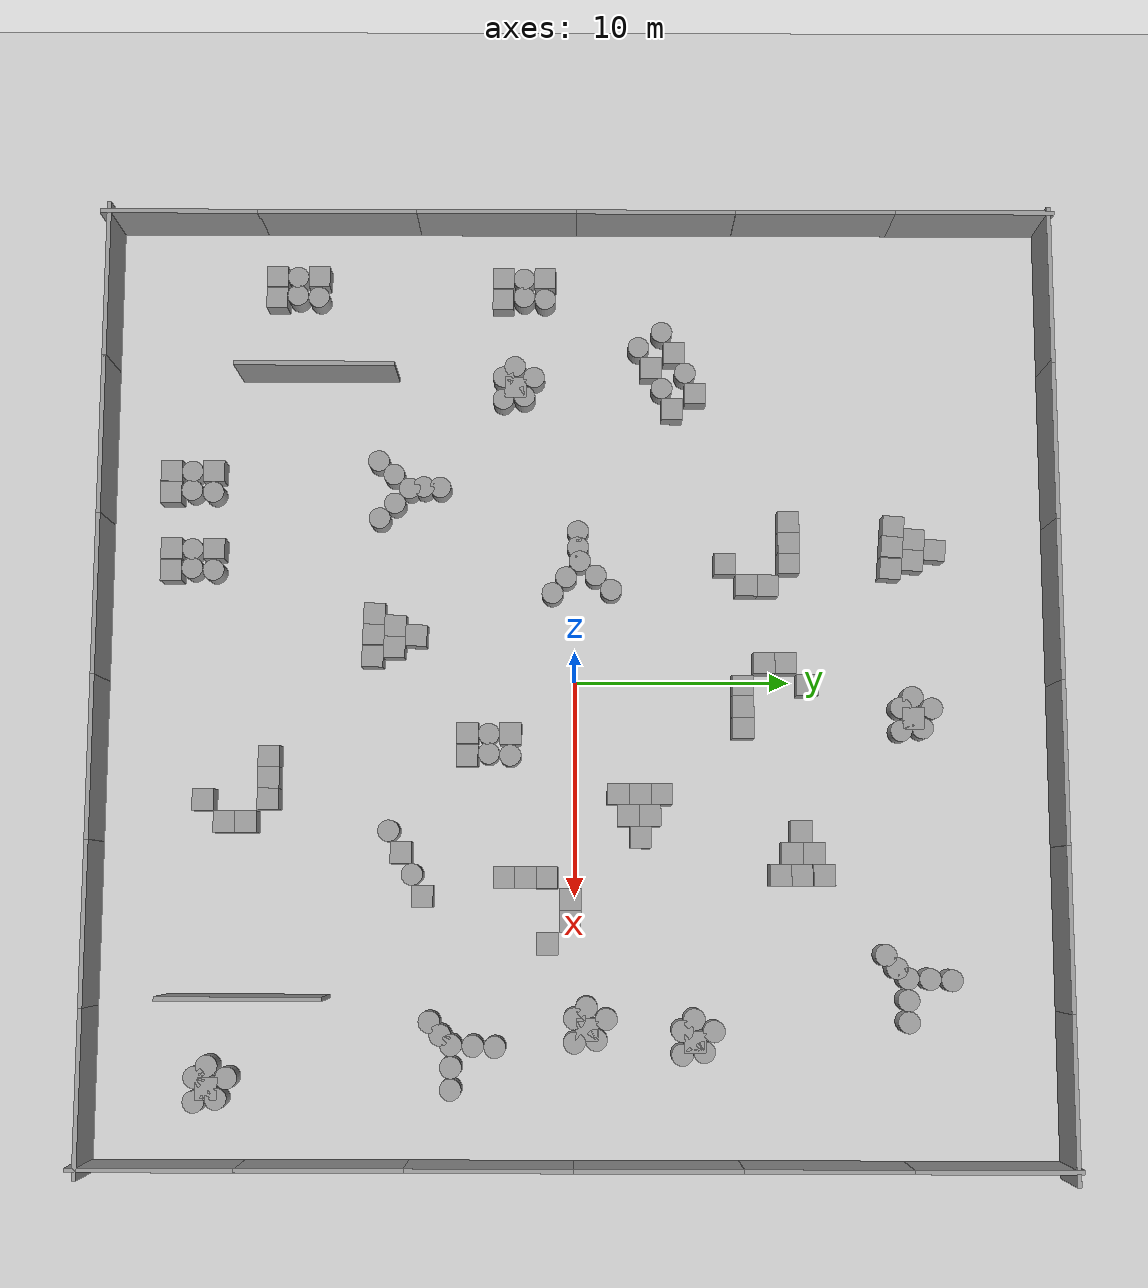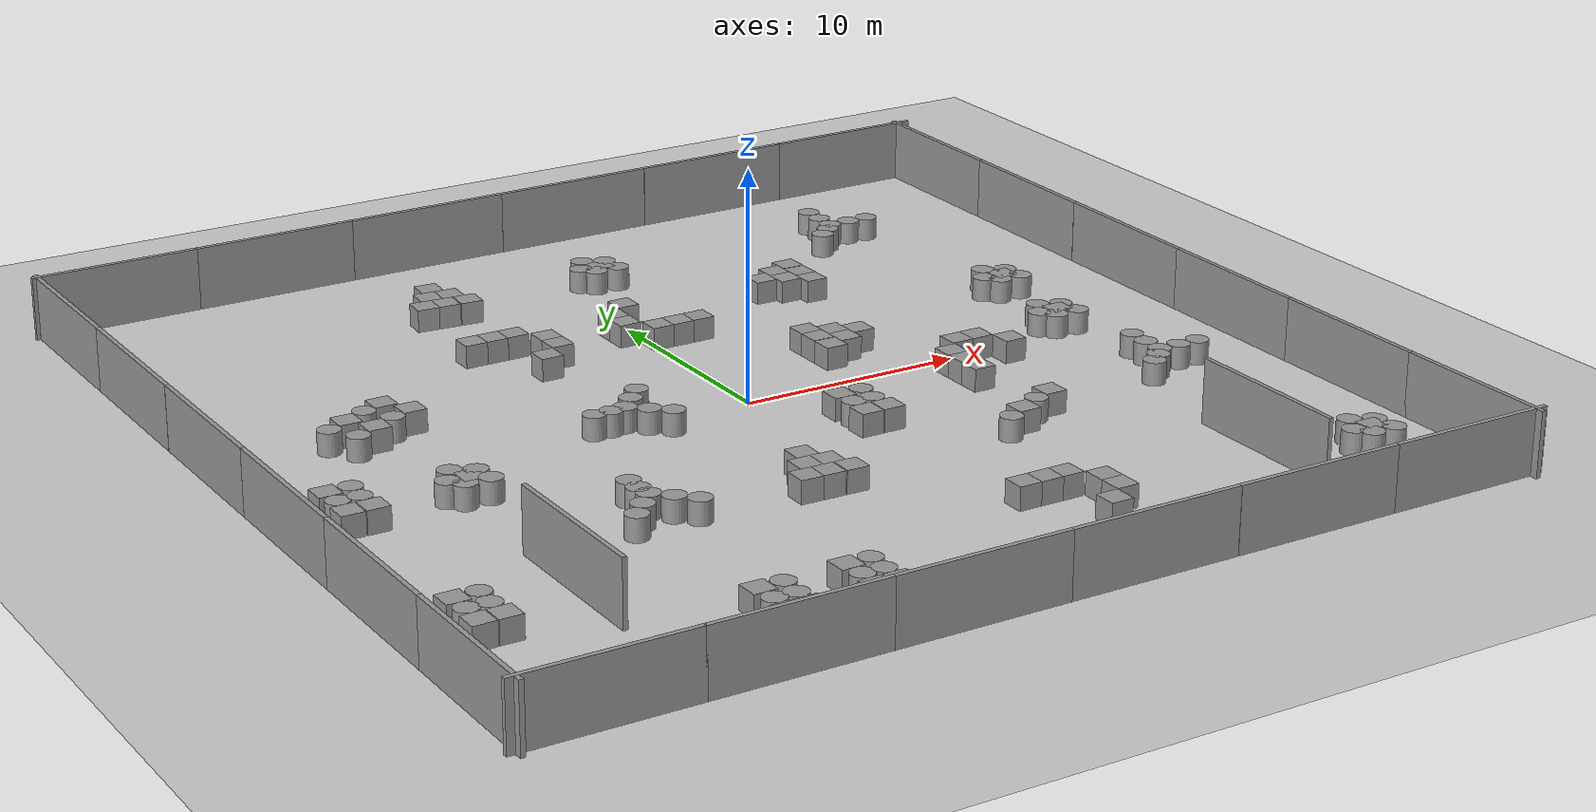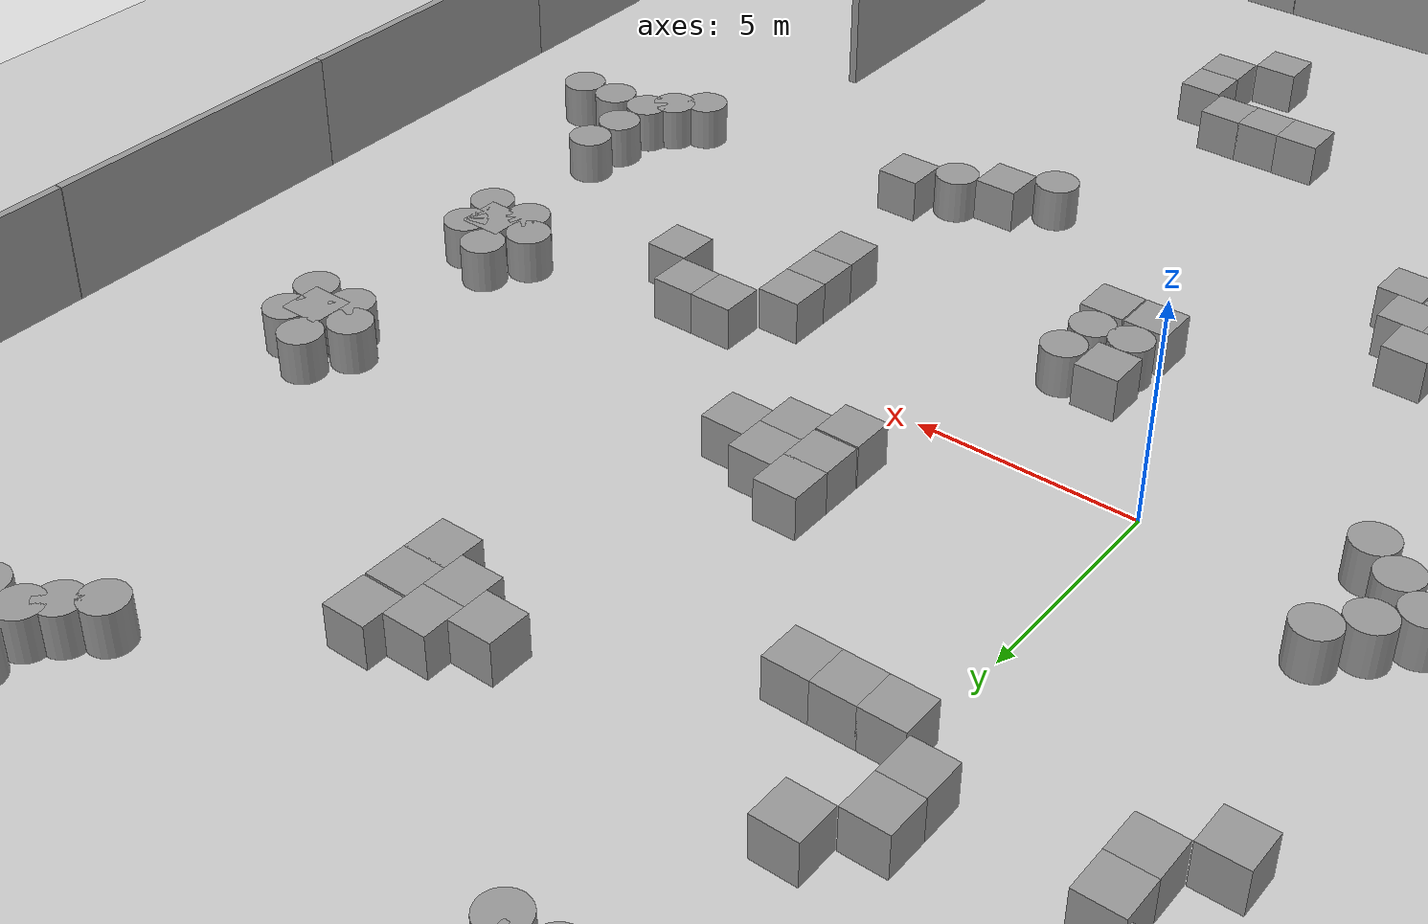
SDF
<sdf version="1.6">
 <world name="default">
  <light name="sun" type="directional">
   <pose>0 0 10 0 -0 0</pose>
   <diffuse>0.8 0.8 0.8 1</diffuse>
   <specular>0.1 0.1 0.1 1</specular>
   <attenuation>
    <range>1000</range>
    <constant>0.9</constant>
    <linear>0.01</linear>
    <quadratic>0.001</quadratic>
   </attenuation>
   <direction>-0.5 0.5 -1</direction>
  </light>
  <model name="ground_plane">
   <static>1</static>
   <link name="link">
    <collision name="collision">
     <geometry><plane><normal>0 0 1</normal><size>100 100</size></plane></geometry>
     <surface><friction><ode><mu>100</mu><mu2>50</mu2></ode></friction></surface>
    </collision>
    <visual name="visual">
     <cast_shadows>0</cast_shadows>
     <geometry><plane><normal>0 0 1</normal><size>100 100</size></plane></geometry>
     <material>
      <script><uri>file://media/materials/scripts/gazebo.material</uri><name>Gazebo/Grey</name></script>
     </material>
    </visual>
   </link>
  </model>
  <gravity>0 0 -9.8</gravity>
  <magnetic_field>6e-06 2.3e-05 -4.2e-05</magnetic_field>
  <atmosphere type="adiabatic"/>
  <physics name="default_physics" default="0" type="ode">
   <max_step_size>0.003</max_step_size>
   <real_time_factor>1</real_time_factor>
   <real_time_update_rate>1000</real_time_update_rate>
  </physics>
  <scene><ambient>0.4 0.4 0.4 1</ambient><background>0.7 0.7 0.7 1</background><shadows>1</shadows></scene>
  <spherical_coordinates>
   <surface_model>EARTH_WGS84</surface_model>
   <latitude_deg>0</latitude_deg>
   <longitude_deg>0</longitude_deg>
   <elevation>0</elevation>
   <heading_deg>0</heading_deg>
  </spherical_coordinates>
  <model name="6walls_0">
   <model name="grey_wall">
    <static>1</static>
    <link name="link">
     <pose>0 0 1.4 0 -0 0</pose>
     <collision name="collision"><geometry><box><size>7.5 0.2 2.8</size></box></geometry></collision>
     <visual name="visual">
      <cast_shadows>0</cast_shadows>
      <geometry><box><size>7.5 0.2 2.8</size></box></geometry>
      <material>
       <script>
        <uri>model://grey_wall/materials/scripts</uri>
        <uri>model://grey_wall/materials/textures</uri>
        <name>vrc/grey_wall</name>
       </script>
      </material>
     </visual>
    </link>
    <pose>-18.6834 0 0 0 -0 0</pose>
   </model>
   <model name="grey_wall_0">
    <static>1</static>
    <link name="link">
     <pose>0 0 1.4 0 -0 0</pose>
     <collision name="collision"><geometry><box><size>7.5 0.2 2.8</size></box></geometry></collision>
     <visual name="visual">
      <cast_shadows>0</cast_shadows>
      <geometry><box><size>7.5 0.2 2.8</size></box></geometry>
      <material>
       <script>
        <uri>model://grey_wall/materials/scripts</uri>
        <uri>model://grey_wall/materials/textures</uri>
        <name>vrc/grey_wall</name>
       </script>
      </material>
     </visual>
    </link>
    <pose>-11.2658 0 0 0 -0 0</pose>
   </model>
   <model name="grey_wall_1">
    <static>1</static>
    <link name="link">
     <pose>0 0 1.4 0 -0 0</pose>
     <collision name="collision"><geometry><box><size>7.5 0.2 2.8</size></box></geometry></collision>
     <visual name="visual">
      <cast_shadows>0</cast_shadows>
      <geometry><box><size>7.5 0.2 2.8</size></box></geometry>
      <material>
       <script>
        <uri>model://grey_wall/materials/scripts</uri>
        <uri>model://grey_wall/materials/textures</uri>
        <name>vrc/grey_wall</name>
       </script>
      </material>
     </visual>
    </link>
    <pose>-3.76669 0 0 0 -0 0</pose>
   </model>
   <model name="grey_wall_2">
    <static>1</static>
    <link name="link">
     <pose>0 0 1.4 0 -0 0</pose>
     <collision name="collision"><geometry><box><size>7.5 0.2 2.8</size></box></geometry></collision>
     <visual name="visual">
      <cast_shadows>0</cast_shadows>
      <geometry><box><size>7.5 0.2 2.8</size></box></geometry>
      <material>
       <script>
        <uri>model://grey_wall/materials/scripts</uri>
        <uri>model://grey_wall/materials/textures</uri>
        <name>vrc/grey_wall</name>
       </script>
      </material>
     </visual>
    </link>
    <pose>3.73421 0 0 0 -0 0</pose>
   </model>
   <model name="grey_wall_3">
    <static>1</static>
    <link name="link">
     <pose>0 0 1.4 0 -0 0</pose>
     <collision name="collision"><geometry><box><size>7.5 0.2 2.8</size></box></geometry></collision>
     <visual name="visual">
      <cast_shadows>0</cast_shadows>
      <geometry><box><size>7.5 0.2 2.8</size></box></geometry>
      <material>
       <script>
        <uri>model://grey_wall/materials/scripts</uri>
        <uri>model://grey_wall/materials/textures</uri>
        <name>vrc/grey_wall</name>
       </script>
      </material>
     </visual>
    </link>
    <pose>11.2475 0 0 0 -0 0</pose>
   </model>
   <model name="grey_wall_4">
    <static>1</static>
    <link name="link">
     <pose>0 0 1.4 0 -0 0</pose>
     <collision name="collision"><geometry><box><size>7.5 0.2 2.8</size></box></geometry></collision>
     <visual name="visual">
      <cast_shadows>0</cast_shadows>
      <geometry><box><size>7.5 0.2 2.8</size></box></geometry>
      <material>
       <script>
        <uri>model://grey_wall/materials/scripts</uri>
        <uri>model://grey_wall/materials/textures</uri>
        <name>vrc/grey_wall</name>
       </script>
      </material>
     </visual>
    </link>
    <pose>18.7342 0 0 0 -0 0</pose>
   </model>
   <static>0</static>
   <pose>0 -22 0 0 -0 0</pose>
  </model>
  <model name="6walls_clone">
   <model name="grey_wall">
    <static>1</static>
    <link name="link">
     <pose>0 0 1.4 0 -0 0</pose>
     <collision name="collision"><geometry><box><size>7.5 0.2 2.8</size></box></geometry></collision>
     <visual name="visual">
      <cast_shadows>0</cast_shadows>
      <geometry><box><size>7.5 0.2 2.8</size></box></geometry>
      <material>
       <script>
        <uri>model://grey_wall/materials/scripts</uri>
        <uri>model://grey_wall/materials/textures</uri>
        <name>vrc/grey_wall</name>
       </script>
      </material>
     </visual>
    </link>
    <pose>-18.6834 0 0 0 -0 0</pose>
   </model>
   <model name="grey_wall_0">
    <static>1</static>
    <link name="link">
     <pose>0 0 1.4 0 -0 0</pose>
     <collision name="collision"><geometry><box><size>7.5 0.2 2.8</size></box></geometry></collision>
     <visual name="visual">
      <cast_shadows>0</cast_shadows>
      <geometry><box><size>7.5 0.2 2.8</size></box></geometry>
      <material>
       <script>
        <uri>model://grey_wall/materials/scripts</uri>
        <uri>model://grey_wall/materials/textures</uri>
        <name>vrc/grey_wall</name>
       </script>
      </material>
     </visual>
    </link>
    <pose>-11.2658 0 0 0 -0 0</pose>
   </model>
   <model name="grey_wall_1">
    <static>1</static>
    <link name="link">
     <pose>0 0 1.4 0 -0 0</pose>
     <collision name="collision"><geometry><box><size>7.5 0.2 2.8</size></box></geometry></collision>
     <visual name="visual">
      <cast_shadows>0</cast_shadows>
      <geometry><box><size>7.5 0.2 2.8</size></box></geometry>
      <material>
       <script>
        <uri>model://grey_wall/materials/scripts</uri>
        <uri>model://grey_wall/materials/textures</uri>
        <name>vrc/grey_wall</name>
       </script>
      </material>
     </visual>
    </link>
    <pose>-3.76669 0 0 0 -0 0</pose>
   </model>
   <model name="grey_wall_2">
    <static>1</static>
    <link name="link">
     <pose>0 0 1.4 0 -0 0</pose>
     <collision name="collision"><geometry><box><size>7.5 0.2 2.8</size></box></geometry></collision>
     <visual name="visual">
      <cast_shadows>0</cast_shadows>
      <geometry><box><size>7.5 0.2 2.8</size></box></geometry>
      <material>
       <script>
        <uri>model://grey_wall/materials/scripts</uri>
        <uri>model://grey_wall/materials/textures</uri>
        <name>vrc/grey_wall</name>
       </script>
      </material>
     </visual>
    </link>
    <pose>3.73421 0 0 0 -0 0</pose>
   </model>
   <model name="grey_wall_3">
    <static>1</static>
    <link name="link">
     <pose>0 0 1.4 0 -0 0</pose>
     <collision name="collision"><geometry><box><size>7.5 0.2 2.8</size></box></geometry></collision>
     <visual name="visual">
      <cast_shadows>0</cast_shadows>
      <geometry><box><size>7.5 0.2 2.8</size></box></geometry>
      <material>
       <script>
        <uri>model://grey_wall/materials/scripts</uri>
        <uri>model://grey_wall/materials/textures</uri>
        <name>vrc/grey_wall</name>
       </script>
      </material>
     </visual>
    </link>
    <pose>11.2475 0 0 0 -0 0</pose>
   </model>
   <model name="grey_wall_4">
    <static>1</static>
    <link name="link">
     <pose>0 0 1.4 0 -0 0</pose>
     <collision name="collision"><geometry><box><size>7.5 0.2 2.8</size></box></geometry></collision>
     <visual name="visual">
      <cast_shadows>0</cast_shadows>
      <geometry><box><size>7.5 0.2 2.8</size></box></geometry>
      <material>
       <script>
        <uri>model://grey_wall/materials/scripts</uri>
        <uri>model://grey_wall/materials/textures</uri>
        <name>vrc/grey_wall</name>
       </script>
      </material>
     </visual>
    </link>
    <pose>18.7342 0 0 0 -0 0</pose>
   </model>
   <static>0</static>
   <pose>21.9999 0 0 0 -0 1.5708</pose>
  </model>
  <model name="6walls_clone_clone">
   <model name="grey_wall">
    <static>1</static>
    <link name="link">
     <pose>0 0 1.4 0 -0 0</pose>
     <collision name="collision"><geometry><box><size>7.5 0.2 2.8</size></box></geometry></collision>
     <visual name="visual">
      <cast_shadows>0</cast_shadows>
      <geometry><box><size>7.5 0.2 2.8</size></box></geometry>
      <material>
       <script>
        <uri>model://grey_wall/materials/scripts</uri>
        <uri>model://grey_wall/materials/textures</uri>
        <name>vrc/grey_wall</name>
       </script>
      </material>
     </visual>
    </link>
    <pose>-18.6834 0 0 0 -0 0</pose>
   </model>
   <model name="grey_wall_0">
    <static>1</static>
    <link name="link">
     <pose>0 0 1.4 0 -0 0</pose>
     <collision name="collision"><geometry><box><size>7.5 0.2 2.8</size></box></geometry></collision>
     <visual name="visual">
      <cast_shadows>0</cast_shadows>
      <geometry><box><size>7.5 0.2 2.8</size></box></geometry>
      <material>
       <script>
        <uri>model://grey_wall/materials/scripts</uri>
        <uri>model://grey_wall/materials/textures</uri>
        <name>vrc/grey_wall</name>
       </script>
      </material>
     </visual>
    </link>
    <pose>-11.2658 0 0 0 -0 0</pose>
   </model>
   <model name="grey_wall_1">
    <static>1</static>
    <link name="link">
     <pose>0 0 1.4 0 -0 0</pose>
     <collision name="collision"><geometry><box><size>7.5 0.2 2.8</size></box></geometry></collision>
     <visual name="visual">
      <cast_shadows>0</cast_shadows>
      <geometry><box><size>7.5 0.2 2.8</size></box></geometry>
      <material>
       <script>
        <uri>model://grey_wall/materials/scripts</uri>
        <uri>model://grey_wall/materials/textures</uri>
        <name>vrc/grey_wall</name>
       </script>
      </material>
     </visual>
    </link>
    <pose>-3.76669 0 0 0 -0 0</pose>
   </model>
   <model name="grey_wall_2">
    <static>1</static>
    <link name="link">
     <pose>0 0 1.4 0 -0 0</pose>
     <collision name="collision"><geometry><box><size>7.5 0.2 2.8</size></box></geometry></collision>
     <visual name="visual">
      <cast_shadows>0</cast_shadows>
      <geometry><box><size>7.5 0.2 2.8</size></box></geometry>
      <material>
       <script>
        <uri>model://grey_wall/materials/scripts</uri>
        <uri>model://grey_wall/materials/textures</uri>
        <name>vrc/grey_wall</name>
       </script>
      </material>
     </visual>
    </link>
    <pose>3.73421 0 0 0 -0 0</pose>
   </model>
   <model name="grey_wall_3">
    <static>1</static>
    <link name="link">
     <pose>0 0 1.4 0 -0 0</pose>
     <collision name="collision"><geometry><box><size>7.5 0.2 2.8</size></box></geometry></collision>
     <visual name="visual">
      <cast_shadows>0</cast_shadows>
      <geometry><box><size>7.5 0.2 2.8</size></box></geometry>
      <material>
       <script>
        <uri>model://grey_wall/materials/scripts</uri>
        <uri>model://grey_wall/materials/textures</uri>
        <name>vrc/grey_wall</name>
       </script>
      </material>
     </visual>
    </link>
    <pose>11.2475 0 0 0 -0 0</pose>
   </model>
   <model name="grey_wall_4">
    <static>1</static>
    <link name="link">
     <pose>0 0 1.4 0 -0 0</pose>
     <collision name="collision"><geometry><box><size>7.5 0.2 2.8</size></box></geometry></collision>
     <visual name="visual">
      <cast_shadows>0</cast_shadows>
      <geometry><box><size>7.5 0.2 2.8</size></box></geometry>
      <material>
       <script>
        <uri>model://grey_wall/materials/scripts</uri>
        <uri>model://grey_wall/materials/textures</uri>
        <name>vrc/grey_wall</name>
       </script>
      </material>
     </visual>
    </link>
    <pose>18.7342 0 0 0 -0 0</pose>
   </model>
   <static>0</static>
   <pose>-22 0 0 0 -0 1.5708</pose>
  </model>
  <model name="machine1">
   <link name="link_0">
    <pose>0.666667 -1.0048 0 0 -0 0</pose>
    <inertial>
     <mass>1</mass>
     <inertia>
      <ixx>0.166667</ixx>
      <ixy>0</ixy>
      <ixz>0</ixz>
      <iyy>0.166667</iyy>
      <iyz>0</iyz>
      <izz>0.166667</izz>
     </inertia>
    </inertial>
    <visual name="visual">
     <geometry><box><size>1 1 1</size></box></geometry>
     <material>
      <lighting>1</lighting>
      <script><uri>file://media/materials/scripts/gazebo.material</uri><name>Gazebo/Grey</name></script>
      <ambient>0.3 0.3 0.3 1</ambient>
      <diffuse>0.7 0.7 0.7 1</diffuse>
      <specular>0.01 0.01 0.01 1</specular>
      <emissive>0 0 0 1</emissive>
     </material>
    </visual>
    <collision name="collision">
     <geometry><box><size>1 1 1</size></box></geometry>
     <surface>
      <friction>
       <ode><mu>1</mu><mu2>1</mu2><fdir1>0 0 0</fdir1><slip1>0</slip1><slip2>0</slip2></ode>
       <torsional>
        <coefficient>1</coefficient>
        <patch_radius>0</patch_radius>
        <surface_radius>0</surface_radius>
        <use_patch_radius>1</use_patch_radius>
        <ode><slip>0</slip></ode>
       </torsional>
      </friction>
      <bounce><restitution_coefficient>0</restitution_coefficient><threshold>1e+06</threshold></bounce>
      <contact>
       <collide_without_contact>0</collide_without_contact>
       <collide_without_contact_bitmask>1</collide_without_contact_bitmask>
       <collide_bitmask>1</collide_bitmask>
       <ode>
        <soft_cfm>0</soft_cfm>
        <soft_erp>0.2</soft_erp>
        <kp>1e+13</kp>
        <kd>1</kd>
        <max_vel>0.01</max_vel>
        <min_depth>0</min_depth>
       </ode>
       <bullet>
        <split_impulse>1</split_impulse>
        <split_impulse_penetration_threshold>-0.01</split_impulse_penetration_threshold>
        <soft_cfm>0</soft_cfm>
        <soft_erp>0.2</soft_erp>
        <kp>1e+13</kp>
        <kd>1</kd>
       </bullet>
      </contact>
     </surface>
    </collision>
   </link>
   <link name="link_1">
    <pose>0.666667 -0.036067 0 0 -0 0</pose>
    <inertial>
     <mass>1</mass>
     <inertia>
      <ixx>0.166667</ixx>
      <ixy>0</ixy>
      <ixz>0</ixz>
      <iyy>0.166667</iyy>
      <iyz>0</iyz>
      <izz>0.166667</izz>
     </inertia>
    </inertial>
    <visual name="visual">
     <geometry><box><size>1 1 1</size></box></geometry>
     <material>
      <lighting>1</lighting>
      <script><uri>file://media/materials/scripts/gazebo.material</uri><name>Gazebo/Grey</name></script>
      <ambient>0.3 0.3 0.3 1</ambient>
      <diffuse>0.7 0.7 0.7 1</diffuse>
      <specular>0.01 0.01 0.01 1</specular>
      <emissive>0 0 0 1</emissive>
     </material>
    </visual>
    <collision name="collision">
     <geometry><box><size>1 1 1</size></box></geometry>
     <surface>
      <friction>
       <ode><mu>1</mu><mu2>1</mu2><fdir1>0 0 0</fdir1><slip1>0</slip1><slip2>0</slip2></ode>
       <torsional>
        <coefficient>1</coefficient>
        <patch_radius>0</patch_radius>
        <surface_radius>0</surface_radius>
        <use_patch_radius>1</use_patch_radius>
        <ode><slip>0</slip></ode>
       </torsional>
      </friction>
      <bounce><restitution_coefficient>0</restitution_coefficient><threshold>1e+06</threshold></bounce>
      <contact>
       <collide_without_contact>0</collide_without_contact>
       <collide_without_contact_bitmask>1</collide_without_contact_bitmask>
       <collide_bitmask>1</collide_bitmask>
       <ode>
        <soft_cfm>0</soft_cfm>
        <soft_erp>0.2</soft_erp>
        <kp>1e+13</kp>
        <kd>1</kd>
        <max_vel>0.01</max_vel>
        <min_depth>0</min_depth>
       </ode>
       <bullet>
        <split_impulse>1</split_impulse>
        <split_impulse_penetration_threshold>-0.01</split_impulse_penetration_threshold>
        <soft_cfm>0</soft_cfm>
        <soft_erp>0.2</soft_erp>
        <kp>1e+13</kp>
        <kd>1</kd>
       </bullet>
      </contact>
     </surface>
    </collision>
   </link>
   <link name="link_2">
    <pose>0.666667 1.00722 0 0 -0 0</pose>
    <inertial>
     <mass>1</mass>
     <inertia>
      <ixx>0.166667</ixx>
      <ixy>0</ixy>
      <ixz>0</ixz>
      <iyy>0.166667</iyy>
      <iyz>0</iyz>
      <izz>0.166667</izz>
     </inertia>
    </inertial>
    <visual name="visual">
     <geometry><box><size>1 1 1</size></box></geometry>
     <material>
      <lighting>1</lighting>
      <script><uri>file://media/materials/scripts/gazebo.material</uri><name>Gazebo/Grey</name></script>
      <ambient>0.3 0.3 0.3 1</ambient>
      <diffuse>0.7 0.7 0.7 1</diffuse>
      <specular>0.01 0.01 0.01 1</specular>
      <emissive>0 0 0 1</emissive>
     </material>
    </visual>
    <collision name="collision">
     <geometry><box><size>1 1 1</size></box></geometry>
     <surface>
      <friction>
       <ode><mu>1</mu><mu2>1</mu2><fdir1>0 0 0</fdir1><slip1>0</slip1><slip2>0</slip2></ode>
       <torsional>
        <coefficient>1</coefficient>
        <patch_radius>0</patch_radius>
        <surface_radius>0</surface_radius>
        <use_patch_radius>1</use_patch_radius>
        <ode><slip>0</slip></ode>
       </torsional>
      </friction>
      <bounce><restitution_coefficient>0</restitution_coefficient><threshold>1e+06</threshold></bounce>
      <contact>
       <collide_without_contact>0</collide_without_contact>
       <collide_without_contact_bitmask>1</collide_without_contact_bitmask>
       <collide_bitmask>1</collide_bitmask>
       <ode>
        <soft_cfm>0</soft_cfm>
        <soft_erp>0.2</soft_erp>
        <kp>1e+13</kp>
        <kd>1</kd>
        <max_vel>0.01</max_vel>
        <min_depth>0</min_depth>
       </ode>
       <bullet>
        <split_impulse>1</split_impulse>
        <split_impulse_penetration_threshold>-0.01</split_impulse_penetration_threshold>
        <soft_cfm>0</soft_cfm>
        <soft_erp>0.2</soft_erp>
        <kp>1e+13</kp>
        <kd>1</kd>
       </bullet>
      </contact>
     </surface>
    </collision>
   </link>
   <link name="link_3">
    <pose>-0.333333 0.53488 0 0 -0 0</pose>
    <inertial>
     <mass>1</mass>
     <inertia>
      <ixx>0.166667</ixx>
      <ixy>0</ixy>
      <ixz>0</ixz>
      <iyy>0.166667</iyy>
      <iyz>0</iyz>
      <izz>0.166667</izz>
     </inertia>
    </inertial>
    <visual name="visual">
     <geometry><box><size>1 1 1</size></box></geometry>
     <material>
      <lighting>1</lighting>
      <script><uri>file://media/materials/scripts/gazebo.material</uri><name>Gazebo/Grey</name></script>
      <ambient>0.3 0.3 0.3 1</ambient>
      <diffuse>0.7 0.7 0.7 1</diffuse>
      <specular>0.01 0.01 0.01 1</specular>
      <emissive>0 0 0 1</emissive>
     </material>
    </visual>
    <collision name="collision">
     <geometry><box><size>1 1 1</size></box></geometry>
     <surface>
      <friction>
       <ode><mu>1</mu><mu2>1</mu2><fdir1>0 0 0</fdir1><slip1>0</slip1><slip2>0</slip2></ode>
       <torsional>
        <coefficient>1</coefficient>
        <patch_radius>0</patch_radius>
        <surface_radius>0</surface_radius>
        <use_patch_radius>1</use_patch_radius>
        <ode><slip>0</slip></ode>
       </torsional>
      </friction>
      <bounce><restitution_coefficient>0</restitution_coefficient><threshold>1e+06</threshold></bounce>
      <contact>
       <collide_without_contact>0</collide_without_contact>
       <collide_without_contact_bitmask>1</collide_without_contact_bitmask>
       <collide_bitmask>1</collide_bitmask>
       <ode>
        <soft_cfm>0</soft_cfm>
        <soft_erp>0.2</soft_erp>
        <kp>1e+13</kp>
        <kd>1</kd>
        <max_vel>0.01</max_vel>
        <min_depth>0</min_depth>
       </ode>
       <bullet>
        <split_impulse>1</split_impulse>
        <split_impulse_penetration_threshold>-0.01</split_impulse_penetration_threshold>
        <soft_cfm>0</soft_cfm>
        <soft_erp>0.2</soft_erp>
        <kp>1e+13</kp>
        <kd>1</kd>
       </bullet>
      </contact>
     </surface>
    </collision>
   </link>
   <link name="link_4">
    <pose>-0.333333 -0.46512 0 0 -0 0</pose>
    <inertial>
     <mass>1</mass>
     <inertia>
      <ixx>0.166667</ixx>
      <ixy>0</ixy>
      <ixz>0</ixz>
      <iyy>0.166667</iyy>
      <iyz>0</iyz>
      <izz>0.166667</izz>
     </inertia>
    </inertial>
    <visual name="visual">
     <geometry><box><size>1 1 1</size></box></geometry>
     <material>
      <lighting>1</lighting>
      <script><uri>file://media/materials/scripts/gazebo.material</uri><name>Gazebo/Grey</name></script>
      <ambient>0.3 0.3 0.3 1</ambient>
      <diffuse>0.7 0.7 0.7 1</diffuse>
      <specular>0.01 0.01 0.01 1</specular>
      <emissive>0 0 0 1</emissive>
     </material>
    </visual>
    <collision name="collision">
     <geometry><box><size>1 1 1</size></box></geometry>
     <surface>
      <friction>
       <ode><mu>1</mu><mu2>1</mu2><fdir1>0 0 0</fdir1><slip1>0</slip1><slip2>0</slip2></ode>
       <torsional>
        <coefficient>1</coefficient>
        <patch_radius>0</patch_radius>
        <surface_radius>0</surface_radius>
        <use_patch_radius>1</use_patch_radius>
        <ode><slip>0</slip></ode>
       </torsional>
      </friction>
      <bounce><restitution_coefficient>0</restitution_coefficient><threshold>1e+06</threshold></bounce>
      <contact>
       <collide_without_contact>0</collide_without_contact>
       <collide_without_contact_bitmask>1</collide_without_contact_bitmask>
       <collide_bitmask>1</collide_bitmask>
       <ode>
        <soft_cfm>0</soft_cfm>
        <soft_erp>0.2</soft_erp>
        <kp>1e+13</kp>
        <kd>1</kd>
        <max_vel>0.01</max_vel>
        <min_depth>0</min_depth>
       </ode>
       <bullet>
        <split_impulse>1</split_impulse>
        <split_impulse_penetration_threshold>-0.01</split_impulse_penetration_threshold>
        <soft_cfm>0</soft_cfm>
        <soft_erp>0.2</soft_erp>
        <kp>1e+13</kp>
        <kd>1</kd>
       </bullet>
      </contact>
     </surface>
    </collision>
   </link>
   <link name="link_5">
    <pose>-1.33333 -0.036128 0 0 -0 0</pose>
    <inertial>
     <mass>1</mass>
     <inertia>
      <ixx>0.166667</ixx>
      <ixy>0</ixy>
      <ixz>0</ixz>
      <iyy>0.166667</iyy>
      <iyz>0</iyz>
      <izz>0.166667</izz>
     </inertia>
    </inertial>
    <visual name="visual">
     <geometry><box><size>1 1 1</size></box></geometry>
     <material>
      <lighting>1</lighting>
      <script><uri>file://media/materials/scripts/gazebo.material</uri><name>Gazebo/Grey</name></script>
      <ambient>0.3 0.3 0.3 1</ambient>
      <diffuse>0.7 0.7 0.7 1</diffuse>
      <specular>0.01 0.01 0.01 1</specular>
      <emissive>0 0 0 1</emissive>
     </material>
    </visual>
    <collision name="collision">
     <geometry><box><size>1 1 1</size></box></geometry>
     <surface>
      <friction>
       <ode><mu>1</mu><mu2>1</mu2><fdir1>0 0 0</fdir1><slip1>0</slip1><slip2>0</slip2></ode>
       <torsional>
        <coefficient>1</coefficient>
        <patch_radius>0</patch_radius>
        <surface_radius>0</surface_radius>
        <use_patch_radius>1</use_patch_radius>
        <ode><slip>0</slip></ode>
       </torsional>
      </friction>
      <bounce><restitution_coefficient>0</restitution_coefficient><threshold>1e+06</threshold></bounce>
      <contact>
       <collide_without_contact>0</collide_without_contact>
       <collide_without_contact_bitmask>1</collide_without_contact_bitmask>
       <collide_bitmask>1</collide_bitmask>
       <ode>
        <soft_cfm>0</soft_cfm>
        <soft_erp>0.2</soft_erp>
        <kp>1e+13</kp>
        <kd>1</kd>
        <max_vel>0.01</max_vel>
        <min_depth>0</min_depth>
       </ode>
       <bullet>
        <split_impulse>1</split_impulse>
        <split_impulse_penetration_threshold>-0.01</split_impulse_penetration_threshold>
        <soft_cfm>0</soft_cfm>
        <soft_erp>0.2</soft_erp>
        <kp>1e+13</kp>
        <kd>1</kd>
       </bullet>
      </contact>
     </surface>
    </collision>
   </link>
   <static>0</static>
   <pose>8.33333 10.4651 0.5 0 -0 0</pose>
  </model>
  <model name="machine2">
   <link name="link_6">
    <pose>0.153167 -0.028269 0 0 -0 0</pose>
    <inertial>
     <mass>1</mass>
     <inertia>
      <ixx>0.166667</ixx>
      <ixy>0</ixy>
      <ixz>0</ixz>
      <iyy>0.166667</iyy>
      <iyz>0</iyz>
      <izz>0.166667</izz>
     </inertia>
    </inertial>
    <visual name="visual">
     <geometry><box><size>1 1 1</size></box></geometry>
     <material>
      <lighting>1</lighting>
      <script><uri>file://media/materials/scripts/gazebo.material</uri><name>Gazebo/Grey</name></script>
      <ambient>0.3 0.3 0.3 1</ambient>
      <diffuse>0.7 0.7 0.7 1</diffuse>
      <specular>0.01 0.01 0.01 1</specular>
      <emissive>0 0 0 1</emissive>
     </material>
    </visual>
    <collision name="collision">
     <geometry><box><size>1 1 1</size></box></geometry>
     <surface>
      <friction>
       <ode><mu>1</mu><mu2>1</mu2><fdir1>0 0 0</fdir1><slip1>0</slip1><slip2>0</slip2></ode>
       <torsional>
        <coefficient>1</coefficient>
        <patch_radius>0</patch_radius>
        <surface_radius>0</surface_radius>
        <use_patch_radius>1</use_patch_radius>
        <ode><slip>0</slip></ode>
       </torsional>
      </friction>
      <bounce><restitution_coefficient>0</restitution_coefficient><threshold>1e+06</threshold></bounce>
      <contact>
       <collide_without_contact>0</collide_without_contact>
       <collide_without_contact_bitmask>1</collide_without_contact_bitmask>
       <collide_bitmask>1</collide_bitmask>
       <ode>
        <soft_cfm>0</soft_cfm>
        <soft_erp>0.2</soft_erp>
        <kp>1e+13</kp>
        <kd>1</kd>
        <max_vel>0.01</max_vel>
        <min_depth>0</min_depth>
       </ode>
       <bullet>
        <split_impulse>1</split_impulse>
        <split_impulse_penetration_threshold>-0.01</split_impulse_penetration_threshold>
        <soft_cfm>0</soft_cfm>
        <soft_erp>0.2</soft_erp>
        <kp>1e+13</kp>
        <kd>1</kd>
       </bullet>
      </contact>
     </surface>
    </collision>
   </link>
   <link name="link_10">
    <pose>0.61205 0.404825 0 0 -0 0</pose>
    <inertial>
     <mass>1</mass>
     <inertia><ixx>0.145833</ixx><ixy>0</ixy><ixz>0</ixz><iyy>0.145833</iyy><iyz>0</iyz><izz>0.125</izz></inertia>
    </inertial>
    <visual name="visual">
     <geometry><cylinder><radius>0.5</radius><length>1</length></cylinder></geometry>
     <material>
      <lighting>1</lighting>
      <script><uri>file://media/materials/scripts/gazebo.material</uri><name>Gazebo/Grey</name></script>
      <ambient>0.3 0.3 0.3 1</ambient>
      <diffuse>0.7 0.7 0.7 1</diffuse>
      <specular>0.01 0.01 0.01 1</specular>
      <emissive>0 0 0 1</emissive>
     </material>
    </visual>
    <collision name="collision">
     <geometry><cylinder><radius>0.5</radius><length>1</length></cylinder></geometry>
     <surface>
      <friction>
       <ode><mu>1</mu><mu2>1</mu2><fdir1>0 0 0</fdir1><slip1>0</slip1><slip2>0</slip2></ode>
       <torsional>
        <coefficient>1</coefficient>
        <patch_radius>0</patch_radius>
        <surface_radius>0</surface_radius>
        <use_patch_radius>1</use_patch_radius>
        <ode><slip>0</slip></ode>
       </torsional>
      </friction>
      <bounce><restitution_coefficient>0</restitution_coefficient><threshold>1e+06</threshold></bounce>
      <contact>
       <collide_without_contact>0</collide_without_contact>
       <collide_without_contact_bitmask>1</collide_without_contact_bitmask>
       <collide_bitmask>1</collide_bitmask>
       <ode>
        <soft_cfm>0</soft_cfm>
        <soft_erp>0.2</soft_erp>
        <kp>1e+13</kp>
        <kd>1</kd>
        <max_vel>0.01</max_vel>
        <min_depth>0</min_depth>
       </ode>
       <bullet>
        <split_impulse>1</split_impulse>
        <split_impulse_penetration_threshold>-0.01</split_impulse_penetration_threshold>
        <soft_cfm>0</soft_cfm>
        <soft_erp>0.2</soft_erp>
        <kp>1e+13</kp>
        <kd>1</kd>
       </bullet>
      </contact>
     </surface>
    </collision>
   </link>
   <link name="link_11">
    <pose>0.739497 -0.595175 0 0 -0 0</pose>
    <inertial>
     <mass>1</mass>
     <inertia><ixx>0.145833</ixx><ixy>0</ixy><ixz>0</ixz><iyy>0.145833</iyy><iyz>0</iyz><izz>0.125</izz></inertia>
    </inertial>
    <visual name="visual">
     <geometry><cylinder><radius>0.5</radius><length>1</length></cylinder></geometry>
     <material>
      <lighting>1</lighting>
      <script><uri>file://media/materials/scripts/gazebo.material</uri><name>Gazebo/Grey</name></script>
      <ambient>0.3 0.3 0.3 1</ambient>
      <diffuse>0.7 0.7 0.7 1</diffuse>
      <specular>0.01 0.01 0.01 1</specular>
      <emissive>0 0 0 1</emissive>
     </material>
    </visual>
    <collision name="collision">
     <geometry><cylinder><radius>0.5</radius><length>1</length></cylinder></geometry>
     <surface>
      <friction>
       <ode><mu>1</mu><mu2>1</mu2><fdir1>0 0 0</fdir1><slip1>0</slip1><slip2>0</slip2></ode>
       <torsional>
        <coefficient>1</coefficient>
        <patch_radius>0</patch_radius>
        <surface_radius>0</surface_radius>
        <use_patch_radius>1</use_patch_radius>
        <ode><slip>0</slip></ode>
       </torsional>
      </friction>
      <bounce><restitution_coefficient>0</restitution_coefficient><threshold>1e+06</threshold></bounce>
      <contact>
       <collide_without_contact>0</collide_without_contact>
       <collide_without_contact_bitmask>1</collide_without_contact_bitmask>
       <collide_bitmask>1</collide_bitmask>
       <ode>
        <soft_cfm>0</soft_cfm>
        <soft_erp>0.2</soft_erp>
        <kp>1e+13</kp>
        <kd>1</kd>
        <max_vel>0.01</max_vel>
        <min_depth>0</min_depth>
       </ode>
       <bullet>
        <split_impulse>1</split_impulse>
        <split_impulse_penetration_threshold>-0.01</split_impulse_penetration_threshold>
        <soft_cfm>0</soft_cfm>
        <soft_erp>0.2</soft_erp>
        <kp>1e+13</kp>
        <kd>1</kd>
       </bullet>
      </contact>
     </surface>
    </collision>
   </link>
   <link name="link_12">
    <pose>-0.316153 0.858024 0 0 -0 0</pose>
    <inertial>
     <mass>1</mass>
     <inertia><ixx>0.145833</ixx><ixy>0</ixy><ixz>0</ixz><iyy>0.145833</iyy><iyz>0</iyz><izz>0.125</izz></inertia>
    </inertial>
    <visual name="visual">
     <geometry><cylinder><radius>0.5</radius><length>1</length></cylinder></geometry>
     <material>
      <lighting>1</lighting>
      <script><uri>file://media/materials/scripts/gazebo.material</uri><name>Gazebo/Grey</name></script>
      <ambient>0.3 0.3 0.3 1</ambient>
      <diffuse>0.7 0.7 0.7 1</diffuse>
      <specular>0.01 0.01 0.01 1</specular>
      <emissive>0 0 0 1</emissive>
     </material>
    </visual>
    <collision name="collision">
     <geometry><cylinder><radius>0.5</radius><length>1</length></cylinder></geometry>
     <surface>
      <friction>
       <ode><mu>1</mu><mu2>1</mu2><fdir1>0 0 0</fdir1><slip1>0</slip1><slip2>0</slip2></ode>
       <torsional>
        <coefficient>1</coefficient>
        <patch_radius>0</patch_radius>
        <surface_radius>0</surface_radius>
        <use_patch_radius>1</use_patch_radius>
        <ode><slip>0</slip></ode>
       </torsional>
      </friction>
      <bounce><restitution_coefficient>0</restitution_coefficient><threshold>1e+06</threshold></bounce>
      <contact>
       <collide_without_contact>0</collide_without_contact>
       <collide_without_contact_bitmask>1</collide_without_contact_bitmask>
       <collide_bitmask>1</collide_bitmask>
       <ode>
        <soft_cfm>0</soft_cfm>
        <soft_erp>0.2</soft_erp>
        <kp>1e+13</kp>
        <kd>1</kd>
        <max_vel>0.01</max_vel>
        <min_depth>0</min_depth>
       </ode>
       <bullet>
        <split_impulse>1</split_impulse>
        <split_impulse_penetration_threshold>-0.01</split_impulse_penetration_threshold>
        <soft_cfm>0</soft_cfm>
        <soft_erp>0.2</soft_erp>
        <kp>1e+13</kp>
        <kd>1</kd>
       </bullet>
      </contact>
     </surface>
    </collision>
   </link>
   <link name="link_8">
    <pose>-0.846833 -0.044231 0 0 -0 0</pose>
    <inertial>
     <mass>1</mass>
     <inertia><ixx>0.145833</ixx><ixy>0</ixy><ixz>0</ixz><iyy>0.145833</iyy><iyz>0</iyz><izz>0.125</izz></inertia>
    </inertial>
    <visual name="visual">
     <geometry><cylinder><radius>0.5</radius><length>1</length></cylinder></geometry>
     <material>
      <lighting>1</lighting>
      <script><uri>file://media/materials/scripts/gazebo.material</uri><name>Gazebo/Grey</name></script>
      <ambient>0.3 0.3 0.3 1</ambient>
      <diffuse>0.7 0.7 0.7 1</diffuse>
      <specular>0.01 0.01 0.01 1</specular>
      <emissive>0 0 0 1</emissive>
     </material>
    </visual>
    <collision name="collision">
     <geometry><cylinder><radius>0.5</radius><length>1</length></cylinder></geometry>
     <surface>
      <friction>
       <ode><mu>1</mu><mu2>1</mu2><fdir1>0 0 0</fdir1><slip1>0</slip1><slip2>0</slip2></ode>
       <torsional>
        <coefficient>1</coefficient>
        <patch_radius>0</patch_radius>
        <surface_radius>0</surface_radius>
        <use_patch_radius>1</use_patch_radius>
        <ode><slip>0</slip></ode>
       </torsional>
      </friction>
      <bounce><restitution_coefficient>0</restitution_coefficient><threshold>1e+06</threshold></bounce>
      <contact>
       <collide_without_contact>0</collide_without_contact>
       <collide_without_contact_bitmask>1</collide_without_contact_bitmask>
       <collide_bitmask>1</collide_bitmask>
       <ode>
        <soft_cfm>0</soft_cfm>
        <soft_erp>0.2</soft_erp>
        <kp>1e+13</kp>
        <kd>1</kd>
        <max_vel>0.01</max_vel>
        <min_depth>0</min_depth>
       </ode>
       <bullet>
        <split_impulse>1</split_impulse>
        <split_impulse_penetration_threshold>-0.01</split_impulse_penetration_threshold>
        <soft_cfm>0</soft_cfm>
        <soft_erp>0.2</soft_erp>
        <kp>1e+13</kp>
        <kd>1</kd>
       </bullet>
      </contact>
     </surface>
    </collision>
   </link>
   <link name="link_9">
    <pose>-0.34172 -0.595175 0 0 -0 0</pose>
    <inertial>
     <mass>1</mass>
     <inertia><ixx>0.145833</ixx><ixy>0</ixy><ixz>0</ixz><iyy>0.145833</iyy><iyz>0</iyz><izz>0.125</izz></inertia>
    </inertial>
    <visual name="visual">
     <geometry><cylinder><radius>0.5</radius><length>1</length></cylinder></geometry>
     <material>
      <lighting>1</lighting>
      <script><uri>file://media/materials/scripts/gazebo.material</uri><name>Gazebo/Grey</name></script>
      <ambient>0.3 0.3 0.3 1</ambient>
      <diffuse>0.7 0.7 0.7 1</diffuse>
      <specular>0.01 0.01 0.01 1</specular>
      <emissive>0 0 0 1</emissive>
     </material>
    </visual>
    <collision name="collision">
     <geometry><cylinder><radius>0.5</radius><length>1</length></cylinder></geometry>
     <surface>
      <friction>
       <ode><mu>1</mu><mu2>1</mu2><fdir1>0 0 0</fdir1><slip1>0</slip1><slip2>0</slip2></ode>
       <torsional>
        <coefficient>1</coefficient>
        <patch_radius>0</patch_radius>
        <surface_radius>0</surface_radius>
        <use_patch_radius>1</use_patch_radius>
        <ode><slip>0</slip></ode>
       </torsional>
      </friction>
      <bounce><restitution_coefficient>0</restitution_coefficient><threshold>1e+06</threshold></bounce>
      <contact>
       <collide_without_contact>0</collide_without_contact>
       <collide_without_contact_bitmask>1</collide_without_contact_bitmask>
       <collide_bitmask>1</collide_bitmask>
       <ode>
        <soft_cfm>0</soft_cfm>
        <soft_erp>0.2</soft_erp>
        <kp>1e+13</kp>
        <kd>1</kd>
        <max_vel>0.01</max_vel>
        <min_depth>0</min_depth>
       </ode>
       <bullet>
        <split_impulse>1</split_impulse>
        <split_impulse_penetration_threshold>-0.01</split_impulse_penetration_threshold>
        <soft_cfm>0</soft_cfm>
        <soft_erp>0.2</soft_erp>
        <kp>1e+13</kp>
        <kd>1</kd>
       </bullet>
      </contact>
     </surface>
    </collision>
   </link>
   <static>0</static>
   <pose>15.8468 0.595175 0.5 0 -0 0</pose>
  </model>
  <model name="grey_wall_5_clone">
   <static>1</static>
   <link name="link">
    <pose>0 0 1.4 0 -0 0</pose>
    <collision name="collision"><geometry><box><size>7.5 0.2 2.8</size></box></geometry></collision>
    <visual name="visual">
     <cast_shadows>0</cast_shadows>
     <geometry><box><size>7.5 0.2 2.8</size></box></geometry>
     <material>
      <script>
       <uri>model://grey_wall/materials/scripts</uri>
       <uri>model://grey_wall/materials/textures</uri>
       <name>vrc/grey_wall</name>
      </script>
     </material>
    </visual>
   </link>
   <pose>14.5686 -15.0042 0 0 -0 1.5708</pose>
  </model>
  <model name="grey_wall_5_clone_0">
   <static>1</static>
   <link name="link">
    <pose>0 0 1.4 0 -0 0</pose>
    <collision name="collision"><geometry><box><size>7.5 0.2 2.8</size></box></geometry></collision>
    <visual name="visual">
     <cast_shadows>0</cast_shadows>
     <geometry><box><size>7.5 0.2 2.8</size></box></geometry>
     <material>
      <script>
       <uri>model://grey_wall/materials/scripts</uri>
       <uri>model://grey_wall/materials/textures</uri>
       <name>vrc/grey_wall</name>
      </script>
     </material>
    </visual>
   </link>
   <pose>-14.6343 -12.2013 0 0 -0 1.5708</pose>
  </model>
  <model name="machine3">
   <link name="link_13">
    <pose>-0.503159 1 0 0 -0 0</pose>
    <inertial>
     <mass>1</mass>
     <inertia>
      <ixx>0.166667</ixx>
      <ixy>0</ixy>
      <ixz>0</ixz>
      <iyy>0.166667</iyy>
      <iyz>0</iyz>
      <izz>0.166667</izz>
     </inertia>
    </inertial>
    <visual name="visual">
     <geometry><box><size>1 1 1</size></box></geometry>
     <material>
      <lighting>1</lighting>
      <script><uri>file://media/materials/scripts/gazebo.material</uri><name>Gazebo/Grey</name></script>
      <ambient>0.3 0.3 0.3 1</ambient>
      <diffuse>0.7 0.7 0.7 1</diffuse>
      <specular>0.01 0.01 0.01 1</specular>
      <emissive>0 0 0 1</emissive>
     </material>
    </visual>
    <collision name="collision">
     <geometry><box><size>1 1 1</size></box></geometry>
     <surface>
      <friction>
       <ode><mu>1</mu><mu2>1</mu2><fdir1>0 0 0</fdir1><slip1>0</slip1><slip2>0</slip2></ode>
       <torsional>
        <coefficient>1</coefficient>
        <patch_radius>0</patch_radius>
        <surface_radius>0</surface_radius>
        <use_patch_radius>1</use_patch_radius>
        <ode><slip>0</slip></ode>
       </torsional>
      </friction>
      <bounce><restitution_coefficient>0</restitution_coefficient><threshold>1e+06</threshold></bounce>
      <contact>
       <collide_without_contact>0</collide_without_contact>
       <collide_without_contact_bitmask>1</collide_without_contact_bitmask>
       <collide_bitmask>1</collide_bitmask>
       <ode>
        <soft_cfm>0</soft_cfm>
        <soft_erp>0.2</soft_erp>
        <kp>1e+13</kp>
        <kd>1</kd>
        <max_vel>0.01</max_vel>
        <min_depth>0</min_depth>
       </ode>
       <bullet>
        <split_impulse>1</split_impulse>
        <split_impulse_penetration_threshold>-0.01</split_impulse_penetration_threshold>
        <soft_cfm>0</soft_cfm>
        <soft_erp>0.2</soft_erp>
        <kp>1e+13</kp>
        <kd>1</kd>
       </bullet>
      </contact>
     </surface>
    </collision>
   </link>
   <link name="link_14">
    <pose>0.524915 1 0 0 -0 0</pose>
    <inertial>
     <mass>1</mass>
     <inertia><ixx>0.145833</ixx><ixy>0</ixy><ixz>0</ixz><iyy>0.145833</iyy><iyz>0</iyz><izz>0.125</izz></inertia>
    </inertial>
    <visual name="visual">
     <geometry><cylinder><radius>0.5</radius><length>1</length></cylinder></geometry>
     <material>
      <lighting>1</lighting>
      <script><uri>file://media/materials/scripts/gazebo.material</uri><name>Gazebo/Grey</name></script>
      <ambient>0.3 0.3 0.3 1</ambient>
      <diffuse>0.7 0.7 0.7 1</diffuse>
      <specular>0.01 0.01 0.01 1</specular>
      <emissive>0 0 0 1</emissive>
     </material>
    </visual>
    <collision name="collision">
     <geometry><cylinder><radius>0.5</radius><length>1</length></cylinder></geometry>
     <surface>
      <friction>
       <ode><mu>1</mu><mu2>1</mu2><fdir1>0 0 0</fdir1><slip1>0</slip1><slip2>0</slip2></ode>
       <torsional>
        <coefficient>1</coefficient>
        <patch_radius>0</patch_radius>
        <surface_radius>0</surface_radius>
        <use_patch_radius>1</use_patch_radius>
        <ode><slip>0</slip></ode>
       </torsional>
      </friction>
      <bounce><restitution_coefficient>0</restitution_coefficient><threshold>1e+06</threshold></bounce>
      <contact>
       <collide_without_contact>0</collide_without_contact>
       <collide_without_contact_bitmask>1</collide_without_contact_bitmask>
       <collide_bitmask>1</collide_bitmask>
       <ode>
        <soft_cfm>0</soft_cfm>
        <soft_erp>0.2</soft_erp>
        <kp>1e+13</kp>
        <kd>1</kd>
        <max_vel>0.01</max_vel>
        <min_depth>0</min_depth>
       </ode>
       <bullet>
        <split_impulse>1</split_impulse>
        <split_impulse_penetration_threshold>-0.01</split_impulse_penetration_threshold>
        <soft_cfm>0</soft_cfm>
        <soft_erp>0.2</soft_erp>
        <kp>1e+13</kp>
        <kd>1</kd>
       </bullet>
      </contact>
     </surface>
    </collision>
   </link>
   <link name="link_15">
    <pose>0.434688 0 0 0 -0 0</pose>
    <inertial>
     <mass>1</mass>
     <inertia><ixx>0.145833</ixx><ixy>0</ixy><ixz>0</ixz><iyy>0.145833</iyy><iyz>0</iyz><izz>0.125</izz></inertia>
    </inertial>
    <visual name="visual">
     <geometry><cylinder><radius>0.5</radius><length>1</length></cylinder></geometry>
     <material>
      <lighting>1</lighting>
      <script><uri>file://media/materials/scripts/gazebo.material</uri><name>Gazebo/Grey</name></script>
      <ambient>0.3 0.3 0.3 1</ambient>
      <diffuse>0.7 0.7 0.7 1</diffuse>
      <specular>0.01 0.01 0.01 1</specular>
      <emissive>0 0 0 1</emissive>
     </material>
    </visual>
    <collision name="collision">
     <geometry><cylinder><radius>0.5</radius><length>1</length></cylinder></geometry>
     <surface>
      <friction>
       <ode><mu>1</mu><mu2>1</mu2><fdir1>0 0 0</fdir1><slip1>0</slip1><slip2>0</slip2></ode>
       <torsional>
        <coefficient>1</coefficient>
        <patch_radius>0</patch_radius>
        <surface_radius>0</surface_radius>
        <use_patch_radius>1</use_patch_radius>
        <ode><slip>0</slip></ode>
       </torsional>
      </friction>
      <bounce><restitution_coefficient>0</restitution_coefficient><threshold>1e+06</threshold></bounce>
      <contact>
       <collide_without_contact>0</collide_without_contact>
       <collide_without_contact_bitmask>1</collide_without_contact_bitmask>
       <collide_bitmask>1</collide_bitmask>
       <ode>
        <soft_cfm>0</soft_cfm>
        <soft_erp>0.2</soft_erp>
        <kp>1e+13</kp>
        <kd>1</kd>
        <max_vel>0.01</max_vel>
        <min_depth>0</min_depth>
       </ode>
       <bullet>
        <split_impulse>1</split_impulse>
        <split_impulse_penetration_threshold>-0.01</split_impulse_penetration_threshold>
        <soft_cfm>0</soft_cfm>
        <soft_erp>0.2</soft_erp>
        <kp>1e+13</kp>
        <kd>1</kd>
       </bullet>
      </contact>
     </surface>
    </collision>
   </link>
   <link name="link_16">
    <pose>-0.471074 0 0 0 -0 0</pose>
    <inertial>
     <mass>1</mass>
     <inertia><ixx>0.145833</ixx><ixy>0</ixy><ixz>0</ixz><iyy>0.145833</iyy><iyz>0</iyz><izz>0.125</izz></inertia>
    </inertial>
    <visual name="visual">
     <geometry><cylinder><radius>0.5</radius><length>1</length></cylinder></geometry>
     <material>
      <lighting>1</lighting>
      <script><uri>file://media/materials/scripts/gazebo.material</uri><name>Gazebo/Grey</name></script>
      <ambient>0.3 0.3 0.3 1</ambient>
      <diffuse>0.7 0.7 0.7 1</diffuse>
      <specular>0.01 0.01 0.01 1</specular>
      <emissive>0 0 0 1</emissive>
     </material>
    </visual>
    <collision name="collision">
     <geometry><cylinder><radius>0.5</radius><length>1</length></cylinder></geometry>
     <surface>
      <friction>
       <ode><mu>1</mu><mu2>1</mu2><fdir1>0 0 0</fdir1><slip1>0</slip1><slip2>0</slip2></ode>
       <torsional>
        <coefficient>1</coefficient>
        <patch_radius>0</patch_radius>
        <surface_radius>0</surface_radius>
        <use_patch_radius>1</use_patch_radius>
        <ode><slip>0</slip></ode>
       </torsional>
      </friction>
      <bounce><restitution_coefficient>0</restitution_coefficient><threshold>1e+06</threshold></bounce>
      <contact>
       <collide_without_contact>0</collide_without_contact>
       <collide_without_contact_bitmask>1</collide_without_contact_bitmask>
       <collide_bitmask>1</collide_bitmask>
       <ode>
        <soft_cfm>0</soft_cfm>
        <soft_erp>0.2</soft_erp>
        <kp>1e+13</kp>
        <kd>1</kd>
        <max_vel>0.01</max_vel>
        <min_depth>0</min_depth>
       </ode>
       <bullet>
        <split_impulse>1</split_impulse>
        <split_impulse_penetration_threshold>-0.01</split_impulse_penetration_threshold>
        <soft_cfm>0</soft_cfm>
        <soft_erp>0.2</soft_erp>
        <kp>1e+13</kp>
        <kd>1</kd>
       </bullet>
      </contact>
     </surface>
    </collision>
   </link>
   <link name="link_17">
    <pose>-0.50937 -1 0 0 -0 0</pose>
    <inertial>
     <mass>1</mass>
     <inertia>
      <ixx>0.166667</ixx>
      <ixy>0</ixy>
      <ixz>0</ixz>
      <iyy>0.166667</iyy>
      <iyz>0</iyz>
      <izz>0.166667</izz>
     </inertia>
    </inertial>
    <visual name="visual">
     <geometry><box><size>1 1 1</size></box></geometry>
     <material>
      <lighting>1</lighting>
      <script><uri>file://media/materials/scripts/gazebo.material</uri><name>Gazebo/Grey</name></script>
      <ambient>0.3 0.3 0.3 1</ambient>
      <diffuse>0.7 0.7 0.7 1</diffuse>
      <specular>0.01 0.01 0.01 1</specular>
      <emissive>0 0 0 1</emissive>
     </material>
    </visual>
    <collision name="collision">
     <geometry><box><size>1 1 1</size></box></geometry>
     <surface>
      <friction>
       <ode><mu>1</mu><mu2>1</mu2><fdir1>0 0 0</fdir1><slip1>0</slip1><slip2>0</slip2></ode>
       <torsional>
        <coefficient>1</coefficient>
        <patch_radius>0</patch_radius>
        <surface_radius>0</surface_radius>
        <use_patch_radius>1</use_patch_radius>
        <ode><slip>0</slip></ode>
       </torsional>
      </friction>
      <bounce><restitution_coefficient>0</restitution_coefficient><threshold>1e+06</threshold></bounce>
      <contact>
       <collide_without_contact>0</collide_without_contact>
       <collide_without_contact_bitmask>1</collide_without_contact_bitmask>
       <collide_bitmask>1</collide_bitmask>
       <ode>
        <soft_cfm>0</soft_cfm>
        <soft_erp>0.2</soft_erp>
        <kp>1e+13</kp>
        <kd>1</kd>
        <max_vel>0.01</max_vel>
        <min_depth>0</min_depth>
       </ode>
       <bullet>
        <split_impulse>1</split_impulse>
        <split_impulse_penetration_threshold>-0.01</split_impulse_penetration_threshold>
        <soft_cfm>0</soft_cfm>
        <soft_erp>0.2</soft_erp>
        <kp>1e+13</kp>
        <kd>1</kd>
       </bullet>
      </contact>
     </surface>
    </collision>
   </link>
   <link name="link_18">
    <pose>0.524008 -1 0 0 -0 0</pose>
    <inertial>
     <mass>1</mass>
     <inertia>
      <ixx>0.166667</ixx>
      <ixy>0</ixy>
      <ixz>0</ixz>
      <iyy>0.166667</iyy>
      <iyz>0</iyz>
      <izz>0.166667</izz>
     </inertia>
    </inertial>
    <visual name="visual">
     <geometry><box><size>1 1 1</size></box></geometry>
     <material>
      <lighting>1</lighting>
      <script><uri>file://media/materials/scripts/gazebo.material</uri><name>Gazebo/Grey</name></script>
      <ambient>0.3 0.3 0.3 1</ambient>
      <diffuse>0.7 0.7 0.7 1</diffuse>
      <specular>0.01 0.01 0.01 1</specular>
      <emissive>0 0 0 1</emissive>
     </material>
    </visual>
    <collision name="collision">
     <geometry><box><size>1 1 1</size></box></geometry>
     <surface>
      <friction>
       <ode><mu>1</mu><mu2>1</mu2><fdir1>0 0 0</fdir1><slip1>0</slip1><slip2>0</slip2></ode>
       <torsional>
        <coefficient>1</coefficient>
        <patch_radius>0</patch_radius>
        <surface_radius>0</surface_radius>
        <use_patch_radius>1</use_patch_radius>
        <ode><slip>0</slip></ode>
       </torsional>
      </friction>
      <bounce><restitution_coefficient>0</restitution_coefficient><threshold>1e+06</threshold></bounce>
      <contact>
       <collide_without_contact>0</collide_without_contact>
       <collide_without_contact_bitmask>1</collide_without_contact_bitmask>
       <collide_bitmask>1</collide_bitmask>
       <ode>
        <soft_cfm>0</soft_cfm>
        <soft_erp>0.2</soft_erp>
        <kp>1e+13</kp>
        <kd>1</kd>
        <max_vel>0.01</max_vel>
        <min_depth>0</min_depth>
       </ode>
       <bullet>
        <split_impulse>1</split_impulse>
        <split_impulse_penetration_threshold>-0.01</split_impulse_penetration_threshold>
        <soft_cfm>0</soft_cfm>
        <soft_erp>0.2</soft_erp>
        <kp>1e+13</kp>
        <kd>1</kd>
       </bullet>
      </contact>
     </surface>
    </collision>
   </link>
   <static>0</static>
   <pose>2.98799 -4 0.5 0 -0 0</pose>
  </model>
  <model name="machin4">
   <link name="link_19">
    <pose>0.127295 1 0 0 -0 0</pose>
    <inertial>
     <mass>1</mass>
     <inertia>
      <ixx>0.166667</ixx>
      <ixy>0</ixy>
      <ixz>0</ixz>
      <iyy>0.166667</iyy>
      <iyz>0</iyz>
      <izz>0.166667</izz>
     </inertia>
    </inertial>
    <visual name="visual">
     <geometry><box><size>1 1 1</size></box></geometry>
     <material>
      <lighting>1</lighting>
      <script><uri>file://media/materials/scripts/gazebo.material</uri><name>Gazebo/Grey</name></script>
      <ambient>0.3 0.3 0.3 1</ambient>
      <diffuse>0.7 0.7 0.7 1</diffuse>
      <specular>0.01 0.01 0.01 1</specular>
      <emissive>0 0 0 1</emissive>
     </material>
    </visual>
    <collision name="collision">
     <geometry><box><size>1 1 1</size></box></geometry>
     <surface>
      <friction>
       <ode><mu>1</mu><mu2>1</mu2><fdir1>0 0 0</fdir1><slip1>0</slip1><slip2>0</slip2></ode>
       <torsional>
        <coefficient>1</coefficient>
        <patch_radius>0</patch_radius>
        <surface_radius>0</surface_radius>
        <use_patch_radius>1</use_patch_radius>
        <ode><slip>0</slip></ode>
       </torsional>
      </friction>
      <bounce><restitution_coefficient>0</restitution_coefficient><threshold>1e+06</threshold></bounce>
      <contact>
       <collide_without_contact>0</collide_without_contact>
       <collide_without_contact_bitmask>1</collide_without_contact_bitmask>
       <collide_bitmask>1</collide_bitmask>
       <ode>
        <soft_cfm>0</soft_cfm>
        <soft_erp>0.2</soft_erp>
        <kp>1e+13</kp>
        <kd>1</kd>
        <max_vel>0.01</max_vel>
        <min_depth>0</min_depth>
       </ode>
       <bullet>
        <split_impulse>1</split_impulse>
        <split_impulse_penetration_threshold>-0.01</split_impulse_penetration_threshold>
        <soft_cfm>0</soft_cfm>
        <soft_erp>0.2</soft_erp>
        <kp>1e+13</kp>
        <kd>1</kd>
       </bullet>
      </contact>
     </surface>
    </collision>
   </link>
   <link name="link_20">
    <pose>-0.843938 1 0 0 -0 0</pose>
    <inertial>
     <mass>1</mass>
     <inertia>
      <ixx>0.166667</ixx>
      <ixy>0</ixy>
      <ixz>0</ixz>
      <iyy>0.166667</iyy>
      <iyz>0</iyz>
      <izz>0.166667</izz>
     </inertia>
    </inertial>
    <visual name="visual">
     <geometry><box><size>1 1 1</size></box></geometry>
     <material>
      <lighting>1</lighting>
      <script><uri>file://media/materials/scripts/gazebo.material</uri><name>Gazebo/Grey</name></script>
      <ambient>0.3 0.3 0.3 1</ambient>
      <diffuse>0.7 0.7 0.7 1</diffuse>
      <specular>0.01 0.01 0.01 1</specular>
      <emissive>0 0 0 1</emissive>
     </material>
    </visual>
    <collision name="collision">
     <geometry><box><size>1 1 1</size></box></geometry>
     <surface>
      <friction>
       <ode><mu>1</mu><mu2>1</mu2><fdir1>0 0 0</fdir1><slip1>0</slip1><slip2>0</slip2></ode>
       <torsional>
        <coefficient>1</coefficient>
        <patch_radius>0</patch_radius>
        <surface_radius>0</surface_radius>
        <use_patch_radius>1</use_patch_radius>
        <ode><slip>0</slip></ode>
       </torsional>
      </friction>
      <bounce><restitution_coefficient>0</restitution_coefficient><threshold>1e+06</threshold></bounce>
      <contact>
       <collide_without_contact>0</collide_without_contact>
       <collide_without_contact_bitmask>1</collide_without_contact_bitmask>
       <collide_bitmask>1</collide_bitmask>
       <ode>
        <soft_cfm>0</soft_cfm>
        <soft_erp>0.2</soft_erp>
        <kp>1e+13</kp>
        <kd>1</kd>
        <max_vel>0.01</max_vel>
        <min_depth>0</min_depth>
       </ode>
       <bullet>
        <split_impulse>1</split_impulse>
        <split_impulse_penetration_threshold>-0.01</split_impulse_penetration_threshold>
        <soft_cfm>0</soft_cfm>
        <soft_erp>0.2</soft_erp>
        <kp>1e+13</kp>
        <kd>1</kd>
       </bullet>
      </contact>
     </surface>
    </collision>
   </link>
   <link name="link_21">
    <pose>1.19236 0 0 0 -0 0</pose>
    <inertial>
     <mass>1</mass>
     <inertia>
      <ixx>0.166667</ixx>
      <ixy>0</ixy>
      <ixz>0</ixz>
      <iyy>0.166667</iyy>
      <iyz>0</iyz>
      <izz>0.166667</izz>
     </inertia>
    </inertial>
    <visual name="visual">
     <geometry><box><size>1 1 1</size></box></geometry>
     <material>
      <lighting>1</lighting>
      <script><uri>file://media/materials/scripts/gazebo.material</uri><name>Gazebo/Grey</name></script>
      <ambient>0.3 0.3 0.3 1</ambient>
      <diffuse>0.7 0.7 0.7 1</diffuse>
      <specular>0.01 0.01 0.01 1</specular>
      <emissive>0 0 0 1</emissive>
     </material>
    </visual>
    <collision name="collision">
     <geometry><box><size>1 1 1</size></box></geometry>
     <surface>
      <friction>
       <ode><mu>1</mu><mu2>1</mu2><fdir1>0 0 0</fdir1><slip1>0</slip1><slip2>0</slip2></ode>
       <torsional>
        <coefficient>1</coefficient>
        <patch_radius>0</patch_radius>
        <surface_radius>0</surface_radius>
        <use_patch_radius>1</use_patch_radius>
        <ode><slip>0</slip></ode>
       </torsional>
      </friction>
      <bounce><restitution_coefficient>0</restitution_coefficient><threshold>1e+06</threshold></bounce>
      <contact>
       <collide_without_contact>0</collide_without_contact>
       <collide_without_contact_bitmask>1</collide_without_contact_bitmask>
       <collide_bitmask>1</collide_bitmask>
       <ode>
        <soft_cfm>0</soft_cfm>
        <soft_erp>0.2</soft_erp>
        <kp>1e+13</kp>
        <kd>1</kd>
        <max_vel>0.01</max_vel>
        <min_depth>0</min_depth>
       </ode>
       <bullet>
        <split_impulse>1</split_impulse>
        <split_impulse_penetration_threshold>-0.01</split_impulse_penetration_threshold>
        <soft_cfm>0</soft_cfm>
        <soft_erp>0.2</soft_erp>
        <kp>1e+13</kp>
        <kd>1</kd>
       </bullet>
      </contact>
     </surface>
    </collision>
   </link>
   <link name="link_22">
    <pose>1.19278 -1 0 0 -0 0</pose>
    <inertial>
     <mass>1</mass>
     <inertia>
      <ixx>0.166667</ixx>
      <ixy>0</ixy>
      <ixz>0</ixz>
      <iyy>0.166667</iyy>
      <iyz>0</iyz>
      <izz>0.166667</izz>
     </inertia>
    </inertial>
    <visual name="visual">
     <geometry><box><size>1 1 1</size></box></geometry>
     <material>
      <lighting>1</lighting>
      <script><uri>file://media/materials/scripts/gazebo.material</uri><name>Gazebo/Grey</name></script>
      <ambient>0.3 0.3 0.3 1</ambient>
      <diffuse>0.7 0.7 0.7 1</diffuse>
      <specular>0.01 0.01 0.01 1</specular>
      <emissive>0 0 0 1</emissive>
     </material>
    </visual>
    <collision name="collision">
     <geometry><box><size>1 1 1</size></box></geometry>
     <surface>
      <friction>
       <ode><mu>1</mu><mu2>1</mu2><fdir1>0 0 0</fdir1><slip1>0</slip1><slip2>0</slip2></ode>
       <torsional>
        <coefficient>1</coefficient>
        <patch_radius>0</patch_radius>
        <surface_radius>0</surface_radius>
        <use_patch_radius>1</use_patch_radius>
        <ode><slip>0</slip></ode>
       </torsional>
      </friction>
      <bounce><restitution_coefficient>0</restitution_coefficient><threshold>1e+06</threshold></bounce>
      <contact>
       <collide_without_contact>0</collide_without_contact>
       <collide_without_contact_bitmask>1</collide_without_contact_bitmask>
       <collide_bitmask>1</collide_bitmask>
       <ode>
        <soft_cfm>0</soft_cfm>
        <soft_erp>0.2</soft_erp>
        <kp>1e+13</kp>
        <kd>1</kd>
        <max_vel>0.01</max_vel>
        <min_depth>0</min_depth>
       </ode>
       <bullet>
        <split_impulse>1</split_impulse>
        <split_impulse_penetration_threshold>-0.01</split_impulse_penetration_threshold>
        <soft_cfm>0</soft_cfm>
        <soft_erp>0.2</soft_erp>
        <kp>1e+13</kp>
        <kd>1</kd>
       </bullet>
      </contact>
     </surface>
    </collision>
   </link>
   <link name="link_23">
    <pose>0.174071 -2 0 0 -0 0</pose>
    <inertial>
     <mass>1</mass>
     <inertia>
      <ixx>0.166667</ixx>
      <ixy>0</ixy>
      <ixz>0</ixz>
      <iyy>0.166667</iyy>
      <iyz>0</iyz>
      <izz>0.166667</izz>
     </inertia>
    </inertial>
    <visual name="visual">
     <geometry><box><size>1 1 1</size></box></geometry>
     <material>
      <lighting>1</lighting>
      <script><uri>file://media/materials/scripts/gazebo.material</uri><name>Gazebo/Grey</name></script>
      <ambient>0.3 0.3 0.3 1</ambient>
      <diffuse>0.7 0.7 0.7 1</diffuse>
      <specular>0.01 0.01 0.01 1</specular>
      <emissive>0 0 0 1</emissive>
     </material>
    </visual>
    <collision name="collision">
     <geometry><box><size>1 1 1</size></box></geometry>
     <surface>
      <friction>
       <ode><mu>1</mu><mu2>1</mu2><fdir1>0 0 0</fdir1><slip1>0</slip1><slip2>0</slip2></ode>
       <torsional>
        <coefficient>1</coefficient>
        <patch_radius>0</patch_radius>
        <surface_radius>0</surface_radius>
        <use_patch_radius>1</use_patch_radius>
        <ode><slip>0</slip></ode>
       </torsional>
      </friction>
      <bounce><restitution_coefficient>0</restitution_coefficient><threshold>1e+06</threshold></bounce>
      <contact>
       <collide_without_contact>0</collide_without_contact>
       <collide_without_contact_bitmask>1</collide_without_contact_bitmask>
       <collide_bitmask>1</collide_bitmask>
       <ode>
        <soft_cfm>0</soft_cfm>
        <soft_erp>0.2</soft_erp>
        <kp>1e+13</kp>
        <kd>1</kd>
        <max_vel>0.01</max_vel>
        <min_depth>0</min_depth>
       </ode>
       <bullet>
        <split_impulse>1</split_impulse>
        <split_impulse_penetration_threshold>-0.01</split_impulse_penetration_threshold>
        <soft_cfm>0</soft_cfm>
        <soft_erp>0.2</soft_erp>
        <kp>1e+13</kp>
        <kd>1</kd>
       </bullet>
      </contact>
     </surface>
    </collision>
   </link>
   <link name="link_24">
    <pose>-1.84258 1 0 0 -0 0</pose>
    <inertial>
     <mass>1</mass>
     <inertia>
      <ixx>0.166667</ixx>
      <ixy>0</ixy>
      <ixz>0</ixz>
      <iyy>0.166667</iyy>
      <iyz>0</iyz>
      <izz>0.166667</izz>
     </inertia>
    </inertial>
    <visual name="visual">
     <geometry><box><size>1 1 1</size></box></geometry>
     <material>
      <lighting>1</lighting>
      <script><uri>file://media/materials/scripts/gazebo.material</uri><name>Gazebo/Grey</name></script>
      <ambient>0.3 0.3 0.3 1</ambient>
      <diffuse>0.7 0.7 0.7 1</diffuse>
      <specular>0.01 0.01 0.01 1</specular>
      <emissive>0 0 0 1</emissive>
     </material>
    </visual>
    <collision name="collision">
     <geometry><box><size>1 1 1</size></box></geometry>
     <surface>
      <friction>
       <ode><mu>1</mu><mu2>1</mu2><fdir1>0 0 0</fdir1><slip1>0</slip1><slip2>0</slip2></ode>
       <torsional>
        <coefficient>1</coefficient>
        <patch_radius>0</patch_radius>
        <surface_radius>0</surface_radius>
        <use_patch_radius>1</use_patch_radius>
        <ode><slip>0</slip></ode>
       </torsional>
      </friction>
      <bounce><restitution_coefficient>0</restitution_coefficient><threshold>1e+06</threshold></bounce>
      <contact>
       <collide_without_contact>0</collide_without_contact>
       <collide_without_contact_bitmask>1</collide_without_contact_bitmask>
       <collide_bitmask>1</collide_bitmask>
       <ode>
        <soft_cfm>0</soft_cfm>
        <soft_erp>0.2</soft_erp>
        <kp>1e+13</kp>
        <kd>1</kd>
        <max_vel>0.01</max_vel>
        <min_depth>0</min_depth>
       </ode>
       <bullet>
        <split_impulse>1</split_impulse>
        <split_impulse_penetration_threshold>-0.01</split_impulse_penetration_threshold>
        <soft_cfm>0</soft_cfm>
        <soft_erp>0.2</soft_erp>
        <kp>1e+13</kp>
        <kd>1</kd>
       </bullet>
      </contact>
     </surface>
    </collision>
   </link>
   <static>0</static>
   <pose>-5.69507 9 0.5 0 -0 0</pose>
  </model>
  <model name="machine5">
   <link name="link_25">
    <pose>1.75317 -0.214523 0 0 -0 0</pose>
    <inertial>
     <mass>1</mass>
     <inertia><ixx>0.145833</ixx><ixy>0</ixy><ixz>0</ixz><iyy>0.145833</iyy><iyz>0</iyz><izz>0.125</izz></inertia>
    </inertial>
    <visual name="visual">
     <geometry><cylinder><radius>0.5</radius><length>1</length></cylinder></geometry>
     <material>
      <lighting>1</lighting>
      <script><uri>file://media/materials/scripts/gazebo.material</uri><name>Gazebo/Grey</name></script>
      <ambient>0.3 0.3 0.3 1</ambient>
      <diffuse>0.7 0.7 0.7 1</diffuse>
      <specular>0.01 0.01 0.01 1</specular>
      <emissive>0 0 0 1</emissive>
     </material>
    </visual>
    <collision name="collision">
     <geometry><cylinder><radius>0.5</radius><length>1</length></cylinder></geometry>
     <surface>
      <friction>
       <ode><mu>1</mu><mu2>1</mu2><fdir1>0 0 0</fdir1><slip1>0</slip1><slip2>0</slip2></ode>
       <torsional>
        <coefficient>1</coefficient>
        <patch_radius>0</patch_radius>
        <surface_radius>0</surface_radius>
        <use_patch_radius>1</use_patch_radius>
        <ode><slip>0</slip></ode>
       </torsional>
      </friction>
      <bounce><restitution_coefficient>0</restitution_coefficient><threshold>1e+06</threshold></bounce>
      <contact>
       <collide_without_contact>0</collide_without_contact>
       <collide_without_contact_bitmask>1</collide_without_contact_bitmask>
       <collide_bitmask>1</collide_bitmask>
       <ode>
        <soft_cfm>0</soft_cfm>
        <soft_erp>0.2</soft_erp>
        <kp>1e+13</kp>
        <kd>1</kd>
        <max_vel>0.01</max_vel>
        <min_depth>0</min_depth>
       </ode>
       <bullet>
        <split_impulse>1</split_impulse>
        <split_impulse_penetration_threshold>-0.01</split_impulse_penetration_threshold>
        <soft_cfm>0</soft_cfm>
        <soft_erp>0.2</soft_erp>
        <kp>1e+13</kp>
        <kd>1</kd>
       </bullet>
      </contact>
     </surface>
    </collision>
   </link>
   <link name="link_26">
    <pose>0.765019 -0.214523 0 0 -0 0</pose>
    <inertial>
     <mass>1</mass>
     <inertia><ixx>0.145833</ixx><ixy>0</ixy><ixz>0</ixz><iyy>0.145833</iyy><iyz>0</iyz><izz>0.125</izz></inertia>
    </inertial>
    <visual name="visual">
     <geometry><cylinder><radius>0.5</radius><length>1</length></cylinder></geometry>
     <material>
      <lighting>1</lighting>
      <script><uri>file://media/materials/scripts/gazebo.material</uri><name>Gazebo/Grey</name></script>
      <ambient>0.3 0.3 0.3 1</ambient>
      <diffuse>0.7 0.7 0.7 1</diffuse>
      <specular>0.01 0.01 0.01 1</specular>
      <emissive>0 0 0 1</emissive>
     </material>
    </visual>
    <collision name="collision">
     <geometry><cylinder><radius>0.5</radius><length>1</length></cylinder></geometry>
     <surface>
      <friction>
       <ode><mu>1</mu><mu2>1</mu2><fdir1>0 0 0</fdir1><slip1>0</slip1><slip2>0</slip2></ode>
       <torsional>
        <coefficient>1</coefficient>
        <patch_radius>0</patch_radius>
        <surface_radius>0</surface_radius>
        <use_patch_radius>1</use_patch_radius>
        <ode><slip>0</slip></ode>
       </torsional>
      </friction>
      <bounce><restitution_coefficient>0</restitution_coefficient><threshold>1e+06</threshold></bounce>
      <contact>
       <collide_without_contact>0</collide_without_contact>
       <collide_without_contact_bitmask>1</collide_without_contact_bitmask>
       <collide_bitmask>1</collide_bitmask>
       <ode>
        <soft_cfm>0</soft_cfm>
        <soft_erp>0.2</soft_erp>
        <kp>1e+13</kp>
        <kd>1</kd>
        <max_vel>0.01</max_vel>
        <min_depth>0</min_depth>
       </ode>
       <bullet>
        <split_impulse>1</split_impulse>
        <split_impulse_penetration_threshold>-0.01</split_impulse_penetration_threshold>
        <soft_cfm>0</soft_cfm>
        <soft_erp>0.2</soft_erp>
        <kp>1e+13</kp>
        <kd>1</kd>
       </bullet>
      </contact>
     </surface>
    </collision>
   </link>
   <link name="link_27">
    <pose>-0.229545 -0.214523 0 0 -0 0</pose>
    <inertial>
     <mass>1</mass>
     <inertia><ixx>0.145833</ixx><ixy>0</ixy><ixz>0</ixz><iyy>0.145833</iyy><iyz>0</iyz><izz>0.125</izz></inertia>
    </inertial>
    <visual name="visual">
     <geometry><cylinder><radius>0.5</radius><length>1</length></cylinder></geometry>
     <material>
      <lighting>1</lighting>
      <script><uri>file://media/materials/scripts/gazebo.material</uri><name>Gazebo/Grey</name></script>
      <ambient>0.3 0.3 0.3 1</ambient>
      <diffuse>0.7 0.7 0.7 1</diffuse>
      <specular>0.01 0.01 0.01 1</specular>
      <emissive>0 0 0 1</emissive>
     </material>
    </visual>
    <collision name="collision">
     <geometry><cylinder><radius>0.5</radius><length>1</length></cylinder></geometry>
     <surface>
      <friction>
       <ode><mu>1</mu><mu2>1</mu2><fdir1>0 0 0</fdir1><slip1>0</slip1><slip2>0</slip2></ode>
       <torsional>
        <coefficient>1</coefficient>
        <patch_radius>0</patch_radius>
        <surface_radius>0</surface_radius>
        <use_patch_radius>1</use_patch_radius>
        <ode><slip>0</slip></ode>
       </torsional>
      </friction>
      <bounce><restitution_coefficient>0</restitution_coefficient><threshold>1e+06</threshold></bounce>
      <contact>
       <collide_without_contact>0</collide_without_contact>
       <collide_without_contact_bitmask>1</collide_without_contact_bitmask>
       <collide_bitmask>1</collide_bitmask>
       <ode>
        <soft_cfm>0</soft_cfm>
        <soft_erp>0.2</soft_erp>
        <kp>1e+13</kp>
        <kd>1</kd>
        <max_vel>0.01</max_vel>
        <min_depth>0</min_depth>
       </ode>
       <bullet>
        <split_impulse>1</split_impulse>
        <split_impulse_penetration_threshold>-0.01</split_impulse_penetration_threshold>
        <soft_cfm>0</soft_cfm>
        <soft_erp>0.2</soft_erp>
        <kp>1e+13</kp>
        <kd>1</kd>
       </bullet>
      </contact>
     </surface>
    </collision>
   </link>
   <link name="link_28">
    <pose>-0.194579 0.785477 0 0 -0 0</pose>
    <inertial>
     <mass>1</mass>
     <inertia><ixx>0.145833</ixx><ixy>0</ixy><ixz>0</ixz><iyy>0.145833</iyy><iyz>0</iyz><izz>0.125</izz></inertia>
    </inertial>
    <visual name="visual">
     <geometry><cylinder><radius>0.5</radius><length>1</length></cylinder></geometry>
     <material>
      <lighting>1</lighting>
      <script><uri>file://media/materials/scripts/gazebo.material</uri><name>Gazebo/Grey</name></script>
      <ambient>0.3 0.3 0.3 1</ambient>
      <diffuse>0.7 0.7 0.7 1</diffuse>
      <specular>0.01 0.01 0.01 1</specular>
      <emissive>0 0 0 1</emissive>
     </material>
    </visual>
    <collision name="collision">
     <geometry><cylinder><radius>0.5</radius><length>1</length></cylinder></geometry>
     <surface>
      <friction>
       <ode><mu>1</mu><mu2>1</mu2><fdir1>0 0 0</fdir1><slip1>0</slip1><slip2>0</slip2></ode>
       <torsional>
        <coefficient>1</coefficient>
        <patch_radius>0</patch_radius>
        <surface_radius>0</surface_radius>
        <use_patch_radius>1</use_patch_radius>
        <ode><slip>0</slip></ode>
       </torsional>
      </friction>
      <bounce><restitution_coefficient>0</restitution_coefficient><threshold>1e+06</threshold></bounce>
      <contact>
       <collide_without_contact>0</collide_without_contact>
       <collide_without_contact_bitmask>1</collide_without_contact_bitmask>
       <collide_bitmask>1</collide_bitmask>
       <ode>
        <soft_cfm>0</soft_cfm>
        <soft_erp>0.2</soft_erp>
        <kp>1e+13</kp>
        <kd>1</kd>
        <max_vel>0.01</max_vel>
        <min_depth>0</min_depth>
       </ode>
       <bullet>
        <split_impulse>1</split_impulse>
        <split_impulse_penetration_threshold>-0.01</split_impulse_penetration_threshold>
        <soft_cfm>0</soft_cfm>
        <soft_erp>0.2</soft_erp>
        <kp>1e+13</kp>
        <kd>1</kd>
       </bullet>
      </contact>
     </surface>
    </collision>
   </link>
   <link name="link_29">
    <pose>-0.141509 1.78548 0 0 -0 0</pose>
    <inertial>
     <mass>1</mass>
     <inertia><ixx>0.145833</ixx><ixy>0</ixy><ixz>0</ixz><iyy>0.145833</iyy><iyz>0</iyz><izz>0.125</izz></inertia>
    </inertial>
    <visual name="visual">
     <geometry><cylinder><radius>0.5</radius><length>1</length></cylinder></geometry>
     <material>
      <lighting>1</lighting>
      <script><uri>file://media/materials/scripts/gazebo.material</uri><name>Gazebo/Grey</name></script>
      <ambient>0.3 0.3 0.3 1</ambient>
      <diffuse>0.7 0.7 0.7 1</diffuse>
      <specular>0.01 0.01 0.01 1</specular>
      <emissive>0 0 0 1</emissive>
     </material>
    </visual>
    <collision name="collision">
     <geometry><cylinder><radius>0.5</radius><length>1</length></cylinder></geometry>
     <surface>
      <friction>
       <ode><mu>1</mu><mu2>1</mu2><fdir1>0 0 0</fdir1><slip1>0</slip1><slip2>0</slip2></ode>
       <torsional>
        <coefficient>1</coefficient>
        <patch_radius>0</patch_radius>
        <surface_radius>0</surface_radius>
        <use_patch_radius>1</use_patch_radius>
        <ode><slip>0</slip></ode>
       </torsional>
      </friction>
      <bounce><restitution_coefficient>0</restitution_coefficient><threshold>1e+06</threshold></bounce>
      <contact>
       <collide_without_contact>0</collide_without_contact>
       <collide_without_contact_bitmask>1</collide_without_contact_bitmask>
       <collide_bitmask>1</collide_bitmask>
       <ode>
        <soft_cfm>0</soft_cfm>
        <soft_erp>0.2</soft_erp>
        <kp>1e+13</kp>
        <kd>1</kd>
        <max_vel>0.01</max_vel>
        <min_depth>0</min_depth>
       </ode>
       <bullet>
        <split_impulse>1</split_impulse>
        <split_impulse_penetration_threshold>-0.01</split_impulse_penetration_threshold>
        <soft_cfm>0</soft_cfm>
        <soft_erp>0.2</soft_erp>
        <kp>1e+13</kp>
        <kd>1</kd>
       </bullet>
      </contact>
     </surface>
    </collision>
   </link>
   <link name="link_30">
    <pose>-0.682121 -0.712863 0 0 -0 0</pose>
    <inertial>
     <mass>1</mass>
     <inertia><ixx>0.145833</ixx><ixy>0</ixy><ixz>0</ixz><iyy>0.145833</iyy><iyz>0</iyz><izz>0.125</izz></inertia>
    </inertial>
    <visual name="visual">
     <geometry><cylinder><radius>0.5</radius><length>1</length></cylinder></geometry>
     <material>
      <lighting>1</lighting>
      <script><uri>file://media/materials/scripts/gazebo.material</uri><name>Gazebo/Grey</name></script>
      <ambient>0.3 0.3 0.3 1</ambient>
      <diffuse>0.7 0.7 0.7 1</diffuse>
      <specular>0.01 0.01 0.01 1</specular>
      <emissive>0 0 0 1</emissive>
     </material>
    </visual>
    <collision name="collision">
     <geometry><cylinder><radius>0.5</radius><length>1</length></cylinder></geometry>
     <surface>
      <friction>
       <ode><mu>1</mu><mu2>1</mu2><fdir1>0 0 0</fdir1><slip1>0</slip1><slip2>0</slip2></ode>
       <torsional>
        <coefficient>1</coefficient>
        <patch_radius>0</patch_radius>
        <surface_radius>0</surface_radius>
        <use_patch_radius>1</use_patch_radius>
        <ode><slip>0</slip></ode>
       </torsional>
      </friction>
      <bounce><restitution_coefficient>0</restitution_coefficient><threshold>1e+06</threshold></bounce>
      <contact>
       <collide_without_contact>0</collide_without_contact>
       <collide_without_contact_bitmask>1</collide_without_contact_bitmask>
       <collide_bitmask>1</collide_bitmask>
       <ode>
        <soft_cfm>0</soft_cfm>
        <soft_erp>0.2</soft_erp>
        <kp>1e+13</kp>
        <kd>1</kd>
        <max_vel>0.01</max_vel>
        <min_depth>0</min_depth>
       </ode>
       <bullet>
        <split_impulse>1</split_impulse>
        <split_impulse_penetration_threshold>-0.01</split_impulse_penetration_threshold>
        <soft_cfm>0</soft_cfm>
        <soft_erp>0.2</soft_erp>
        <kp>1e+13</kp>
        <kd>1</kd>
       </bullet>
      </contact>
     </surface>
    </collision>
   </link>
   <link name="link_31">
    <pose>-1.27043 -1.21452 0 0 -0 0</pose>
    <inertial>
     <mass>1</mass>
     <inertia><ixx>0.145833</ixx><ixy>0</ixy><ixz>0</ixz><iyy>0.145833</iyy><iyz>0</iyz><izz>0.125</izz></inertia>
    </inertial>
    <visual name="visual">
     <geometry><cylinder><radius>0.5</radius><length>1</length></cylinder></geometry>
     <material>
      <lighting>1</lighting>
      <script><uri>file://media/materials/scripts/gazebo.material</uri><name>Gazebo/Grey</name></script>
      <ambient>0.3 0.3 0.3 1</ambient>
      <diffuse>0.7 0.7 0.7 1</diffuse>
      <specular>0.01 0.01 0.01 1</specular>
      <emissive>0 0 0 1</emissive>
     </material>
    </visual>
    <collision name="collision">
     <geometry><cylinder><radius>0.5</radius><length>1</length></cylinder></geometry>
     <surface>
      <friction>
       <ode><mu>1</mu><mu2>1</mu2><fdir1>0 0 0</fdir1><slip1>0</slip1><slip2>0</slip2></ode>
       <torsional>
        <coefficient>1</coefficient>
        <patch_radius>0</patch_radius>
        <surface_radius>0</surface_radius>
        <use_patch_radius>1</use_patch_radius>
        <ode><slip>0</slip></ode>
       </torsional>
      </friction>
      <bounce><restitution_coefficient>0</restitution_coefficient><threshold>1e+06</threshold></bounce>
      <contact>
       <collide_without_contact>0</collide_without_contact>
       <collide_without_contact_bitmask>1</collide_without_contact_bitmask>
       <collide_bitmask>1</collide_bitmask>
       <ode>
        <soft_cfm>0</soft_cfm>
        <soft_erp>0.2</soft_erp>
        <kp>1e+13</kp>
        <kd>1</kd>
        <max_vel>0.01</max_vel>
        <min_depth>0</min_depth>
       </ode>
       <bullet>
        <split_impulse>1</split_impulse>
        <split_impulse_penetration_threshold>-0.01</split_impulse_penetration_threshold>
        <soft_cfm>0</soft_cfm>
        <soft_erp>0.2</soft_erp>
        <kp>1e+13</kp>
        <kd>1</kd>
       </bullet>
      </contact>
     </surface>
    </collision>
   </link>
   <static>0</static>
   <pose>-5.31788 0.214519 0.499942 0 0 -0.7</pose>
  </model>
  <model name="machine6">
   <link name="link_32">
    <pose>-0.5 -0.233197 0 0 -0 0</pose>
    <inertial>
     <mass>1</mass>
     <inertia>
      <ixx>0.166667</ixx>
      <ixy>0</ixy>
      <ixz>0</ixz>
      <iyy>0.166667</iyy>
      <iyz>0</iyz>
      <izz>0.166667</izz>
     </inertia>
    </inertial>
    <visual name="visual">
     <geometry><box><size>1 1 1</size></box></geometry>
     <material>
      <lighting>1</lighting>
      <script><uri>file://media/materials/scripts/gazebo.material</uri><name>Gazebo/Grey</name></script>
      <ambient>0.3 0.3 0.3 1</ambient>
      <diffuse>0.7 0.7 0.7 1</diffuse>
      <specular>0.01 0.01 0.01 1</specular>
      <emissive>0 0 0 1</emissive>
     </material>
    </visual>
    <collision name="collision">
     <geometry><box><size>1 1 1</size></box></geometry>
     <surface>
      <friction>
       <ode><mu>1</mu><mu2>1</mu2><fdir1>0 0 0</fdir1><slip1>0</slip1><slip2>0</slip2></ode>
       <torsional>
        <coefficient>1</coefficient>
        <patch_radius>0</patch_radius>
        <surface_radius>0</surface_radius>
        <use_patch_radius>1</use_patch_radius>
        <ode><slip>0</slip></ode>
       </torsional>
      </friction>
      <bounce><restitution_coefficient>0</restitution_coefficient><threshold>1e+06</threshold></bounce>
      <contact>
       <collide_without_contact>0</collide_without_contact>
       <collide_without_contact_bitmask>1</collide_without_contact_bitmask>
       <collide_bitmask>1</collide_bitmask>
       <ode>
        <soft_cfm>0</soft_cfm>
        <soft_erp>0.2</soft_erp>
        <kp>1e+13</kp>
        <kd>1</kd>
        <max_vel>0.01</max_vel>
        <min_depth>0</min_depth>
       </ode>
       <bullet>
        <split_impulse>1</split_impulse>
        <split_impulse_penetration_threshold>-0.01</split_impulse_penetration_threshold>
        <soft_cfm>0</soft_cfm>
        <soft_erp>0.2</soft_erp>
        <kp>1e+13</kp>
        <kd>1</kd>
       </bullet>
      </contact>
     </surface>
    </collision>
   </link>
   <link name="link_33">
    <pose>0.5 0.283618 0 0 -0 0</pose>
    <inertial>
     <mass>1</mass>
     <inertia><ixx>0.145833</ixx><ixy>0</ixy><ixz>0</ixz><iyy>0.145833</iyy><iyz>0</iyz><izz>0.125</izz></inertia>
    </inertial>
    <visual name="visual">
     <geometry><cylinder><radius>0.5</radius><length>1</length></cylinder></geometry>
     <material>
      <lighting>1</lighting>
      <script><uri>file://media/materials/scripts/gazebo.material</uri><name>Gazebo/Grey</name></script>
      <ambient>0.3 0.3 0.3 1</ambient>
      <diffuse>0.7 0.7 0.7 1</diffuse>
      <specular>0.01 0.01 0.01 1</specular>
      <emissive>0 0 0 1</emissive>
     </material>
    </visual>
    <collision name="collision">
     <geometry><cylinder><radius>0.5</radius><length>1</length></cylinder></geometry>
     <surface>
      <friction>
       <ode><mu>1</mu><mu2>1</mu2><fdir1>0 0 0</fdir1><slip1>0</slip1><slip2>0</slip2></ode>
       <torsional>
        <coefficient>1</coefficient>
        <patch_radius>0</patch_radius>
        <surface_radius>0</surface_radius>
        <use_patch_radius>1</use_patch_radius>
        <ode><slip>0</slip></ode>
       </torsional>
      </friction>
      <bounce><restitution_coefficient>0</restitution_coefficient><threshold>1e+06</threshold></bounce>
      <contact>
       <collide_without_contact>0</collide_without_contact>
       <collide_without_contact_bitmask>1</collide_without_contact_bitmask>
       <collide_bitmask>1</collide_bitmask>
       <ode>
        <soft_cfm>0</soft_cfm>
        <soft_erp>0.2</soft_erp>
        <kp>1e+13</kp>
        <kd>1</kd>
        <max_vel>0.01</max_vel>
        <min_depth>0</min_depth>
       </ode>
       <bullet>
        <split_impulse>1</split_impulse>
        <split_impulse_penetration_threshold>-0.01</split_impulse_penetration_threshold>
        <soft_cfm>0</soft_cfm>
        <soft_erp>0.2</soft_erp>
        <kp>1e+13</kp>
        <kd>1</kd>
       </bullet>
      </contact>
     </surface>
    </collision>
   </link>
   <link name="link_34">
    <pose>-1.5 -0.817224 0 0 -0 0</pose>
    <inertial>
     <mass>1</mass>
     <inertia><ixx>0.145833</ixx><ixy>0</ixy><ixz>0</ixz><iyy>0.145833</iyy><iyz>0</iyz><izz>0.125</izz></inertia>
    </inertial>
    <visual name="visual">
     <geometry><cylinder><radius>0.5</radius><length>1</length></cylinder></geometry>
     <material>
      <lighting>1</lighting>
      <script><uri>file://media/materials/scripts/gazebo.material</uri><name>Gazebo/Grey</name></script>
      <ambient>0.3 0.3 0.3 1</ambient>
      <diffuse>0.7 0.7 0.7 1</diffuse>
      <specular>0.01 0.01 0.01 1</specular>
      <emissive>0 0 0 1</emissive>
     </material>
    </visual>
    <collision name="collision">
     <geometry><cylinder><radius>0.5</radius><length>1</length></cylinder></geometry>
     <surface>
      <friction>
       <ode><mu>1</mu><mu2>1</mu2><fdir1>0 0 0</fdir1><slip1>0</slip1><slip2>0</slip2></ode>
       <torsional>
        <coefficient>1</coefficient>
        <patch_radius>0</patch_radius>
        <surface_radius>0</surface_radius>
        <use_patch_radius>1</use_patch_radius>
        <ode><slip>0</slip></ode>
       </torsional>
      </friction>
      <bounce><restitution_coefficient>0</restitution_coefficient><threshold>1e+06</threshold></bounce>
      <contact>
       <collide_without_contact>0</collide_without_contact>
       <collide_without_contact_bitmask>1</collide_without_contact_bitmask>
       <collide_bitmask>1</collide_bitmask>
       <ode>
        <soft_cfm>0</soft_cfm>
        <soft_erp>0.2</soft_erp>
        <kp>1e+13</kp>
        <kd>1</kd>
        <max_vel>0.01</max_vel>
        <min_depth>0</min_depth>
       </ode>
       <bullet>
        <split_impulse>1</split_impulse>
        <split_impulse_penetration_threshold>-0.01</split_impulse_penetration_threshold>
        <soft_cfm>0</soft_cfm>
        <soft_erp>0.2</soft_erp>
        <kp>1e+13</kp>
        <kd>1</kd>
       </bullet>
      </contact>
     </surface>
    </collision>
   </link>
   <link name="link_35">
    <pose>1.5 0.766803 0 0 -0 0</pose>
    <inertial>
     <mass>1</mass>
     <inertia>
      <ixx>0.166667</ixx>
      <ixy>0</ixy>
      <ixz>0</ixz>
      <iyy>0.166667</iyy>
      <iyz>0</iyz>
      <izz>0.166667</izz>
     </inertia>
    </inertial>
    <visual name="visual">
     <geometry><box><size>1 1 1</size></box></geometry>
     <material>
      <lighting>1</lighting>
      <script><uri>file://media/materials/scripts/gazebo.material</uri><name>Gazebo/Grey</name></script>
      <ambient>0.3 0.3 0.3 1</ambient>
      <diffuse>0.7 0.7 0.7 1</diffuse>
      <specular>0.01 0.01 0.01 1</specular>
      <emissive>0 0 0 1</emissive>
     </material>
    </visual>
    <collision name="collision">
     <geometry><box><size>1 1 1</size></box></geometry>
     <surface>
      <friction>
       <ode><mu>1</mu><mu2>1</mu2><fdir1>0 0 0</fdir1><slip1>0</slip1><slip2>0</slip2></ode>
       <torsional>
        <coefficient>1</coefficient>
        <patch_radius>0</patch_radius>
        <surface_radius>0</surface_radius>
        <use_patch_radius>1</use_patch_radius>
        <ode><slip>0</slip></ode>
       </torsional>
      </friction>
      <bounce><restitution_coefficient>0</restitution_coefficient><threshold>1e+06</threshold></bounce>
      <contact>
       <collide_without_contact>0</collide_without_contact>
       <collide_without_contact_bitmask>1</collide_without_contact_bitmask>
       <collide_bitmask>1</collide_bitmask>
       <ode>
        <soft_cfm>0</soft_cfm>
        <soft_erp>0.2</soft_erp>
        <kp>1e+13</kp>
        <kd>1</kd>
        <max_vel>0.01</max_vel>
        <min_depth>0</min_depth>
       </ode>
       <bullet>
        <split_impulse>1</split_impulse>
        <split_impulse_penetration_threshold>-0.01</split_impulse_penetration_threshold>
        <soft_cfm>0</soft_cfm>
        <soft_erp>0.2</soft_erp>
        <kp>1e+13</kp>
        <kd>1</kd>
       </bullet>
      </contact>
     </surface>
    </collision>
   </link>
   <static>0</static>
   <pose>8.5 -7.7668 0.5 0 -0 0</pose>
  </model>
  <model name="machine5_clone">
   <link name="link_25">
    <pose>1.75317 -0.214523 0 0 -0 0</pose>
    <inertial>
     <mass>1</mass>
     <inertia><ixx>0.145833</ixx><ixy>0</ixy><ixz>0</ixz><iyy>0.145833</iyy><iyz>0</iyz><izz>0.125</izz></inertia>
    </inertial>
    <visual name="visual">
     <geometry><cylinder><radius>0.5</radius><length>1</length></cylinder></geometry>
     <material>
      <lighting>1</lighting>
      <script><uri>file://media/materials/scripts/gazebo.material</uri><name>Gazebo/Grey</name></script>
      <ambient>0.3 0.3 0.3 1</ambient>
      <diffuse>0.7 0.7 0.7 1</diffuse>
      <specular>0.01 0.01 0.01 1</specular>
      <emissive>0 0 0 1</emissive>
     </material>
    </visual>
    <collision name="collision">
     <geometry><cylinder><radius>0.5</radius><length>1</length></cylinder></geometry>
     <surface>
      <friction>
       <ode><mu>1</mu><mu2>1</mu2><fdir1>0 0 0</fdir1><slip1>0</slip1><slip2>0</slip2></ode>
       <torsional>
        <coefficient>1</coefficient>
        <patch_radius>0</patch_radius>
        <surface_radius>0</surface_radius>
        <use_patch_radius>1</use_patch_radius>
        <ode><slip>0</slip></ode>
       </torsional>
      </friction>
      <bounce><restitution_coefficient>0</restitution_coefficient><threshold>1e+06</threshold></bounce>
      <contact>
       <collide_without_contact>0</collide_without_contact>
       <collide_without_contact_bitmask>1</collide_without_contact_bitmask>
       <collide_bitmask>1</collide_bitmask>
       <ode>
        <soft_cfm>0</soft_cfm>
        <soft_erp>0.2</soft_erp>
        <kp>1e+13</kp>
        <kd>1</kd>
        <max_vel>0.01</max_vel>
        <min_depth>0</min_depth>
       </ode>
       <bullet>
        <split_impulse>1</split_impulse>
        <split_impulse_penetration_threshold>-0.01</split_impulse_penetration_threshold>
        <soft_cfm>0</soft_cfm>
        <soft_erp>0.2</soft_erp>
        <kp>1e+13</kp>
        <kd>1</kd>
       </bullet>
      </contact>
     </surface>
    </collision>
   </link>
   <link name="link_26">
    <pose>0.765019 -0.214523 0 0 -0 0</pose>
    <inertial>
     <mass>1</mass>
     <inertia><ixx>0.145833</ixx><ixy>0</ixy><ixz>0</ixz><iyy>0.145833</iyy><iyz>0</iyz><izz>0.125</izz></inertia>
    </inertial>
    <visual name="visual">
     <geometry><cylinder><radius>0.5</radius><length>1</length></cylinder></geometry>
     <material>
      <lighting>1</lighting>
      <script><uri>file://media/materials/scripts/gazebo.material</uri><name>Gazebo/Grey</name></script>
      <ambient>0.3 0.3 0.3 1</ambient>
      <diffuse>0.7 0.7 0.7 1</diffuse>
      <specular>0.01 0.01 0.01 1</specular>
      <emissive>0 0 0 1</emissive>
     </material>
    </visual>
    <collision name="collision">
     <geometry><cylinder><radius>0.5</radius><length>1</length></cylinder></geometry>
     <surface>
      <friction>
       <ode><mu>1</mu><mu2>1</mu2><fdir1>0 0 0</fdir1><slip1>0</slip1><slip2>0</slip2></ode>
       <torsional>
        <coefficient>1</coefficient>
        <patch_radius>0</patch_radius>
        <surface_radius>0</surface_radius>
        <use_patch_radius>1</use_patch_radius>
        <ode><slip>0</slip></ode>
       </torsional>
      </friction>
      <bounce><restitution_coefficient>0</restitution_coefficient><threshold>1e+06</threshold></bounce>
      <contact>
       <collide_without_contact>0</collide_without_contact>
       <collide_without_contact_bitmask>1</collide_without_contact_bitmask>
       <collide_bitmask>1</collide_bitmask>
       <ode>
        <soft_cfm>0</soft_cfm>
        <soft_erp>0.2</soft_erp>
        <kp>1e+13</kp>
        <kd>1</kd>
        <max_vel>0.01</max_vel>
        <min_depth>0</min_depth>
       </ode>
       <bullet>
        <split_impulse>1</split_impulse>
        <split_impulse_penetration_threshold>-0.01</split_impulse_penetration_threshold>
        <soft_cfm>0</soft_cfm>
        <soft_erp>0.2</soft_erp>
        <kp>1e+13</kp>
        <kd>1</kd>
       </bullet>
      </contact>
     </surface>
    </collision>
   </link>
   <link name="link_27">
    <pose>-0.229545 -0.214523 0 0 -0 0</pose>
    <inertial>
     <mass>1</mass>
     <inertia><ixx>0.145833</ixx><ixy>0</ixy><ixz>0</ixz><iyy>0.145833</iyy><iyz>0</iyz><izz>0.125</izz></inertia>
    </inertial>
    <visual name="visual">
     <geometry><cylinder><radius>0.5</radius><length>1</length></cylinder></geometry>
     <material>
      <lighting>1</lighting>
      <script><uri>file://media/materials/scripts/gazebo.material</uri><name>Gazebo/Grey</name></script>
      <ambient>0.3 0.3 0.3 1</ambient>
      <diffuse>0.7 0.7 0.7 1</diffuse>
      <specular>0.01 0.01 0.01 1</specular>
      <emissive>0 0 0 1</emissive>
     </material>
    </visual>
    <collision name="collision">
     <geometry><cylinder><radius>0.5</radius><length>1</length></cylinder></geometry>
     <surface>
      <friction>
       <ode><mu>1</mu><mu2>1</mu2><fdir1>0 0 0</fdir1><slip1>0</slip1><slip2>0</slip2></ode>
       <torsional>
        <coefficient>1</coefficient>
        <patch_radius>0</patch_radius>
        <surface_radius>0</surface_radius>
        <use_patch_radius>1</use_patch_radius>
        <ode><slip>0</slip></ode>
       </torsional>
      </friction>
      <bounce><restitution_coefficient>0</restitution_coefficient><threshold>1e+06</threshold></bounce>
      <contact>
       <collide_without_contact>0</collide_without_contact>
       <collide_without_contact_bitmask>1</collide_without_contact_bitmask>
       <collide_bitmask>1</collide_bitmask>
       <ode>
        <soft_cfm>0</soft_cfm>
        <soft_erp>0.2</soft_erp>
        <kp>1e+13</kp>
        <kd>1</kd>
        <max_vel>0.01</max_vel>
        <min_depth>0</min_depth>
       </ode>
       <bullet>
        <split_impulse>1</split_impulse>
        <split_impulse_penetration_threshold>-0.01</split_impulse_penetration_threshold>
        <soft_cfm>0</soft_cfm>
        <soft_erp>0.2</soft_erp>
        <kp>1e+13</kp>
        <kd>1</kd>
       </bullet>
      </contact>
     </surface>
    </collision>
   </link>
   <link name="link_28">
    <pose>-0.194579 0.785477 0 0 -0 0</pose>
    <inertial>
     <mass>1</mass>
     <inertia><ixx>0.145833</ixx><ixy>0</ixy><ixz>0</ixz><iyy>0.145833</iyy><iyz>0</iyz><izz>0.125</izz></inertia>
    </inertial>
    <visual name="visual">
     <geometry><cylinder><radius>0.5</radius><length>1</length></cylinder></geometry>
     <material>
      <lighting>1</lighting>
      <script><uri>file://media/materials/scripts/gazebo.material</uri><name>Gazebo/Grey</name></script>
      <ambient>0.3 0.3 0.3 1</ambient>
      <diffuse>0.7 0.7 0.7 1</diffuse>
      <specular>0.01 0.01 0.01 1</specular>
      <emissive>0 0 0 1</emissive>
     </material>
    </visual>
    <collision name="collision">
     <geometry><cylinder><radius>0.5</radius><length>1</length></cylinder></geometry>
     <surface>
      <friction>
       <ode><mu>1</mu><mu2>1</mu2><fdir1>0 0 0</fdir1><slip1>0</slip1><slip2>0</slip2></ode>
       <torsional>
        <coefficient>1</coefficient>
        <patch_radius>0</patch_radius>
        <surface_radius>0</surface_radius>
        <use_patch_radius>1</use_patch_radius>
        <ode><slip>0</slip></ode>
       </torsional>
      </friction>
      <bounce><restitution_coefficient>0</restitution_coefficient><threshold>1e+06</threshold></bounce>
      <contact>
       <collide_without_contact>0</collide_without_contact>
       <collide_without_contact_bitmask>1</collide_without_contact_bitmask>
       <collide_bitmask>1</collide_bitmask>
       <ode>
        <soft_cfm>0</soft_cfm>
        <soft_erp>0.2</soft_erp>
        <kp>1e+13</kp>
        <kd>1</kd>
        <max_vel>0.01</max_vel>
        <min_depth>0</min_depth>
       </ode>
       <bullet>
        <split_impulse>1</split_impulse>
        <split_impulse_penetration_threshold>-0.01</split_impulse_penetration_threshold>
        <soft_cfm>0</soft_cfm>
        <soft_erp>0.2</soft_erp>
        <kp>1e+13</kp>
        <kd>1</kd>
       </bullet>
      </contact>
     </surface>
    </collision>
   </link>
   <link name="link_29">
    <pose>-0.141509 1.78548 0 0 -0 0</pose>
    <inertial>
     <mass>1</mass>
     <inertia><ixx>0.145833</ixx><ixy>0</ixy><ixz>0</ixz><iyy>0.145833</iyy><iyz>0</iyz><izz>0.125</izz></inertia>
    </inertial>
    <visual name="visual">
     <geometry><cylinder><radius>0.5</radius><length>1</length></cylinder></geometry>
     <material>
      <lighting>1</lighting>
      <script><uri>file://media/materials/scripts/gazebo.material</uri><name>Gazebo/Grey</name></script>
      <ambient>0.3 0.3 0.3 1</ambient>
      <diffuse>0.7 0.7 0.7 1</diffuse>
      <specular>0.01 0.01 0.01 1</specular>
      <emissive>0 0 0 1</emissive>
     </material>
    </visual>
    <collision name="collision">
     <geometry><cylinder><radius>0.5</radius><length>1</length></cylinder></geometry>
     <surface>
      <friction>
       <ode><mu>1</mu><mu2>1</mu2><fdir1>0 0 0</fdir1><slip1>0</slip1><slip2>0</slip2></ode>
       <torsional>
        <coefficient>1</coefficient>
        <patch_radius>0</patch_radius>
        <surface_radius>0</surface_radius>
        <use_patch_radius>1</use_patch_radius>
        <ode><slip>0</slip></ode>
       </torsional>
      </friction>
      <bounce><restitution_coefficient>0</restitution_coefficient><threshold>1e+06</threshold></bounce>
      <contact>
       <collide_without_contact>0</collide_without_contact>
       <collide_without_contact_bitmask>1</collide_without_contact_bitmask>
       <collide_bitmask>1</collide_bitmask>
       <ode>
        <soft_cfm>0</soft_cfm>
        <soft_erp>0.2</soft_erp>
        <kp>1e+13</kp>
        <kd>1</kd>
        <max_vel>0.01</max_vel>
        <min_depth>0</min_depth>
       </ode>
       <bullet>
        <split_impulse>1</split_impulse>
        <split_impulse_penetration_threshold>-0.01</split_impulse_penetration_threshold>
        <soft_cfm>0</soft_cfm>
        <soft_erp>0.2</soft_erp>
        <kp>1e+13</kp>
        <kd>1</kd>
       </bullet>
      </contact>
     </surface>
    </collision>
   </link>
   <link name="link_30">
    <pose>-0.682121 -0.712863 0 0 -0 0</pose>
    <inertial>
     <mass>1</mass>
     <inertia><ixx>0.145833</ixx><ixy>0</ixy><ixz>0</ixz><iyy>0.145833</iyy><iyz>0</iyz><izz>0.125</izz></inertia>
    </inertial>
    <visual name="visual">
     <geometry><cylinder><radius>0.5</radius><length>1</length></cylinder></geometry>
     <material>
      <lighting>1</lighting>
      <script><uri>file://media/materials/scripts/gazebo.material</uri><name>Gazebo/Grey</name></script>
      <ambient>0.3 0.3 0.3 1</ambient>
      <diffuse>0.7 0.7 0.7 1</diffuse>
      <specular>0.01 0.01 0.01 1</specular>
      <emissive>0 0 0 1</emissive>
     </material>
    </visual>
    <collision name="collision">
     <geometry><cylinder><radius>0.5</radius><length>1</length></cylinder></geometry>
     <surface>
      <friction>
       <ode><mu>1</mu><mu2>1</mu2><fdir1>0 0 0</fdir1><slip1>0</slip1><slip2>0</slip2></ode>
       <torsional>
        <coefficient>1</coefficient>
        <patch_radius>0</patch_radius>
        <surface_radius>0</surface_radius>
        <use_patch_radius>1</use_patch_radius>
        <ode><slip>0</slip></ode>
       </torsional>
      </friction>
      <bounce><restitution_coefficient>0</restitution_coefficient><threshold>1e+06</threshold></bounce>
      <contact>
       <collide_without_contact>0</collide_without_contact>
       <collide_without_contact_bitmask>1</collide_without_contact_bitmask>
       <collide_bitmask>1</collide_bitmask>
       <ode>
        <soft_cfm>0</soft_cfm>
        <soft_erp>0.2</soft_erp>
        <kp>1e+13</kp>
        <kd>1</kd>
        <max_vel>0.01</max_vel>
        <min_depth>0</min_depth>
       </ode>
       <bullet>
        <split_impulse>1</split_impulse>
        <split_impulse_penetration_threshold>-0.01</split_impulse_penetration_threshold>
        <soft_cfm>0</soft_cfm>
        <soft_erp>0.2</soft_erp>
        <kp>1e+13</kp>
        <kd>1</kd>
       </bullet>
      </contact>
     </surface>
    </collision>
   </link>
   <link name="link_31">
    <pose>-1.27043 -1.21452 0 0 -0 0</pose>
    <inertial>
     <mass>1</mass>
     <inertia><ixx>0.145833</ixx><ixy>0</ixy><ixz>0</ixz><iyy>0.145833</iyy><iyz>0</iyz><izz>0.125</izz></inertia>
    </inertial>
    <visual name="visual">
     <geometry><cylinder><radius>0.5</radius><length>1</length></cylinder></geometry>
     <material>
      <lighting>1</lighting>
      <script><uri>file://media/materials/scripts/gazebo.material</uri><name>Gazebo/Grey</name></script>
      <ambient>0.3 0.3 0.3 1</ambient>
      <diffuse>0.7 0.7 0.7 1</diffuse>
      <specular>0.01 0.01 0.01 1</specular>
      <emissive>0 0 0 1</emissive>
     </material>
    </visual>
    <collision name="collision">
     <geometry><cylinder><radius>0.5</radius><length>1</length></cylinder></geometry>
     <surface>
      <friction>
       <ode><mu>1</mu><mu2>1</mu2><fdir1>0 0 0</fdir1><slip1>0</slip1><slip2>0</slip2></ode>
       <torsional>
        <coefficient>1</coefficient>
        <patch_radius>0</patch_radius>
        <surface_radius>0</surface_radius>
        <use_patch_radius>1</use_patch_radius>
        <ode><slip>0</slip></ode>
       </torsional>
      </friction>
      <bounce><restitution_coefficient>0</restitution_coefficient><threshold>1e+06</threshold></bounce>
      <contact>
       <collide_without_contact>0</collide_without_contact>
       <collide_without_contact_bitmask>1</collide_without_contact_bitmask>
       <collide_bitmask>1</collide_bitmask>
       <ode>
        <soft_cfm>0</soft_cfm>
        <soft_erp>0.2</soft_erp>
        <kp>1e+13</kp>
        <kd>1</kd>
        <max_vel>0.01</max_vel>
        <min_depth>0</min_depth>
       </ode>
       <bullet>
        <split_impulse>1</split_impulse>
        <split_impulse_penetration_threshold>-0.01</split_impulse_penetration_threshold>
        <soft_cfm>0</soft_cfm>
        <soft_erp>0.2</soft_erp>
        <kp>1e+13</kp>
        <kd>1</kd>
       </bullet>
      </contact>
     </surface>
    </collision>
   </link>
   <static>0</static>
   <pose>13.8947 15.4355 0.499942 0 -0 0</pose>
  </model>
  <model name="machine2_clone">
   <link name="link_6">
    <pose>0.153167 -0.028269 0 0 -0 0</pose>
    <inertial>
     <mass>1</mass>
     <inertia>
      <ixx>0.166667</ixx>
      <ixy>0</ixy>
      <ixz>0</ixz>
      <iyy>0.166667</iyy>
      <iyz>0</iyz>
      <izz>0.166667</izz>
     </inertia>
    </inertial>
    <visual name="visual">
     <geometry><box><size>1 1 1</size></box></geometry>
     <material>
      <lighting>1</lighting>
      <script><uri>file://media/materials/scripts/gazebo.material</uri><name>Gazebo/Grey</name></script>
      <ambient>0.3 0.3 0.3 1</ambient>
      <diffuse>0.7 0.7 0.7 1</diffuse>
      <specular>0.01 0.01 0.01 1</specular>
      <emissive>0 0 0 1</emissive>
     </material>
    </visual>
    <collision name="collision">
     <geometry><box><size>1 1 1</size></box></geometry>
     <surface>
      <friction>
       <ode><mu>1</mu><mu2>1</mu2><fdir1>0 0 0</fdir1><slip1>0</slip1><slip2>0</slip2></ode>
       <torsional>
        <coefficient>1</coefficient>
        <patch_radius>0</patch_radius>
        <surface_radius>0</surface_radius>
        <use_patch_radius>1</use_patch_radius>
        <ode><slip>0</slip></ode>
       </torsional>
      </friction>
      <bounce><restitution_coefficient>0</restitution_coefficient><threshold>1e+06</threshold></bounce>
      <contact>
       <collide_without_contact>0</collide_without_contact>
       <collide_without_contact_bitmask>1</collide_without_contact_bitmask>
       <collide_bitmask>1</collide_bitmask>
       <ode>
        <soft_cfm>0</soft_cfm>
        <soft_erp>0.2</soft_erp>
        <kp>1e+13</kp>
        <kd>1</kd>
        <max_vel>0.01</max_vel>
        <min_depth>0</min_depth>
       </ode>
       <bullet>
        <split_impulse>1</split_impulse>
        <split_impulse_penetration_threshold>-0.01</split_impulse_penetration_threshold>
        <soft_cfm>0</soft_cfm>
        <soft_erp>0.2</soft_erp>
        <kp>1e+13</kp>
        <kd>1</kd>
       </bullet>
      </contact>
     </surface>
    </collision>
   </link>
   <link name="link_10">
    <pose>0.61205 0.404825 0 0 -0 0</pose>
    <inertial>
     <mass>1</mass>
     <inertia><ixx>0.145833</ixx><ixy>0</ixy><ixz>0</ixz><iyy>0.145833</iyy><iyz>0</iyz><izz>0.125</izz></inertia>
    </inertial>
    <visual name="visual">
     <geometry><cylinder><radius>0.5</radius><length>1</length></cylinder></geometry>
     <material>
      <lighting>1</lighting>
      <script><uri>file://media/materials/scripts/gazebo.material</uri><name>Gazebo/Grey</name></script>
      <ambient>0.3 0.3 0.3 1</ambient>
      <diffuse>0.7 0.7 0.7 1</diffuse>
      <specular>0.01 0.01 0.01 1</specular>
      <emissive>0 0 0 1</emissive>
     </material>
    </visual>
    <collision name="collision">
     <geometry><cylinder><radius>0.5</radius><length>1</length></cylinder></geometry>
     <surface>
      <friction>
       <ode><mu>1</mu><mu2>1</mu2><fdir1>0 0 0</fdir1><slip1>0</slip1><slip2>0</slip2></ode>
       <torsional>
        <coefficient>1</coefficient>
        <patch_radius>0</patch_radius>
        <surface_radius>0</surface_radius>
        <use_patch_radius>1</use_patch_radius>
        <ode><slip>0</slip></ode>
       </torsional>
      </friction>
      <bounce><restitution_coefficient>0</restitution_coefficient><threshold>1e+06</threshold></bounce>
      <contact>
       <collide_without_contact>0</collide_without_contact>
       <collide_without_contact_bitmask>1</collide_without_contact_bitmask>
       <collide_bitmask>1</collide_bitmask>
       <ode>
        <soft_cfm>0</soft_cfm>
        <soft_erp>0.2</soft_erp>
        <kp>1e+13</kp>
        <kd>1</kd>
        <max_vel>0.01</max_vel>
        <min_depth>0</min_depth>
       </ode>
       <bullet>
        <split_impulse>1</split_impulse>
        <split_impulse_penetration_threshold>-0.01</split_impulse_penetration_threshold>
        <soft_cfm>0</soft_cfm>
        <soft_erp>0.2</soft_erp>
        <kp>1e+13</kp>
        <kd>1</kd>
       </bullet>
      </contact>
     </surface>
    </collision>
   </link>
   <link name="link_11">
    <pose>0.739497 -0.595175 0 0 -0 0</pose>
    <inertial>
     <mass>1</mass>
     <inertia><ixx>0.145833</ixx><ixy>0</ixy><ixz>0</ixz><iyy>0.145833</iyy><iyz>0</iyz><izz>0.125</izz></inertia>
    </inertial>
    <visual name="visual">
     <geometry><cylinder><radius>0.5</radius><length>1</length></cylinder></geometry>
     <material>
      <lighting>1</lighting>
      <script><uri>file://media/materials/scripts/gazebo.material</uri><name>Gazebo/Grey</name></script>
      <ambient>0.3 0.3 0.3 1</ambient>
      <diffuse>0.7 0.7 0.7 1</diffuse>
      <specular>0.01 0.01 0.01 1</specular>
      <emissive>0 0 0 1</emissive>
     </material>
    </visual>
    <collision name="collision">
     <geometry><cylinder><radius>0.5</radius><length>1</length></cylinder></geometry>
     <surface>
      <friction>
       <ode><mu>1</mu><mu2>1</mu2><fdir1>0 0 0</fdir1><slip1>0</slip1><slip2>0</slip2></ode>
       <torsional>
        <coefficient>1</coefficient>
        <patch_radius>0</patch_radius>
        <surface_radius>0</surface_radius>
        <use_patch_radius>1</use_patch_radius>
        <ode><slip>0</slip></ode>
       </torsional>
      </friction>
      <bounce><restitution_coefficient>0</restitution_coefficient><threshold>1e+06</threshold></bounce>
      <contact>
       <collide_without_contact>0</collide_without_contact>
       <collide_without_contact_bitmask>1</collide_without_contact_bitmask>
       <collide_bitmask>1</collide_bitmask>
       <ode>
        <soft_cfm>0</soft_cfm>
        <soft_erp>0.2</soft_erp>
        <kp>1e+13</kp>
        <kd>1</kd>
        <max_vel>0.01</max_vel>
        <min_depth>0</min_depth>
       </ode>
       <bullet>
        <split_impulse>1</split_impulse>
        <split_impulse_penetration_threshold>-0.01</split_impulse_penetration_threshold>
        <soft_cfm>0</soft_cfm>
        <soft_erp>0.2</soft_erp>
        <kp>1e+13</kp>
        <kd>1</kd>
       </bullet>
      </contact>
     </surface>
    </collision>
   </link>
   <link name="link_12">
    <pose>-0.316153 0.858024 0 0 -0 0</pose>
    <inertial>
     <mass>1</mass>
     <inertia><ixx>0.145833</ixx><ixy>0</ixy><ixz>0</ixz><iyy>0.145833</iyy><iyz>0</iyz><izz>0.125</izz></inertia>
    </inertial>
    <visual name="visual">
     <geometry><cylinder><radius>0.5</radius><length>1</length></cylinder></geometry>
     <material>
      <lighting>1</lighting>
      <script><uri>file://media/materials/scripts/gazebo.material</uri><name>Gazebo/Grey</name></script>
      <ambient>0.3 0.3 0.3 1</ambient>
      <diffuse>0.7 0.7 0.7 1</diffuse>
      <specular>0.01 0.01 0.01 1</specular>
      <emissive>0 0 0 1</emissive>
     </material>
    </visual>
    <collision name="collision">
     <geometry><cylinder><radius>0.5</radius><length>1</length></cylinder></geometry>
     <surface>
      <friction>
       <ode><mu>1</mu><mu2>1</mu2><fdir1>0 0 0</fdir1><slip1>0</slip1><slip2>0</slip2></ode>
       <torsional>
        <coefficient>1</coefficient>
        <patch_radius>0</patch_radius>
        <surface_radius>0</surface_radius>
        <use_patch_radius>1</use_patch_radius>
        <ode><slip>0</slip></ode>
       </torsional>
      </friction>
      <bounce><restitution_coefficient>0</restitution_coefficient><threshold>1e+06</threshold></bounce>
      <contact>
       <collide_without_contact>0</collide_without_contact>
       <collide_without_contact_bitmask>1</collide_without_contact_bitmask>
       <collide_bitmask>1</collide_bitmask>
       <ode>
        <soft_cfm>0</soft_cfm>
        <soft_erp>0.2</soft_erp>
        <kp>1e+13</kp>
        <kd>1</kd>
        <max_vel>0.01</max_vel>
        <min_depth>0</min_depth>
       </ode>
       <bullet>
        <split_impulse>1</split_impulse>
        <split_impulse_penetration_threshold>-0.01</split_impulse_penetration_threshold>
        <soft_cfm>0</soft_cfm>
        <soft_erp>0.2</soft_erp>
        <kp>1e+13</kp>
        <kd>1</kd>
       </bullet>
      </contact>
     </surface>
    </collision>
   </link>
   <link name="link_8">
    <pose>-0.846833 -0.044231 0 0 -0 0</pose>
    <inertial>
     <mass>1</mass>
     <inertia><ixx>0.145833</ixx><ixy>0</ixy><ixz>0</ixz><iyy>0.145833</iyy><iyz>0</iyz><izz>0.125</izz></inertia>
    </inertial>
    <visual name="visual">
     <geometry><cylinder><radius>0.5</radius><length>1</length></cylinder></geometry>
     <material>
      <lighting>1</lighting>
      <script><uri>file://media/materials/scripts/gazebo.material</uri><name>Gazebo/Grey</name></script>
      <ambient>0.3 0.3 0.3 1</ambient>
      <diffuse>0.7 0.7 0.7 1</diffuse>
      <specular>0.01 0.01 0.01 1</specular>
      <emissive>0 0 0 1</emissive>
     </material>
    </visual>
    <collision name="collision">
     <geometry><cylinder><radius>0.5</radius><length>1</length></cylinder></geometry>
     <surface>
      <friction>
       <ode><mu>1</mu><mu2>1</mu2><fdir1>0 0 0</fdir1><slip1>0</slip1><slip2>0</slip2></ode>
       <torsional>
        <coefficient>1</coefficient>
        <patch_radius>0</patch_radius>
        <surface_radius>0</surface_radius>
        <use_patch_radius>1</use_patch_radius>
        <ode><slip>0</slip></ode>
       </torsional>
      </friction>
      <bounce><restitution_coefficient>0</restitution_coefficient><threshold>1e+06</threshold></bounce>
      <contact>
       <collide_without_contact>0</collide_without_contact>
       <collide_without_contact_bitmask>1</collide_without_contact_bitmask>
       <collide_bitmask>1</collide_bitmask>
       <ode>
        <soft_cfm>0</soft_cfm>
        <soft_erp>0.2</soft_erp>
        <kp>1e+13</kp>
        <kd>1</kd>
        <max_vel>0.01</max_vel>
        <min_depth>0</min_depth>
       </ode>
       <bullet>
        <split_impulse>1</split_impulse>
        <split_impulse_penetration_threshold>-0.01</split_impulse_penetration_threshold>
        <soft_cfm>0</soft_cfm>
        <soft_erp>0.2</soft_erp>
        <kp>1e+13</kp>
        <kd>1</kd>
       </bullet>
      </contact>
     </surface>
    </collision>
   </link>
   <link name="link_9">
    <pose>-0.34172 -0.595175 0 0 -0 0</pose>
    <inertial>
     <mass>1</mass>
     <inertia><ixx>0.145833</ixx><ixy>0</ixy><ixz>0</ixz><iyy>0.145833</iyy><iyz>0</iyz><izz>0.125</izz></inertia>
    </inertial>
    <visual name="visual">
     <geometry><cylinder><radius>0.5</radius><length>1</length></cylinder></geometry>
     <material>
      <lighting>1</lighting>
      <script><uri>file://media/materials/scripts/gazebo.material</uri><name>Gazebo/Grey</name></script>
      <ambient>0.3 0.3 0.3 1</ambient>
      <diffuse>0.7 0.7 0.7 1</diffuse>
      <specular>0.01 0.01 0.01 1</specular>
      <emissive>0 0 0 1</emissive>
     </material>
    </visual>
    <collision name="collision">
     <geometry><cylinder><radius>0.5</radius><length>1</length></cylinder></geometry>
     <surface>
      <friction>
       <ode><mu>1</mu><mu2>1</mu2><fdir1>0 0 0</fdir1><slip1>0</slip1><slip2>0</slip2></ode>
       <torsional>
        <coefficient>1</coefficient>
        <patch_radius>0</patch_radius>
        <surface_radius>0</surface_radius>
        <use_patch_radius>1</use_patch_radius>
        <ode><slip>0</slip></ode>
       </torsional>
      </friction>
      <bounce><restitution_coefficient>0</restitution_coefficient><threshold>1e+06</threshold></bounce>
      <contact>
       <collide_without_contact>0</collide_without_contact>
       <collide_without_contact_bitmask>1</collide_without_contact_bitmask>
       <collide_bitmask>1</collide_bitmask>
       <ode>
        <soft_cfm>0</soft_cfm>
        <soft_erp>0.2</soft_erp>
        <kp>1e+13</kp>
        <kd>1</kd>
        <max_vel>0.01</max_vel>
        <min_depth>0</min_depth>
       </ode>
       <bullet>
        <split_impulse>1</split_impulse>
        <split_impulse_penetration_threshold>-0.01</split_impulse_penetration_threshold>
        <soft_cfm>0</soft_cfm>
        <soft_erp>0.2</soft_erp>
        <kp>1e+13</kp>
        <kd>1</kd>
       </bullet>
      </contact>
     </surface>
    </collision>
   </link>
   <static>0</static>
   <pose>1.59288 15.718 0.5 0 -0 0</pose>
  </model>
  <model name="machine6_clone">
   <link name="link_32">
    <pose>-0.5 -0.233197 0 0 -0 0</pose>
    <inertial>
     <mass>1</mass>
     <inertia>
      <ixx>0.166667</ixx>
      <ixy>0</ixy>
      <ixz>0</ixz>
      <iyy>0.166667</iyy>
      <iyz>0</iyz>
      <izz>0.166667</izz>
     </inertia>
    </inertial>
    <visual name="visual">
     <geometry><box><size>1 1 1</size></box></geometry>
     <material>
      <lighting>1</lighting>
      <script><uri>file://media/materials/scripts/gazebo.material</uri><name>Gazebo/Grey</name></script>
      <ambient>0.3 0.3 0.3 1</ambient>
      <diffuse>0.7 0.7 0.7 1</diffuse>
      <specular>0.01 0.01 0.01 1</specular>
      <emissive>0 0 0 1</emissive>
     </material>
    </visual>
    <collision name="collision">
     <geometry><box><size>1 1 1</size></box></geometry>
     <surface>
      <friction>
       <ode><mu>1</mu><mu2>1</mu2><fdir1>0 0 0</fdir1><slip1>0</slip1><slip2>0</slip2></ode>
       <torsional>
        <coefficient>1</coefficient>
        <patch_radius>0</patch_radius>
        <surface_radius>0</surface_radius>
        <use_patch_radius>1</use_patch_radius>
        <ode><slip>0</slip></ode>
       </torsional>
      </friction>
      <bounce><restitution_coefficient>0</restitution_coefficient><threshold>1e+06</threshold></bounce>
      <contact>
       <collide_without_contact>0</collide_without_contact>
       <collide_without_contact_bitmask>1</collide_without_contact_bitmask>
       <collide_bitmask>1</collide_bitmask>
       <ode>
        <soft_cfm>0</soft_cfm>
        <soft_erp>0.2</soft_erp>
        <kp>1e+13</kp>
        <kd>1</kd>
        <max_vel>0.01</max_vel>
        <min_depth>0</min_depth>
       </ode>
       <bullet>
        <split_impulse>1</split_impulse>
        <split_impulse_penetration_threshold>-0.01</split_impulse_penetration_threshold>
        <soft_cfm>0</soft_cfm>
        <soft_erp>0.2</soft_erp>
        <kp>1e+13</kp>
        <kd>1</kd>
       </bullet>
      </contact>
     </surface>
    </collision>
   </link>
   <link name="link_33">
    <pose>0.5 0.283618 0 0 -0 0</pose>
    <inertial>
     <mass>1</mass>
     <inertia><ixx>0.145833</ixx><ixy>0</ixy><ixz>0</ixz><iyy>0.145833</iyy><iyz>0</iyz><izz>0.125</izz></inertia>
    </inertial>
    <visual name="visual">
     <geometry><cylinder><radius>0.5</radius><length>1</length></cylinder></geometry>
     <material>
      <lighting>1</lighting>
      <script><uri>file://media/materials/scripts/gazebo.material</uri><name>Gazebo/Grey</name></script>
      <ambient>0.3 0.3 0.3 1</ambient>
      <diffuse>0.7 0.7 0.7 1</diffuse>
      <specular>0.01 0.01 0.01 1</specular>
      <emissive>0 0 0 1</emissive>
     </material>
    </visual>
    <collision name="collision">
     <geometry><cylinder><radius>0.5</radius><length>1</length></cylinder></geometry>
     <surface>
      <friction>
       <ode><mu>1</mu><mu2>1</mu2><fdir1>0 0 0</fdir1><slip1>0</slip1><slip2>0</slip2></ode>
       <torsional>
        <coefficient>1</coefficient>
        <patch_radius>0</patch_radius>
        <surface_radius>0</surface_radius>
        <use_patch_radius>1</use_patch_radius>
        <ode><slip>0</slip></ode>
       </torsional>
      </friction>
      <bounce><restitution_coefficient>0</restitution_coefficient><threshold>1e+06</threshold></bounce>
      <contact>
       <collide_without_contact>0</collide_without_contact>
       <collide_without_contact_bitmask>1</collide_without_contact_bitmask>
       <collide_bitmask>1</collide_bitmask>
       <ode>
        <soft_cfm>0</soft_cfm>
        <soft_erp>0.2</soft_erp>
        <kp>1e+13</kp>
        <kd>1</kd>
        <max_vel>0.01</max_vel>
        <min_depth>0</min_depth>
       </ode>
       <bullet>
        <split_impulse>1</split_impulse>
        <split_impulse_penetration_threshold>-0.01</split_impulse_penetration_threshold>
        <soft_cfm>0</soft_cfm>
        <soft_erp>0.2</soft_erp>
        <kp>1e+13</kp>
        <kd>1</kd>
       </bullet>
      </contact>
     </surface>
    </collision>
   </link>
   <link name="link_34">
    <pose>-1.5 -0.817224 0 0 -0 0</pose>
    <inertial>
     <mass>1</mass>
     <inertia><ixx>0.145833</ixx><ixy>0</ixy><ixz>0</ixz><iyy>0.145833</iyy><iyz>0</iyz><izz>0.125</izz></inertia>
    </inertial>
    <visual name="visual">
     <geometry><cylinder><radius>0.5</radius><length>1</length></cylinder></geometry>
     <material>
      <lighting>1</lighting>
      <script><uri>file://media/materials/scripts/gazebo.material</uri><name>Gazebo/Grey</name></script>
      <ambient>0.3 0.3 0.3 1</ambient>
      <diffuse>0.7 0.7 0.7 1</diffuse>
      <specular>0.01 0.01 0.01 1</specular>
      <emissive>0 0 0 1</emissive>
     </material>
    </visual>
    <collision name="collision">
     <geometry><cylinder><radius>0.5</radius><length>1</length></cylinder></geometry>
     <surface>
      <friction>
       <ode><mu>1</mu><mu2>1</mu2><fdir1>0 0 0</fdir1><slip1>0</slip1><slip2>0</slip2></ode>
       <torsional>
        <coefficient>1</coefficient>
        <patch_radius>0</patch_radius>
        <surface_radius>0</surface_radius>
        <use_patch_radius>1</use_patch_radius>
        <ode><slip>0</slip></ode>
       </torsional>
      </friction>
      <bounce><restitution_coefficient>0</restitution_coefficient><threshold>1e+06</threshold></bounce>
      <contact>
       <collide_without_contact>0</collide_without_contact>
       <collide_without_contact_bitmask>1</collide_without_contact_bitmask>
       <collide_bitmask>1</collide_bitmask>
       <ode>
        <soft_cfm>0</soft_cfm>
        <soft_erp>0.2</soft_erp>
        <kp>1e+13</kp>
        <kd>1</kd>
        <max_vel>0.01</max_vel>
        <min_depth>0</min_depth>
       </ode>
       <bullet>
        <split_impulse>1</split_impulse>
        <split_impulse_penetration_threshold>-0.01</split_impulse_penetration_threshold>
        <soft_cfm>0</soft_cfm>
        <soft_erp>0.2</soft_erp>
        <kp>1e+13</kp>
        <kd>1</kd>
       </bullet>
      </contact>
     </surface>
    </collision>
   </link>
   <link name="link_35">
    <pose>1.5 0.766803 0 0 -0 0</pose>
    <inertial>
     <mass>1</mass>
     <inertia>
      <ixx>0.166667</ixx>
      <ixy>0</ixy>
      <ixz>0</ixz>
      <iyy>0.166667</iyy>
      <iyz>0</iyz>
      <izz>0.166667</izz>
     </inertia>
    </inertial>
    <visual name="visual">
     <geometry><box><size>1 1 1</size></box></geometry>
     <material>
      <lighting>1</lighting>
      <script><uri>file://media/materials/scripts/gazebo.material</uri><name>Gazebo/Grey</name></script>
      <ambient>0.3 0.3 0.3 1</ambient>
      <diffuse>0.7 0.7 0.7 1</diffuse>
      <specular>0.01 0.01 0.01 1</specular>
      <emissive>0 0 0 1</emissive>
     </material>
    </visual>
    <collision name="collision">
     <geometry><box><size>1 1 1</size></box></geometry>
     <surface>
      <friction>
       <ode><mu>1</mu><mu2>1</mu2><fdir1>0 0 0</fdir1><slip1>0</slip1><slip2>0</slip2></ode>
       <torsional>
        <coefficient>1</coefficient>
        <patch_radius>0</patch_radius>
        <surface_radius>0</surface_radius>
        <use_patch_radius>1</use_patch_radius>
        <ode><slip>0</slip></ode>
       </torsional>
      </friction>
      <bounce><restitution_coefficient>0</restitution_coefficient><threshold>1e+06</threshold></bounce>
      <contact>
       <collide_without_contact>0</collide_without_contact>
       <collide_without_contact_bitmask>1</collide_without_contact_bitmask>
       <collide_bitmask>1</collide_bitmask>
       <ode>
        <soft_cfm>0</soft_cfm>
        <soft_erp>0.2</soft_erp>
        <kp>1e+13</kp>
        <kd>1</kd>
        <max_vel>0.01</max_vel>
        <min_depth>0</min_depth>
       </ode>
       <bullet>
        <split_impulse>1</split_impulse>
        <split_impulse_penetration_threshold>-0.01</split_impulse_penetration_threshold>
        <soft_cfm>0</soft_cfm>
        <soft_erp>0.2</soft_erp>
        <kp>1e+13</kp>
        <kd>1</kd>
       </bullet>
      </contact>
     </surface>
    </collision>
   </link>
   <static>0</static>
   <pose>-14.4869 3.78106 0.5 0 -0 0</pose>
  </model>
  <model name="machine3_0">
   <link name="link_13">
    <pose>-0.503159 1 0 0 -0 0</pose>
    <inertial>
     <mass>1</mass>
     <inertia>
      <ixx>0.166667</ixx>
      <ixy>0</ixy>
      <ixz>0</ixz>
      <iyy>0.166667</iyy>
      <iyz>0</iyz>
      <izz>0.166667</izz>
     </inertia>
    </inertial>
    <visual name="visual">
     <geometry><box><size>1 1 1</size></box></geometry>
     <material>
      <lighting>1</lighting>
      <script><uri>file://media/materials/scripts/gazebo.material</uri><name>Gazebo/Grey</name></script>
      <ambient>0.3 0.3 0.3 1</ambient>
      <diffuse>0.7 0.7 0.7 1</diffuse>
      <specular>0.01 0.01 0.01 1</specular>
      <emissive>0 0 0 1</emissive>
     </material>
    </visual>
    <collision name="collision">
     <geometry><box><size>1 1 1</size></box></geometry>
     <surface>
      <friction>
       <ode><mu>1</mu><mu2>1</mu2><fdir1>0 0 0</fdir1><slip1>0</slip1><slip2>0</slip2></ode>
       <torsional>
        <coefficient>1</coefficient>
        <patch_radius>0</patch_radius>
        <surface_radius>0</surface_radius>
        <use_patch_radius>1</use_patch_radius>
        <ode><slip>0</slip></ode>
       </torsional>
      </friction>
      <bounce><restitution_coefficient>0</restitution_coefficient><threshold>1e+06</threshold></bounce>
      <contact>
       <collide_without_contact>0</collide_without_contact>
       <collide_without_contact_bitmask>1</collide_without_contact_bitmask>
       <collide_bitmask>1</collide_bitmask>
       <ode>
        <soft_cfm>0</soft_cfm>
        <soft_erp>0.2</soft_erp>
        <kp>1e+13</kp>
        <kd>1</kd>
        <max_vel>0.01</max_vel>
        <min_depth>0</min_depth>
       </ode>
       <bullet>
        <split_impulse>1</split_impulse>
        <split_impulse_penetration_threshold>-0.01</split_impulse_penetration_threshold>
        <soft_cfm>0</soft_cfm>
        <soft_erp>0.2</soft_erp>
        <kp>1e+13</kp>
        <kd>1</kd>
       </bullet>
      </contact>
     </surface>
    </collision>
   </link>
   <link name="link_14">
    <pose>0.524915 1 0 0 -0 0</pose>
    <inertial>
     <mass>1</mass>
     <inertia><ixx>0.145833</ixx><ixy>0</ixy><ixz>0</ixz><iyy>0.145833</iyy><iyz>0</iyz><izz>0.125</izz></inertia>
    </inertial>
    <visual name="visual">
     <geometry><cylinder><radius>0.5</radius><length>1</length></cylinder></geometry>
     <material>
      <lighting>1</lighting>
      <script><uri>file://media/materials/scripts/gazebo.material</uri><name>Gazebo/Grey</name></script>
      <ambient>0.3 0.3 0.3 1</ambient>
      <diffuse>0.7 0.7 0.7 1</diffuse>
      <specular>0.01 0.01 0.01 1</specular>
      <emissive>0 0 0 1</emissive>
     </material>
    </visual>
    <collision name="collision">
     <geometry><cylinder><radius>0.5</radius><length>1</length></cylinder></geometry>
     <surface>
      <friction>
       <ode><mu>1</mu><mu2>1</mu2><fdir1>0 0 0</fdir1><slip1>0</slip1><slip2>0</slip2></ode>
       <torsional>
        <coefficient>1</coefficient>
        <patch_radius>0</patch_radius>
        <surface_radius>0</surface_radius>
        <use_patch_radius>1</use_patch_radius>
        <ode><slip>0</slip></ode>
       </torsional>
      </friction>
      <bounce><restitution_coefficient>0</restitution_coefficient><threshold>1e+06</threshold></bounce>
      <contact>
       <collide_without_contact>0</collide_without_contact>
       <collide_without_contact_bitmask>1</collide_without_contact_bitmask>
       <collide_bitmask>1</collide_bitmask>
       <ode>
        <soft_cfm>0</soft_cfm>
        <soft_erp>0.2</soft_erp>
        <kp>1e+13</kp>
        <kd>1</kd>
        <max_vel>0.01</max_vel>
        <min_depth>0</min_depth>
       </ode>
       <bullet>
        <split_impulse>1</split_impulse>
        <split_impulse_penetration_threshold>-0.01</split_impulse_penetration_threshold>
        <soft_cfm>0</soft_cfm>
        <soft_erp>0.2</soft_erp>
        <kp>1e+13</kp>
        <kd>1</kd>
       </bullet>
      </contact>
     </surface>
    </collision>
   </link>
   <link name="link_15">
    <pose>0.434688 0 0 0 -0 0</pose>
    <inertial>
     <mass>1</mass>
     <inertia><ixx>0.145833</ixx><ixy>0</ixy><ixz>0</ixz><iyy>0.145833</iyy><iyz>0</iyz><izz>0.125</izz></inertia>
    </inertial>
    <visual name="visual">
     <geometry><cylinder><radius>0.5</radius><length>1</length></cylinder></geometry>
     <material>
      <lighting>1</lighting>
      <script><uri>file://media/materials/scripts/gazebo.material</uri><name>Gazebo/Grey</name></script>
      <ambient>0.3 0.3 0.3 1</ambient>
      <diffuse>0.7 0.7 0.7 1</diffuse>
      <specular>0.01 0.01 0.01 1</specular>
      <emissive>0 0 0 1</emissive>
     </material>
    </visual>
    <collision name="collision">
     <geometry><cylinder><radius>0.5</radius><length>1</length></cylinder></geometry>
     <surface>
      <friction>
       <ode><mu>1</mu><mu2>1</mu2><fdir1>0 0 0</fdir1><slip1>0</slip1><slip2>0</slip2></ode>
       <torsional>
        <coefficient>1</coefficient>
        <patch_radius>0</patch_radius>
        <surface_radius>0</surface_radius>
        <use_patch_radius>1</use_patch_radius>
        <ode><slip>0</slip></ode>
       </torsional>
      </friction>
      <bounce><restitution_coefficient>0</restitution_coefficient><threshold>1e+06</threshold></bounce>
      <contact>
       <collide_without_contact>0</collide_without_contact>
       <collide_without_contact_bitmask>1</collide_without_contact_bitmask>
       <collide_bitmask>1</collide_bitmask>
       <ode>
        <soft_cfm>0</soft_cfm>
        <soft_erp>0.2</soft_erp>
        <kp>1e+13</kp>
        <kd>1</kd>
        <max_vel>0.01</max_vel>
        <min_depth>0</min_depth>
       </ode>
       <bullet>
        <split_impulse>1</split_impulse>
        <split_impulse_penetration_threshold>-0.01</split_impulse_penetration_threshold>
        <soft_cfm>0</soft_cfm>
        <soft_erp>0.2</soft_erp>
        <kp>1e+13</kp>
        <kd>1</kd>
       </bullet>
      </contact>
     </surface>
    </collision>
   </link>
   <link name="link_16">
    <pose>-0.471074 0 0 0 -0 0</pose>
    <inertial>
     <mass>1</mass>
     <inertia><ixx>0.145833</ixx><ixy>0</ixy><ixz>0</ixz><iyy>0.145833</iyy><iyz>0</iyz><izz>0.125</izz></inertia>
    </inertial>
    <visual name="visual">
     <geometry><cylinder><radius>0.5</radius><length>1</length></cylinder></geometry>
     <material>
      <lighting>1</lighting>
      <script><uri>file://media/materials/scripts/gazebo.material</uri><name>Gazebo/Grey</name></script>
      <ambient>0.3 0.3 0.3 1</ambient>
      <diffuse>0.7 0.7 0.7 1</diffuse>
      <specular>0.01 0.01 0.01 1</specular>
      <emissive>0 0 0 1</emissive>
     </material>
    </visual>
    <collision name="collision">
     <geometry><cylinder><radius>0.5</radius><length>1</length></cylinder></geometry>
     <surface>
      <friction>
       <ode><mu>1</mu><mu2>1</mu2><fdir1>0 0 0</fdir1><slip1>0</slip1><slip2>0</slip2></ode>
       <torsional>
        <coefficient>1</coefficient>
        <patch_radius>0</patch_radius>
        <surface_radius>0</surface_radius>
        <use_patch_radius>1</use_patch_radius>
        <ode><slip>0</slip></ode>
       </torsional>
      </friction>
      <bounce><restitution_coefficient>0</restitution_coefficient><threshold>1e+06</threshold></bounce>
      <contact>
       <collide_without_contact>0</collide_without_contact>
       <collide_without_contact_bitmask>1</collide_without_contact_bitmask>
       <collide_bitmask>1</collide_bitmask>
       <ode>
        <soft_cfm>0</soft_cfm>
        <soft_erp>0.2</soft_erp>
        <kp>1e+13</kp>
        <kd>1</kd>
        <max_vel>0.01</max_vel>
        <min_depth>0</min_depth>
       </ode>
       <bullet>
        <split_impulse>1</split_impulse>
        <split_impulse_penetration_threshold>-0.01</split_impulse_penetration_threshold>
        <soft_cfm>0</soft_cfm>
        <soft_erp>0.2</soft_erp>
        <kp>1e+13</kp>
        <kd>1</kd>
       </bullet>
      </contact>
     </surface>
    </collision>
   </link>
   <link name="link_17">
    <pose>-0.50937 -1 0 0 -0 0</pose>
    <inertial>
     <mass>1</mass>
     <inertia>
      <ixx>0.166667</ixx>
      <ixy>0</ixy>
      <ixz>0</ixz>
      <iyy>0.166667</iyy>
      <iyz>0</iyz>
      <izz>0.166667</izz>
     </inertia>
    </inertial>
    <visual name="visual">
     <geometry><box><size>1 1 1</size></box></geometry>
     <material>
      <lighting>1</lighting>
      <script><uri>file://media/materials/scripts/gazebo.material</uri><name>Gazebo/Grey</name></script>
      <ambient>0.3 0.3 0.3 1</ambient>
      <diffuse>0.7 0.7 0.7 1</diffuse>
      <specular>0.01 0.01 0.01 1</specular>
      <emissive>0 0 0 1</emissive>
     </material>
    </visual>
    <collision name="collision">
     <geometry><box><size>1 1 1</size></box></geometry>
     <surface>
      <friction>
       <ode><mu>1</mu><mu2>1</mu2><fdir1>0 0 0</fdir1><slip1>0</slip1><slip2>0</slip2></ode>
       <torsional>
        <coefficient>1</coefficient>
        <patch_radius>0</patch_radius>
        <surface_radius>0</surface_radius>
        <use_patch_radius>1</use_patch_radius>
        <ode><slip>0</slip></ode>
       </torsional>
      </friction>
      <bounce><restitution_coefficient>0</restitution_coefficient><threshold>1e+06</threshold></bounce>
      <contact>
       <collide_without_contact>0</collide_without_contact>
       <collide_without_contact_bitmask>1</collide_without_contact_bitmask>
       <collide_bitmask>1</collide_bitmask>
       <ode>
        <soft_cfm>0</soft_cfm>
        <soft_erp>0.2</soft_erp>
        <kp>1e+13</kp>
        <kd>1</kd>
        <max_vel>0.01</max_vel>
        <min_depth>0</min_depth>
       </ode>
       <bullet>
        <split_impulse>1</split_impulse>
        <split_impulse_penetration_threshold>-0.01</split_impulse_penetration_threshold>
        <soft_cfm>0</soft_cfm>
        <soft_erp>0.2</soft_erp>
        <kp>1e+13</kp>
        <kd>1</kd>
       </bullet>
      </contact>
     </surface>
    </collision>
   </link>
   <link name="link_18">
    <pose>0.524008 -1 0 0 -0 0</pose>
    <inertial>
     <mass>1</mass>
     <inertia>
      <ixx>0.166667</ixx>
      <ixy>0</ixy>
      <ixz>0</ixz>
      <iyy>0.166667</iyy>
      <iyz>0</iyz>
      <izz>0.166667</izz>
     </inertia>
    </inertial>
    <visual name="visual">
     <geometry><box><size>1 1 1</size></box></geometry>
     <material>
      <lighting>1</lighting>
      <script><uri>file://media/materials/scripts/gazebo.material</uri><name>Gazebo/Grey</name></script>
      <ambient>0.3 0.3 0.3 1</ambient>
      <diffuse>0.7 0.7 0.7 1</diffuse>
      <specular>0.01 0.01 0.01 1</specular>
      <emissive>0 0 0 1</emissive>
     </material>
    </visual>
    <collision name="collision">
     <geometry><box><size>1 1 1</size></box></geometry>
     <surface>
      <friction>
       <ode><mu>1</mu><mu2>1</mu2><fdir1>0 0 0</fdir1><slip1>0</slip1><slip2>0</slip2></ode>
       <torsional>
        <coefficient>1</coefficient>
        <patch_radius>0</patch_radius>
        <surface_radius>0</surface_radius>
        <use_patch_radius>1</use_patch_radius>
        <ode><slip>0</slip></ode>
       </torsional>
      </friction>
      <bounce><restitution_coefficient>0</restitution_coefficient><threshold>1e+06</threshold></bounce>
      <contact>
       <collide_without_contact>0</collide_without_contact>
       <collide_without_contact_bitmask>1</collide_without_contact_bitmask>
       <collide_bitmask>1</collide_bitmask>
       <ode>
        <soft_cfm>0</soft_cfm>
        <soft_erp>0.2</soft_erp>
        <kp>1e+13</kp>
        <kd>1</kd>
        <max_vel>0.01</max_vel>
        <min_depth>0</min_depth>
       </ode>
       <bullet>
        <split_impulse>1</split_impulse>
        <split_impulse_penetration_threshold>-0.01</split_impulse_penetration_threshold>
        <soft_cfm>0</soft_cfm>
        <soft_erp>0.2</soft_erp>
        <kp>1e+13</kp>
        <kd>1</kd>
       </bullet>
      </contact>
     </surface>
    </collision>
   </link>
   <static>0</static>
   <pose>-18.9588 -13.2998 0.5 0 -0 0</pose>
  </model>
  <model name="machine3_clone">
   <link name="link_13">
    <pose>-0.503159 1 0 0 -0 0</pose>
    <inertial>
     <mass>1</mass>
     <inertia>
      <ixx>0.166667</ixx>
      <ixy>0</ixy>
      <ixz>0</ixz>
      <iyy>0.166667</iyy>
      <iyz>0</iyz>
      <izz>0.166667</izz>
     </inertia>
    </inertial>
    <visual name="visual">
     <geometry><box><size>1 1 1</size></box></geometry>
     <material>
      <lighting>1</lighting>
      <script><uri>file://media/materials/scripts/gazebo.material</uri><name>Gazebo/Grey</name></script>
      <ambient>0.3 0.3 0.3 1</ambient>
      <diffuse>0.7 0.7 0.7 1</diffuse>
      <specular>0.01 0.01 0.01 1</specular>
      <emissive>0 0 0 1</emissive>
     </material>
    </visual>
    <collision name="collision">
     <geometry><box><size>1 1 1</size></box></geometry>
     <surface>
      <friction>
       <ode><mu>1</mu><mu2>1</mu2><fdir1>0 0 0</fdir1><slip1>0</slip1><slip2>0</slip2></ode>
       <torsional>
        <coefficient>1</coefficient>
        <patch_radius>0</patch_radius>
        <surface_radius>0</surface_radius>
        <use_patch_radius>1</use_patch_radius>
        <ode><slip>0</slip></ode>
       </torsional>
      </friction>
      <bounce><restitution_coefficient>0</restitution_coefficient><threshold>1e+06</threshold></bounce>
      <contact>
       <collide_without_contact>0</collide_without_contact>
       <collide_without_contact_bitmask>1</collide_without_contact_bitmask>
       <collide_bitmask>1</collide_bitmask>
       <ode>
        <soft_cfm>0</soft_cfm>
        <soft_erp>0.2</soft_erp>
        <kp>1e+13</kp>
        <kd>1</kd>
        <max_vel>0.01</max_vel>
        <min_depth>0</min_depth>
       </ode>
       <bullet>
        <split_impulse>1</split_impulse>
        <split_impulse_penetration_threshold>-0.01</split_impulse_penetration_threshold>
        <soft_cfm>0</soft_cfm>
        <soft_erp>0.2</soft_erp>
        <kp>1e+13</kp>
        <kd>1</kd>
       </bullet>
      </contact>
     </surface>
    </collision>
   </link>
   <link name="link_14">
    <pose>0.524915 1 0 0 -0 0</pose>
    <inertial>
     <mass>1</mass>
     <inertia><ixx>0.145833</ixx><ixy>0</ixy><ixz>0</ixz><iyy>0.145833</iyy><iyz>0</iyz><izz>0.125</izz></inertia>
    </inertial>
    <visual name="visual">
     <geometry><cylinder><radius>0.5</radius><length>1</length></cylinder></geometry>
     <material>
      <lighting>1</lighting>
      <script><uri>file://media/materials/scripts/gazebo.material</uri><name>Gazebo/Grey</name></script>
      <ambient>0.3 0.3 0.3 1</ambient>
      <diffuse>0.7 0.7 0.7 1</diffuse>
      <specular>0.01 0.01 0.01 1</specular>
      <emissive>0 0 0 1</emissive>
     </material>
    </visual>
    <collision name="collision">
     <geometry><cylinder><radius>0.5</radius><length>1</length></cylinder></geometry>
     <surface>
      <friction>
       <ode><mu>1</mu><mu2>1</mu2><fdir1>0 0 0</fdir1><slip1>0</slip1><slip2>0</slip2></ode>
       <torsional>
        <coefficient>1</coefficient>
        <patch_radius>0</patch_radius>
        <surface_radius>0</surface_radius>
        <use_patch_radius>1</use_patch_radius>
        <ode><slip>0</slip></ode>
       </torsional>
      </friction>
      <bounce><restitution_coefficient>0</restitution_coefficient><threshold>1e+06</threshold></bounce>
      <contact>
       <collide_without_contact>0</collide_without_contact>
       <collide_without_contact_bitmask>1</collide_without_contact_bitmask>
       <collide_bitmask>1</collide_bitmask>
       <ode>
        <soft_cfm>0</soft_cfm>
        <soft_erp>0.2</soft_erp>
        <kp>1e+13</kp>
        <kd>1</kd>
        <max_vel>0.01</max_vel>
        <min_depth>0</min_depth>
       </ode>
       <bullet>
        <split_impulse>1</split_impulse>
        <split_impulse_penetration_threshold>-0.01</split_impulse_penetration_threshold>
        <soft_cfm>0</soft_cfm>
        <soft_erp>0.2</soft_erp>
        <kp>1e+13</kp>
        <kd>1</kd>
       </bullet>
      </contact>
     </surface>
    </collision>
   </link>
   <link name="link_15">
    <pose>0.434688 0 0 0 -0 0</pose>
    <inertial>
     <mass>1</mass>
     <inertia><ixx>0.145833</ixx><ixy>0</ixy><ixz>0</ixz><iyy>0.145833</iyy><iyz>0</iyz><izz>0.125</izz></inertia>
    </inertial>
    <visual name="visual">
     <geometry><cylinder><radius>0.5</radius><length>1</length></cylinder></geometry>
     <material>
      <lighting>1</lighting>
      <script><uri>file://media/materials/scripts/gazebo.material</uri><name>Gazebo/Grey</name></script>
      <ambient>0.3 0.3 0.3 1</ambient>
      <diffuse>0.7 0.7 0.7 1</diffuse>
      <specular>0.01 0.01 0.01 1</specular>
      <emissive>0 0 0 1</emissive>
     </material>
    </visual>
    <collision name="collision">
     <geometry><cylinder><radius>0.5</radius><length>1</length></cylinder></geometry>
     <surface>
      <friction>
       <ode><mu>1</mu><mu2>1</mu2><fdir1>0 0 0</fdir1><slip1>0</slip1><slip2>0</slip2></ode>
       <torsional>
        <coefficient>1</coefficient>
        <patch_radius>0</patch_radius>
        <surface_radius>0</surface_radius>
        <use_patch_radius>1</use_patch_radius>
        <ode><slip>0</slip></ode>
       </torsional>
      </friction>
      <bounce><restitution_coefficient>0</restitution_coefficient><threshold>1e+06</threshold></bounce>
      <contact>
       <collide_without_contact>0</collide_without_contact>
       <collide_without_contact_bitmask>1</collide_without_contact_bitmask>
       <collide_bitmask>1</collide_bitmask>
       <ode>
        <soft_cfm>0</soft_cfm>
        <soft_erp>0.2</soft_erp>
        <kp>1e+13</kp>
        <kd>1</kd>
        <max_vel>0.01</max_vel>
        <min_depth>0</min_depth>
       </ode>
       <bullet>
        <split_impulse>1</split_impulse>
        <split_impulse_penetration_threshold>-0.01</split_impulse_penetration_threshold>
        <soft_cfm>0</soft_cfm>
        <soft_erp>0.2</soft_erp>
        <kp>1e+13</kp>
        <kd>1</kd>
       </bullet>
      </contact>
     </surface>
    </collision>
   </link>
   <link name="link_16">
    <pose>-0.471074 0 0 0 -0 0</pose>
    <inertial>
     <mass>1</mass>
     <inertia><ixx>0.145833</ixx><ixy>0</ixy><ixz>0</ixz><iyy>0.145833</iyy><iyz>0</iyz><izz>0.125</izz></inertia>
    </inertial>
    <visual name="visual">
     <geometry><cylinder><radius>0.5</radius><length>1</length></cylinder></geometry>
     <material>
      <lighting>1</lighting>
      <script><uri>file://media/materials/scripts/gazebo.material</uri><name>Gazebo/Grey</name></script>
      <ambient>0.3 0.3 0.3 1</ambient>
      <diffuse>0.7 0.7 0.7 1</diffuse>
      <specular>0.01 0.01 0.01 1</specular>
      <emissive>0 0 0 1</emissive>
     </material>
    </visual>
    <collision name="collision">
     <geometry><cylinder><radius>0.5</radius><length>1</length></cylinder></geometry>
     <surface>
      <friction>
       <ode><mu>1</mu><mu2>1</mu2><fdir1>0 0 0</fdir1><slip1>0</slip1><slip2>0</slip2></ode>
       <torsional>
        <coefficient>1</coefficient>
        <patch_radius>0</patch_radius>
        <surface_radius>0</surface_radius>
        <use_patch_radius>1</use_patch_radius>
        <ode><slip>0</slip></ode>
       </torsional>
      </friction>
      <bounce><restitution_coefficient>0</restitution_coefficient><threshold>1e+06</threshold></bounce>
      <contact>
       <collide_without_contact>0</collide_without_contact>
       <collide_without_contact_bitmask>1</collide_without_contact_bitmask>
       <collide_bitmask>1</collide_bitmask>
       <ode>
        <soft_cfm>0</soft_cfm>
        <soft_erp>0.2</soft_erp>
        <kp>1e+13</kp>
        <kd>1</kd>
        <max_vel>0.01</max_vel>
        <min_depth>0</min_depth>
       </ode>
       <bullet>
        <split_impulse>1</split_impulse>
        <split_impulse_penetration_threshold>-0.01</split_impulse_penetration_threshold>
        <soft_cfm>0</soft_cfm>
        <soft_erp>0.2</soft_erp>
        <kp>1e+13</kp>
        <kd>1</kd>
       </bullet>
      </contact>
     </surface>
    </collision>
   </link>
   <link name="link_17">
    <pose>-0.50937 -1 0 0 -0 0</pose>
    <inertial>
     <mass>1</mass>
     <inertia>
      <ixx>0.166667</ixx>
      <ixy>0</ixy>
      <ixz>0</ixz>
      <iyy>0.166667</iyy>
      <iyz>0</iyz>
      <izz>0.166667</izz>
     </inertia>
    </inertial>
    <visual name="visual">
     <geometry><box><size>1 1 1</size></box></geometry>
     <material>
      <lighting>1</lighting>
      <script><uri>file://media/materials/scripts/gazebo.material</uri><name>Gazebo/Grey</name></script>
      <ambient>0.3 0.3 0.3 1</ambient>
      <diffuse>0.7 0.7 0.7 1</diffuse>
      <specular>0.01 0.01 0.01 1</specular>
      <emissive>0 0 0 1</emissive>
     </material>
    </visual>
    <collision name="collision">
     <geometry><box><size>1 1 1</size></box></geometry>
     <surface>
      <friction>
       <ode><mu>1</mu><mu2>1</mu2><fdir1>0 0 0</fdir1><slip1>0</slip1><slip2>0</slip2></ode>
       <torsional>
        <coefficient>1</coefficient>
        <patch_radius>0</patch_radius>
        <surface_radius>0</surface_radius>
        <use_patch_radius>1</use_patch_radius>
        <ode><slip>0</slip></ode>
       </torsional>
      </friction>
      <bounce><restitution_coefficient>0</restitution_coefficient><threshold>1e+06</threshold></bounce>
      <contact>
       <collide_without_contact>0</collide_without_contact>
       <collide_without_contact_bitmask>1</collide_without_contact_bitmask>
       <collide_bitmask>1</collide_bitmask>
       <ode>
        <soft_cfm>0</soft_cfm>
        <soft_erp>0.2</soft_erp>
        <kp>1e+13</kp>
        <kd>1</kd>
        <max_vel>0.01</max_vel>
        <min_depth>0</min_depth>
       </ode>
       <bullet>
        <split_impulse>1</split_impulse>
        <split_impulse_penetration_threshold>-0.01</split_impulse_penetration_threshold>
        <soft_cfm>0</soft_cfm>
        <soft_erp>0.2</soft_erp>
        <kp>1e+13</kp>
        <kd>1</kd>
       </bullet>
      </contact>
     </surface>
    </collision>
   </link>
   <link name="link_18">
    <pose>0.524008 -1 0 0 -0 0</pose>
    <inertial>
     <mass>1</mass>
     <inertia>
      <ixx>0.166667</ixx>
      <ixy>0</ixy>
      <ixz>0</ixz>
      <iyy>0.166667</iyy>
      <iyz>0</iyz>
      <izz>0.166667</izz>
     </inertia>
    </inertial>
    <visual name="visual">
     <geometry><box><size>1 1 1</size></box></geometry>
     <material>
      <lighting>1</lighting>
      <script><uri>file://media/materials/scripts/gazebo.material</uri><name>Gazebo/Grey</name></script>
      <ambient>0.3 0.3 0.3 1</ambient>
      <diffuse>0.7 0.7 0.7 1</diffuse>
      <specular>0.01 0.01 0.01 1</specular>
      <emissive>0 0 0 1</emissive>
     </material>
    </visual>
    <collision name="collision">
     <geometry><box><size>1 1 1</size></box></geometry>
     <surface>
      <friction>
       <ode><mu>1</mu><mu2>1</mu2><fdir1>0 0 0</fdir1><slip1>0</slip1><slip2>0</slip2></ode>
       <torsional>
        <coefficient>1</coefficient>
        <patch_radius>0</patch_radius>
        <surface_radius>0</surface_radius>
        <use_patch_radius>1</use_patch_radius>
        <ode><slip>0</slip></ode>
       </torsional>
      </friction>
      <bounce><restitution_coefficient>0</restitution_coefficient><threshold>1e+06</threshold></bounce>
      <contact>
       <collide_without_contact>0</collide_without_contact>
       <collide_without_contact_bitmask>1</collide_without_contact_bitmask>
       <collide_bitmask>1</collide_bitmask>
       <ode>
        <soft_cfm>0</soft_cfm>
        <soft_erp>0.2</soft_erp>
        <kp>1e+13</kp>
        <kd>1</kd>
        <max_vel>0.01</max_vel>
        <min_depth>0</min_depth>
       </ode>
       <bullet>
        <split_impulse>1</split_impulse>
        <split_impulse_penetration_threshold>-0.01</split_impulse_penetration_threshold>
        <soft_cfm>0</soft_cfm>
        <soft_erp>0.2</soft_erp>
        <kp>1e+13</kp>
        <kd>1</kd>
       </bullet>
      </contact>
     </surface>
    </collision>
   </link>
   <static>0</static>
   <pose>-5.69915 -17.979 0.5 0 -0 0</pose>
  </model>
  <model name="machine3_clone_0">
   <link name="link_13">
    <pose>-0.503159 1 0 0 -0 0</pose>
    <inertial>
     <mass>1</mass>
     <inertia>
      <ixx>0.166667</ixx>
      <ixy>0</ixy>
      <ixz>0</ixz>
      <iyy>0.166667</iyy>
      <iyz>0</iyz>
      <izz>0.166667</izz>
     </inertia>
    </inertial>
    <visual name="visual">
     <geometry><box><size>1 1 1</size></box></geometry>
     <material>
      <lighting>1</lighting>
      <script><uri>file://media/materials/scripts/gazebo.material</uri><name>Gazebo/Grey</name></script>
      <ambient>0.3 0.3 0.3 1</ambient>
      <diffuse>0.7 0.7 0.7 1</diffuse>
      <specular>0.01 0.01 0.01 1</specular>
      <emissive>0 0 0 1</emissive>
     </material>
    </visual>
    <collision name="collision">
     <geometry><box><size>1 1 1</size></box></geometry>
     <surface>
      <friction>
       <ode><mu>1</mu><mu2>1</mu2><fdir1>0 0 0</fdir1><slip1>0</slip1><slip2>0</slip2></ode>
       <torsional>
        <coefficient>1</coefficient>
        <patch_radius>0</patch_radius>
        <surface_radius>0</surface_radius>
        <use_patch_radius>1</use_patch_radius>
        <ode><slip>0</slip></ode>
       </torsional>
      </friction>
      <bounce><restitution_coefficient>0</restitution_coefficient><threshold>1e+06</threshold></bounce>
      <contact>
       <collide_without_contact>0</collide_without_contact>
       <collide_without_contact_bitmask>1</collide_without_contact_bitmask>
       <collide_bitmask>1</collide_bitmask>
       <ode>
        <soft_cfm>0</soft_cfm>
        <soft_erp>0.2</soft_erp>
        <kp>1e+13</kp>
        <kd>1</kd>
        <max_vel>0.01</max_vel>
        <min_depth>0</min_depth>
       </ode>
       <bullet>
        <split_impulse>1</split_impulse>
        <split_impulse_penetration_threshold>-0.01</split_impulse_penetration_threshold>
        <soft_cfm>0</soft_cfm>
        <soft_erp>0.2</soft_erp>
        <kp>1e+13</kp>
        <kd>1</kd>
       </bullet>
      </contact>
     </surface>
    </collision>
   </link>
   <link name="link_14">
    <pose>0.524915 1 0 0 -0 0</pose>
    <inertial>
     <mass>1</mass>
     <inertia><ixx>0.145833</ixx><ixy>0</ixy><ixz>0</ixz><iyy>0.145833</iyy><iyz>0</iyz><izz>0.125</izz></inertia>
    </inertial>
    <visual name="visual">
     <geometry><cylinder><radius>0.5</radius><length>1</length></cylinder></geometry>
     <material>
      <lighting>1</lighting>
      <script><uri>file://media/materials/scripts/gazebo.material</uri><name>Gazebo/Grey</name></script>
      <ambient>0.3 0.3 0.3 1</ambient>
      <diffuse>0.7 0.7 0.7 1</diffuse>
      <specular>0.01 0.01 0.01 1</specular>
      <emissive>0 0 0 1</emissive>
     </material>
    </visual>
    <collision name="collision">
     <geometry><cylinder><radius>0.5</radius><length>1</length></cylinder></geometry>
     <surface>
      <friction>
       <ode><mu>1</mu><mu2>1</mu2><fdir1>0 0 0</fdir1><slip1>0</slip1><slip2>0</slip2></ode>
       <torsional>
        <coefficient>1</coefficient>
        <patch_radius>0</patch_radius>
        <surface_radius>0</surface_radius>
        <use_patch_radius>1</use_patch_radius>
        <ode><slip>0</slip></ode>
       </torsional>
      </friction>
      <bounce><restitution_coefficient>0</restitution_coefficient><threshold>1e+06</threshold></bounce>
      <contact>
       <collide_without_contact>0</collide_without_contact>
       <collide_without_contact_bitmask>1</collide_without_contact_bitmask>
       <collide_bitmask>1</collide_bitmask>
       <ode>
        <soft_cfm>0</soft_cfm>
        <soft_erp>0.2</soft_erp>
        <kp>1e+13</kp>
        <kd>1</kd>
        <max_vel>0.01</max_vel>
        <min_depth>0</min_depth>
       </ode>
       <bullet>
        <split_impulse>1</split_impulse>
        <split_impulse_penetration_threshold>-0.01</split_impulse_penetration_threshold>
        <soft_cfm>0</soft_cfm>
        <soft_erp>0.2</soft_erp>
        <kp>1e+13</kp>
        <kd>1</kd>
       </bullet>
      </contact>
     </surface>
    </collision>
   </link>
   <link name="link_15">
    <pose>0.434688 0 0 0 -0 0</pose>
    <inertial>
     <mass>1</mass>
     <inertia><ixx>0.145833</ixx><ixy>0</ixy><ixz>0</ixz><iyy>0.145833</iyy><iyz>0</iyz><izz>0.125</izz></inertia>
    </inertial>
    <visual name="visual">
     <geometry><cylinder><radius>0.5</radius><length>1</length></cylinder></geometry>
     <material>
      <lighting>1</lighting>
      <script><uri>file://media/materials/scripts/gazebo.material</uri><name>Gazebo/Grey</name></script>
      <ambient>0.3 0.3 0.3 1</ambient>
      <diffuse>0.7 0.7 0.7 1</diffuse>
      <specular>0.01 0.01 0.01 1</specular>
      <emissive>0 0 0 1</emissive>
     </material>
    </visual>
    <collision name="collision">
     <geometry><cylinder><radius>0.5</radius><length>1</length></cylinder></geometry>
     <surface>
      <friction>
       <ode><mu>1</mu><mu2>1</mu2><fdir1>0 0 0</fdir1><slip1>0</slip1><slip2>0</slip2></ode>
       <torsional>
        <coefficient>1</coefficient>
        <patch_radius>0</patch_radius>
        <surface_radius>0</surface_radius>
        <use_patch_radius>1</use_patch_radius>
        <ode><slip>0</slip></ode>
       </torsional>
      </friction>
      <bounce><restitution_coefficient>0</restitution_coefficient><threshold>1e+06</threshold></bounce>
      <contact>
       <collide_without_contact>0</collide_without_contact>
       <collide_without_contact_bitmask>1</collide_without_contact_bitmask>
       <collide_bitmask>1</collide_bitmask>
       <ode>
        <soft_cfm>0</soft_cfm>
        <soft_erp>0.2</soft_erp>
        <kp>1e+13</kp>
        <kd>1</kd>
        <max_vel>0.01</max_vel>
        <min_depth>0</min_depth>
       </ode>
       <bullet>
        <split_impulse>1</split_impulse>
        <split_impulse_penetration_threshold>-0.01</split_impulse_penetration_threshold>
        <soft_cfm>0</soft_cfm>
        <soft_erp>0.2</soft_erp>
        <kp>1e+13</kp>
        <kd>1</kd>
       </bullet>
      </contact>
     </surface>
    </collision>
   </link>
   <link name="link_16">
    <pose>-0.471074 0 0 0 -0 0</pose>
    <inertial>
     <mass>1</mass>
     <inertia><ixx>0.145833</ixx><ixy>0</ixy><ixz>0</ixz><iyy>0.145833</iyy><iyz>0</iyz><izz>0.125</izz></inertia>
    </inertial>
    <visual name="visual">
     <geometry><cylinder><radius>0.5</radius><length>1</length></cylinder></geometry>
     <material>
      <lighting>1</lighting>
      <script><uri>file://media/materials/scripts/gazebo.material</uri><name>Gazebo/Grey</name></script>
      <ambient>0.3 0.3 0.3 1</ambient>
      <diffuse>0.7 0.7 0.7 1</diffuse>
      <specular>0.01 0.01 0.01 1</specular>
      <emissive>0 0 0 1</emissive>
     </material>
    </visual>
    <collision name="collision">
     <geometry><cylinder><radius>0.5</radius><length>1</length></cylinder></geometry>
     <surface>
      <friction>
       <ode><mu>1</mu><mu2>1</mu2><fdir1>0 0 0</fdir1><slip1>0</slip1><slip2>0</slip2></ode>
       <torsional>
        <coefficient>1</coefficient>
        <patch_radius>0</patch_radius>
        <surface_radius>0</surface_radius>
        <use_patch_radius>1</use_patch_radius>
        <ode><slip>0</slip></ode>
       </torsional>
      </friction>
      <bounce><restitution_coefficient>0</restitution_coefficient><threshold>1e+06</threshold></bounce>
      <contact>
       <collide_without_contact>0</collide_without_contact>
       <collide_without_contact_bitmask>1</collide_without_contact_bitmask>
       <collide_bitmask>1</collide_bitmask>
       <ode>
        <soft_cfm>0</soft_cfm>
        <soft_erp>0.2</soft_erp>
        <kp>1e+13</kp>
        <kd>1</kd>
        <max_vel>0.01</max_vel>
        <min_depth>0</min_depth>
       </ode>
       <bullet>
        <split_impulse>1</split_impulse>
        <split_impulse_penetration_threshold>-0.01</split_impulse_penetration_threshold>
        <soft_cfm>0</soft_cfm>
        <soft_erp>0.2</soft_erp>
        <kp>1e+13</kp>
        <kd>1</kd>
       </bullet>
      </contact>
     </surface>
    </collision>
   </link>
   <link name="link_17">
    <pose>-0.50937 -1 0 0 -0 0</pose>
    <inertial>
     <mass>1</mass>
     <inertia>
      <ixx>0.166667</ixx>
      <ixy>0</ixy>
      <ixz>0</ixz>
      <iyy>0.166667</iyy>
      <iyz>0</iyz>
      <izz>0.166667</izz>
     </inertia>
    </inertial>
    <visual name="visual">
     <geometry><box><size>1 1 1</size></box></geometry>
     <material>
      <lighting>1</lighting>
      <script><uri>file://media/materials/scripts/gazebo.material</uri><name>Gazebo/Grey</name></script>
      <ambient>0.3 0.3 0.3 1</ambient>
      <diffuse>0.7 0.7 0.7 1</diffuse>
      <specular>0.01 0.01 0.01 1</specular>
      <emissive>0 0 0 1</emissive>
     </material>
    </visual>
    <collision name="collision">
     <geometry><box><size>1 1 1</size></box></geometry>
     <surface>
      <friction>
       <ode><mu>1</mu><mu2>1</mu2><fdir1>0 0 0</fdir1><slip1>0</slip1><slip2>0</slip2></ode>
       <torsional>
        <coefficient>1</coefficient>
        <patch_radius>0</patch_radius>
        <surface_radius>0</surface_radius>
        <use_patch_radius>1</use_patch_radius>
        <ode><slip>0</slip></ode>
       </torsional>
      </friction>
      <bounce><restitution_coefficient>0</restitution_coefficient><threshold>1e+06</threshold></bounce>
      <contact>
       <collide_without_contact>0</collide_without_contact>
       <collide_without_contact_bitmask>1</collide_without_contact_bitmask>
       <collide_bitmask>1</collide_bitmask>
       <ode>
        <soft_cfm>0</soft_cfm>
        <soft_erp>0.2</soft_erp>
        <kp>1e+13</kp>
        <kd>1</kd>
        <max_vel>0.01</max_vel>
        <min_depth>0</min_depth>
       </ode>
       <bullet>
        <split_impulse>1</split_impulse>
        <split_impulse_penetration_threshold>-0.01</split_impulse_penetration_threshold>
        <soft_cfm>0</soft_cfm>
        <soft_erp>0.2</soft_erp>
        <kp>1e+13</kp>
        <kd>1</kd>
       </bullet>
      </contact>
     </surface>
    </collision>
   </link>
   <link name="link_18">
    <pose>0.524008 -1 0 0 -0 0</pose>
    <inertial>
     <mass>1</mass>
     <inertia>
      <ixx>0.166667</ixx>
      <ixy>0</ixy>
      <ixz>0</ixz>
      <iyy>0.166667</iyy>
      <iyz>0</iyz>
      <izz>0.166667</izz>
     </inertia>
    </inertial>
    <visual name="visual">
     <geometry><box><size>1 1 1</size></box></geometry>
     <material>
      <lighting>1</lighting>
      <script><uri>file://media/materials/scripts/gazebo.material</uri><name>Gazebo/Grey</name></script>
      <ambient>0.3 0.3 0.3 1</ambient>
      <diffuse>0.7 0.7 0.7 1</diffuse>
      <specular>0.01 0.01 0.01 1</specular>
      <emissive>0 0 0 1</emissive>
     </material>
    </visual>
    <collision name="collision">
     <geometry><box><size>1 1 1</size></box></geometry>
     <surface>
      <friction>
       <ode><mu>1</mu><mu2>1</mu2><fdir1>0 0 0</fdir1><slip1>0</slip1><slip2>0</slip2></ode>
       <torsional>
        <coefficient>1</coefficient>
        <patch_radius>0</patch_radius>
        <surface_radius>0</surface_radius>
        <use_patch_radius>1</use_patch_radius>
        <ode><slip>0</slip></ode>
       </torsional>
      </friction>
      <bounce><restitution_coefficient>0</restitution_coefficient><threshold>1e+06</threshold></bounce>
      <contact>
       <collide_without_contact>0</collide_without_contact>
       <collide_without_contact_bitmask>1</collide_without_contact_bitmask>
       <collide_bitmask>1</collide_bitmask>
       <ode>
        <soft_cfm>0</soft_cfm>
        <soft_erp>0.2</soft_erp>
        <kp>1e+13</kp>
        <kd>1</kd>
        <max_vel>0.01</max_vel>
        <min_depth>0</min_depth>
       </ode>
       <bullet>
        <split_impulse>1</split_impulse>
        <split_impulse_penetration_threshold>-0.01</split_impulse_penetration_threshold>
        <soft_cfm>0</soft_cfm>
        <soft_erp>0.2</soft_erp>
        <kp>1e+13</kp>
        <kd>1</kd>
       </bullet>
      </contact>
     </surface>
    </collision>
   </link>
   <static>0</static>
   <pose>-9.42838 -18.0853 0.5 0 -0 0</pose>
  </model>
  <model name="machine2_clone_0">
   <link name="link_6">
    <pose>0.153167 -0.028269 0 0 -0 0</pose>
    <inertial>
     <mass>1</mass>
     <inertia>
      <ixx>0.166667</ixx>
      <ixy>0</ixy>
      <ixz>0</ixz>
      <iyy>0.166667</iyy>
      <iyz>0</iyz>
      <izz>0.166667</izz>
     </inertia>
    </inertial>
    <visual name="visual">
     <geometry><box><size>1 1 1</size></box></geometry>
     <material>
      <lighting>1</lighting>
      <script><uri>file://media/materials/scripts/gazebo.material</uri><name>Gazebo/Grey</name></script>
      <ambient>0.3 0.3 0.3 1</ambient>
      <diffuse>0.7 0.7 0.7 1</diffuse>
      <specular>0.01 0.01 0.01 1</specular>
      <emissive>0 0 0 1</emissive>
     </material>
    </visual>
    <collision name="collision">
     <geometry><box><size>1 1 1</size></box></geometry>
     <surface>
      <friction>
       <ode><mu>1</mu><mu2>1</mu2><fdir1>0 0 0</fdir1><slip1>0</slip1><slip2>0</slip2></ode>
       <torsional>
        <coefficient>1</coefficient>
        <patch_radius>0</patch_radius>
        <surface_radius>0</surface_radius>
        <use_patch_radius>1</use_patch_radius>
        <ode><slip>0</slip></ode>
       </torsional>
      </friction>
      <bounce><restitution_coefficient>0</restitution_coefficient><threshold>1e+06</threshold></bounce>
      <contact>
       <collide_without_contact>0</collide_without_contact>
       <collide_without_contact_bitmask>1</collide_without_contact_bitmask>
       <collide_bitmask>1</collide_bitmask>
       <ode>
        <soft_cfm>0</soft_cfm>
        <soft_erp>0.2</soft_erp>
        <kp>1e+13</kp>
        <kd>1</kd>
        <max_vel>0.01</max_vel>
        <min_depth>0</min_depth>
       </ode>
       <bullet>
        <split_impulse>1</split_impulse>
        <split_impulse_penetration_threshold>-0.01</split_impulse_penetration_threshold>
        <soft_cfm>0</soft_cfm>
        <soft_erp>0.2</soft_erp>
        <kp>1e+13</kp>
        <kd>1</kd>
       </bullet>
      </contact>
     </surface>
    </collision>
   </link>
   <link name="link_10">
    <pose>0.61205 0.404825 0 0 -0 0</pose>
    <inertial>
     <mass>1</mass>
     <inertia><ixx>0.145833</ixx><ixy>0</ixy><ixz>0</ixz><iyy>0.145833</iyy><iyz>0</iyz><izz>0.125</izz></inertia>
    </inertial>
    <visual name="visual">
     <geometry><cylinder><radius>0.5</radius><length>1</length></cylinder></geometry>
     <material>
      <lighting>1</lighting>
      <script><uri>file://media/materials/scripts/gazebo.material</uri><name>Gazebo/Grey</name></script>
      <ambient>0.3 0.3 0.3 1</ambient>
      <diffuse>0.7 0.7 0.7 1</diffuse>
      <specular>0.01 0.01 0.01 1</specular>
      <emissive>0 0 0 1</emissive>
     </material>
    </visual>
    <collision name="collision">
     <geometry><cylinder><radius>0.5</radius><length>1</length></cylinder></geometry>
     <surface>
      <friction>
       <ode><mu>1</mu><mu2>1</mu2><fdir1>0 0 0</fdir1><slip1>0</slip1><slip2>0</slip2></ode>
       <torsional>
        <coefficient>1</coefficient>
        <patch_radius>0</patch_radius>
        <surface_radius>0</surface_radius>
        <use_patch_radius>1</use_patch_radius>
        <ode><slip>0</slip></ode>
       </torsional>
      </friction>
      <bounce><restitution_coefficient>0</restitution_coefficient><threshold>1e+06</threshold></bounce>
      <contact>
       <collide_without_contact>0</collide_without_contact>
       <collide_without_contact_bitmask>1</collide_without_contact_bitmask>
       <collide_bitmask>1</collide_bitmask>
       <ode>
        <soft_cfm>0</soft_cfm>
        <soft_erp>0.2</soft_erp>
        <kp>1e+13</kp>
        <kd>1</kd>
        <max_vel>0.01</max_vel>
        <min_depth>0</min_depth>
       </ode>
       <bullet>
        <split_impulse>1</split_impulse>
        <split_impulse_penetration_threshold>-0.01</split_impulse_penetration_threshold>
        <soft_cfm>0</soft_cfm>
        <soft_erp>0.2</soft_erp>
        <kp>1e+13</kp>
        <kd>1</kd>
       </bullet>
      </contact>
     </surface>
    </collision>
   </link>
   <link name="link_11">
    <pose>0.739497 -0.595175 0 0 -0 0</pose>
    <inertial>
     <mass>1</mass>
     <inertia><ixx>0.145833</ixx><ixy>0</ixy><ixz>0</ixz><iyy>0.145833</iyy><iyz>0</iyz><izz>0.125</izz></inertia>
    </inertial>
    <visual name="visual">
     <geometry><cylinder><radius>0.5</radius><length>1</length></cylinder></geometry>
     <material>
      <lighting>1</lighting>
      <script><uri>file://media/materials/scripts/gazebo.material</uri><name>Gazebo/Grey</name></script>
      <ambient>0.3 0.3 0.3 1</ambient>
      <diffuse>0.7 0.7 0.7 1</diffuse>
      <specular>0.01 0.01 0.01 1</specular>
      <emissive>0 0 0 1</emissive>
     </material>
    </visual>
    <collision name="collision">
     <geometry><cylinder><radius>0.5</radius><length>1</length></cylinder></geometry>
     <surface>
      <friction>
       <ode><mu>1</mu><mu2>1</mu2><fdir1>0 0 0</fdir1><slip1>0</slip1><slip2>0</slip2></ode>
       <torsional>
        <coefficient>1</coefficient>
        <patch_radius>0</patch_radius>
        <surface_radius>0</surface_radius>
        <use_patch_radius>1</use_patch_radius>
        <ode><slip>0</slip></ode>
       </torsional>
      </friction>
      <bounce><restitution_coefficient>0</restitution_coefficient><threshold>1e+06</threshold></bounce>
      <contact>
       <collide_without_contact>0</collide_without_contact>
       <collide_without_contact_bitmask>1</collide_without_contact_bitmask>
       <collide_bitmask>1</collide_bitmask>
       <ode>
        <soft_cfm>0</soft_cfm>
        <soft_erp>0.2</soft_erp>
        <kp>1e+13</kp>
        <kd>1</kd>
        <max_vel>0.01</max_vel>
        <min_depth>0</min_depth>
       </ode>
       <bullet>
        <split_impulse>1</split_impulse>
        <split_impulse_penetration_threshold>-0.01</split_impulse_penetration_threshold>
        <soft_cfm>0</soft_cfm>
        <soft_erp>0.2</soft_erp>
        <kp>1e+13</kp>
        <kd>1</kd>
       </bullet>
      </contact>
     </surface>
    </collision>
   </link>
   <link name="link_12">
    <pose>-0.316153 0.858024 0 0 -0 0</pose>
    <inertial>
     <mass>1</mass>
     <inertia><ixx>0.145833</ixx><ixy>0</ixy><ixz>0</ixz><iyy>0.145833</iyy><iyz>0</iyz><izz>0.125</izz></inertia>
    </inertial>
    <visual name="visual">
     <geometry><cylinder><radius>0.5</radius><length>1</length></cylinder></geometry>
     <material>
      <lighting>1</lighting>
      <script><uri>file://media/materials/scripts/gazebo.material</uri><name>Gazebo/Grey</name></script>
      <ambient>0.3 0.3 0.3 1</ambient>
      <diffuse>0.7 0.7 0.7 1</diffuse>
      <specular>0.01 0.01 0.01 1</specular>
      <emissive>0 0 0 1</emissive>
     </material>
    </visual>
    <collision name="collision">
     <geometry><cylinder><radius>0.5</radius><length>1</length></cylinder></geometry>
     <surface>
      <friction>
       <ode><mu>1</mu><mu2>1</mu2><fdir1>0 0 0</fdir1><slip1>0</slip1><slip2>0</slip2></ode>
       <torsional>
        <coefficient>1</coefficient>
        <patch_radius>0</patch_radius>
        <surface_radius>0</surface_radius>
        <use_patch_radius>1</use_patch_radius>
        <ode><slip>0</slip></ode>
       </torsional>
      </friction>
      <bounce><restitution_coefficient>0</restitution_coefficient><threshold>1e+06</threshold></bounce>
      <contact>
       <collide_without_contact>0</collide_without_contact>
       <collide_without_contact_bitmask>1</collide_without_contact_bitmask>
       <collide_bitmask>1</collide_bitmask>
       <ode>
        <soft_cfm>0</soft_cfm>
        <soft_erp>0.2</soft_erp>
        <kp>1e+13</kp>
        <kd>1</kd>
        <max_vel>0.01</max_vel>
        <min_depth>0</min_depth>
       </ode>
       <bullet>
        <split_impulse>1</split_impulse>
        <split_impulse_penetration_threshold>-0.01</split_impulse_penetration_threshold>
        <soft_cfm>0</soft_cfm>
        <soft_erp>0.2</soft_erp>
        <kp>1e+13</kp>
        <kd>1</kd>
       </bullet>
      </contact>
     </surface>
    </collision>
   </link>
   <link name="link_8">
    <pose>-0.846833 -0.044231 0 0 -0 0</pose>
    <inertial>
     <mass>1</mass>
     <inertia><ixx>0.145833</ixx><ixy>0</ixy><ixz>0</ixz><iyy>0.145833</iyy><iyz>0</iyz><izz>0.125</izz></inertia>
    </inertial>
    <visual name="visual">
     <geometry><cylinder><radius>0.5</radius><length>1</length></cylinder></geometry>
     <material>
      <lighting>1</lighting>
      <script><uri>file://media/materials/scripts/gazebo.material</uri><name>Gazebo/Grey</name></script>
      <ambient>0.3 0.3 0.3 1</ambient>
      <diffuse>0.7 0.7 0.7 1</diffuse>
      <specular>0.01 0.01 0.01 1</specular>
      <emissive>0 0 0 1</emissive>
     </material>
    </visual>
    <collision name="collision">
     <geometry><cylinder><radius>0.5</radius><length>1</length></cylinder></geometry>
     <surface>
      <friction>
       <ode><mu>1</mu><mu2>1</mu2><fdir1>0 0 0</fdir1><slip1>0</slip1><slip2>0</slip2></ode>
       <torsional>
        <coefficient>1</coefficient>
        <patch_radius>0</patch_radius>
        <surface_radius>0</surface_radius>
        <use_patch_radius>1</use_patch_radius>
        <ode><slip>0</slip></ode>
       </torsional>
      </friction>
      <bounce><restitution_coefficient>0</restitution_coefficient><threshold>1e+06</threshold></bounce>
      <contact>
       <collide_without_contact>0</collide_without_contact>
       <collide_without_contact_bitmask>1</collide_without_contact_bitmask>
       <collide_bitmask>1</collide_bitmask>
       <ode>
        <soft_cfm>0</soft_cfm>
        <soft_erp>0.2</soft_erp>
        <kp>1e+13</kp>
        <kd>1</kd>
        <max_vel>0.01</max_vel>
        <min_depth>0</min_depth>
       </ode>
       <bullet>
        <split_impulse>1</split_impulse>
        <split_impulse_penetration_threshold>-0.01</split_impulse_penetration_threshold>
        <soft_cfm>0</soft_cfm>
        <soft_erp>0.2</soft_erp>
        <kp>1e+13</kp>
        <kd>1</kd>
       </bullet>
      </contact>
     </surface>
    </collision>
   </link>
   <link name="link_9">
    <pose>-0.34172 -0.595175 0 0 -0 0</pose>
    <inertial>
     <mass>1</mass>
     <inertia><ixx>0.145833</ixx><ixy>0</ixy><ixz>0</ixz><iyy>0.145833</iyy><iyz>0</iyz><izz>0.125</izz></inertia>
    </inertial>
    <visual name="visual">
     <geometry><cylinder><radius>0.5</radius><length>1</length></cylinder></geometry>
     <material>
      <lighting>1</lighting>
      <script><uri>file://media/materials/scripts/gazebo.material</uri><name>Gazebo/Grey</name></script>
      <ambient>0.3 0.3 0.3 1</ambient>
      <diffuse>0.7 0.7 0.7 1</diffuse>
      <specular>0.01 0.01 0.01 1</specular>
      <emissive>0 0 0 1</emissive>
     </material>
    </visual>
    <collision name="collision">
     <geometry><cylinder><radius>0.5</radius><length>1</length></cylinder></geometry>
     <surface>
      <friction>
       <ode><mu>1</mu><mu2>1</mu2><fdir1>0 0 0</fdir1><slip1>0</slip1><slip2>0</slip2></ode>
       <torsional>
        <coefficient>1</coefficient>
        <patch_radius>0</patch_radius>
        <surface_radius>0</surface_radius>
        <use_patch_radius>1</use_patch_radius>
        <ode><slip>0</slip></ode>
       </torsional>
      </friction>
      <bounce><restitution_coefficient>0</restitution_coefficient><threshold>1e+06</threshold></bounce>
      <contact>
       <collide_without_contact>0</collide_without_contact>
       <collide_without_contact_bitmask>1</collide_without_contact_bitmask>
       <collide_bitmask>1</collide_bitmask>
       <ode>
        <soft_cfm>0</soft_cfm>
        <soft_erp>0.2</soft_erp>
        <kp>1e+13</kp>
        <kd>1</kd>
        <max_vel>0.01</max_vel>
        <min_depth>0</min_depth>
       </ode>
       <bullet>
        <split_impulse>1</split_impulse>
        <split_impulse_penetration_threshold>-0.01</split_impulse_penetration_threshold>
        <soft_cfm>0</soft_cfm>
        <soft_erp>0.2</soft_erp>
        <kp>1e+13</kp>
        <kd>1</kd>
       </bullet>
      </contact>
     </surface>
    </collision>
   </link>
   <static>0</static>
   <pose>16.3799 5.50095 0.5 0 -0 0</pose>
  </model>
  <model name="machine1_clone">
   <link name="link_0">
    <pose>0.666667 -1.0048 0 0 -0 0</pose>
    <inertial>
     <mass>1</mass>
     <inertia>
      <ixx>0.166667</ixx>
      <ixy>0</ixy>
      <ixz>0</ixz>
      <iyy>0.166667</iyy>
      <iyz>0</iyz>
      <izz>0.166667</izz>
     </inertia>
    </inertial>
    <visual name="visual">
     <geometry><box><size>1 1 1</size></box></geometry>
     <material>
      <lighting>1</lighting>
      <script><uri>file://media/materials/scripts/gazebo.material</uri><name>Gazebo/Grey</name></script>
      <ambient>0.3 0.3 0.3 1</ambient>
      <diffuse>0.7 0.7 0.7 1</diffuse>
      <specular>0.01 0.01 0.01 1</specular>
      <emissive>0 0 0 1</emissive>
     </material>
    </visual>
    <collision name="collision">
     <geometry><box><size>1 1 1</size></box></geometry>
     <surface>
      <friction>
       <ode><mu>1</mu><mu2>1</mu2><fdir1>0 0 0</fdir1><slip1>0</slip1><slip2>0</slip2></ode>
       <torsional>
        <coefficient>1</coefficient>
        <patch_radius>0</patch_radius>
        <surface_radius>0</surface_radius>
        <use_patch_radius>1</use_patch_radius>
        <ode><slip>0</slip></ode>
       </torsional>
      </friction>
      <bounce><restitution_coefficient>0</restitution_coefficient><threshold>1e+06</threshold></bounce>
      <contact>
       <collide_without_contact>0</collide_without_contact>
       <collide_without_contact_bitmask>1</collide_without_contact_bitmask>
       <collide_bitmask>1</collide_bitmask>
       <ode>
        <soft_cfm>0</soft_cfm>
        <soft_erp>0.2</soft_erp>
        <kp>1e+13</kp>
        <kd>1</kd>
        <max_vel>0.01</max_vel>
        <min_depth>0</min_depth>
       </ode>
       <bullet>
        <split_impulse>1</split_impulse>
        <split_impulse_penetration_threshold>-0.01</split_impulse_penetration_threshold>
        <soft_cfm>0</soft_cfm>
        <soft_erp>0.2</soft_erp>
        <kp>1e+13</kp>
        <kd>1</kd>
       </bullet>
      </contact>
     </surface>
    </collision>
   </link>
   <link name="link_1">
    <pose>0.666667 -0.036067 0 0 -0 0</pose>
    <inertial>
     <mass>1</mass>
     <inertia>
      <ixx>0.166667</ixx>
      <ixy>0</ixy>
      <ixz>0</ixz>
      <iyy>0.166667</iyy>
      <iyz>0</iyz>
      <izz>0.166667</izz>
     </inertia>
    </inertial>
    <visual name="visual">
     <geometry><box><size>1 1 1</size></box></geometry>
     <material>
      <lighting>1</lighting>
      <script><uri>file://media/materials/scripts/gazebo.material</uri><name>Gazebo/Grey</name></script>
      <ambient>0.3 0.3 0.3 1</ambient>
      <diffuse>0.7 0.7 0.7 1</diffuse>
      <specular>0.01 0.01 0.01 1</specular>
      <emissive>0 0 0 1</emissive>
     </material>
    </visual>
    <collision name="collision">
     <geometry><box><size>1 1 1</size></box></geometry>
     <surface>
      <friction>
       <ode><mu>1</mu><mu2>1</mu2><fdir1>0 0 0</fdir1><slip1>0</slip1><slip2>0</slip2></ode>
       <torsional>
        <coefficient>1</coefficient>
        <patch_radius>0</patch_radius>
        <surface_radius>0</surface_radius>
        <use_patch_radius>1</use_patch_radius>
        <ode><slip>0</slip></ode>
       </torsional>
      </friction>
      <bounce><restitution_coefficient>0</restitution_coefficient><threshold>1e+06</threshold></bounce>
      <contact>
       <collide_without_contact>0</collide_without_contact>
       <collide_without_contact_bitmask>1</collide_without_contact_bitmask>
       <collide_bitmask>1</collide_bitmask>
       <ode>
        <soft_cfm>0</soft_cfm>
        <soft_erp>0.2</soft_erp>
        <kp>1e+13</kp>
        <kd>1</kd>
        <max_vel>0.01</max_vel>
        <min_depth>0</min_depth>
       </ode>
       <bullet>
        <split_impulse>1</split_impulse>
        <split_impulse_penetration_threshold>-0.01</split_impulse_penetration_threshold>
        <soft_cfm>0</soft_cfm>
        <soft_erp>0.2</soft_erp>
        <kp>1e+13</kp>
        <kd>1</kd>
       </bullet>
      </contact>
     </surface>
    </collision>
   </link>
   <link name="link_2">
    <pose>0.666667 1.00722 0 0 -0 0</pose>
    <inertial>
     <mass>1</mass>
     <inertia>
      <ixx>0.166667</ixx>
      <ixy>0</ixy>
      <ixz>0</ixz>
      <iyy>0.166667</iyy>
      <iyz>0</iyz>
      <izz>0.166667</izz>
     </inertia>
    </inertial>
    <visual name="visual">
     <geometry><box><size>1 1 1</size></box></geometry>
     <material>
      <lighting>1</lighting>
      <script><uri>file://media/materials/scripts/gazebo.material</uri><name>Gazebo/Grey</name></script>
      <ambient>0.3 0.3 0.3 1</ambient>
      <diffuse>0.7 0.7 0.7 1</diffuse>
      <specular>0.01 0.01 0.01 1</specular>
      <emissive>0 0 0 1</emissive>
     </material>
    </visual>
    <collision name="collision">
     <geometry><box><size>1 1 1</size></box></geometry>
     <surface>
      <friction>
       <ode><mu>1</mu><mu2>1</mu2><fdir1>0 0 0</fdir1><slip1>0</slip1><slip2>0</slip2></ode>
       <torsional>
        <coefficient>1</coefficient>
        <patch_radius>0</patch_radius>
        <surface_radius>0</surface_radius>
        <use_patch_radius>1</use_patch_radius>
        <ode><slip>0</slip></ode>
       </torsional>
      </friction>
      <bounce><restitution_coefficient>0</restitution_coefficient><threshold>1e+06</threshold></bounce>
      <contact>
       <collide_without_contact>0</collide_without_contact>
       <collide_without_contact_bitmask>1</collide_without_contact_bitmask>
       <collide_bitmask>1</collide_bitmask>
       <ode>
        <soft_cfm>0</soft_cfm>
        <soft_erp>0.2</soft_erp>
        <kp>1e+13</kp>
        <kd>1</kd>
        <max_vel>0.01</max_vel>
        <min_depth>0</min_depth>
       </ode>
       <bullet>
        <split_impulse>1</split_impulse>
        <split_impulse_penetration_threshold>-0.01</split_impulse_penetration_threshold>
        <soft_cfm>0</soft_cfm>
        <soft_erp>0.2</soft_erp>
        <kp>1e+13</kp>
        <kd>1</kd>
       </bullet>
      </contact>
     </surface>
    </collision>
   </link>
   <link name="link_3">
    <pose>-0.333333 0.53488 0 0 -0 0</pose>
    <inertial>
     <mass>1</mass>
     <inertia>
      <ixx>0.166667</ixx>
      <ixy>0</ixy>
      <ixz>0</ixz>
      <iyy>0.166667</iyy>
      <iyz>0</iyz>
      <izz>0.166667</izz>
     </inertia>
    </inertial>
    <visual name="visual">
     <geometry><box><size>1 1 1</size></box></geometry>
     <material>
      <lighting>1</lighting>
      <script><uri>file://media/materials/scripts/gazebo.material</uri><name>Gazebo/Grey</name></script>
      <ambient>0.3 0.3 0.3 1</ambient>
      <diffuse>0.7 0.7 0.7 1</diffuse>
      <specular>0.01 0.01 0.01 1</specular>
      <emissive>0 0 0 1</emissive>
     </material>
    </visual>
    <collision name="collision">
     <geometry><box><size>1 1 1</size></box></geometry>
     <surface>
      <friction>
       <ode><mu>1</mu><mu2>1</mu2><fdir1>0 0 0</fdir1><slip1>0</slip1><slip2>0</slip2></ode>
       <torsional>
        <coefficient>1</coefficient>
        <patch_radius>0</patch_radius>
        <surface_radius>0</surface_radius>
        <use_patch_radius>1</use_patch_radius>
        <ode><slip>0</slip></ode>
       </torsional>
      </friction>
      <bounce><restitution_coefficient>0</restitution_coefficient><threshold>1e+06</threshold></bounce>
      <contact>
       <collide_without_contact>0</collide_without_contact>
       <collide_without_contact_bitmask>1</collide_without_contact_bitmask>
       <collide_bitmask>1</collide_bitmask>
       <ode>
        <soft_cfm>0</soft_cfm>
        <soft_erp>0.2</soft_erp>
        <kp>1e+13</kp>
        <kd>1</kd>
        <max_vel>0.01</max_vel>
        <min_depth>0</min_depth>
       </ode>
       <bullet>
        <split_impulse>1</split_impulse>
        <split_impulse_penetration_threshold>-0.01</split_impulse_penetration_threshold>
        <soft_cfm>0</soft_cfm>
        <soft_erp>0.2</soft_erp>
        <kp>1e+13</kp>
        <kd>1</kd>
       </bullet>
      </contact>
     </surface>
    </collision>
   </link>
   <link name="link_4">
    <pose>-0.333333 -0.46512 0 0 -0 0</pose>
    <inertial>
     <mass>1</mass>
     <inertia>
      <ixx>0.166667</ixx>
      <ixy>0</ixy>
      <ixz>0</ixz>
      <iyy>0.166667</iyy>
      <iyz>0</iyz>
      <izz>0.166667</izz>
     </inertia>
    </inertial>
    <visual name="visual">
     <geometry><box><size>1 1 1</size></box></geometry>
     <material>
      <lighting>1</lighting>
      <script><uri>file://media/materials/scripts/gazebo.material</uri><name>Gazebo/Grey</name></script>
      <ambient>0.3 0.3 0.3 1</ambient>
      <diffuse>0.7 0.7 0.7 1</diffuse>
      <specular>0.01 0.01 0.01 1</specular>
      <emissive>0 0 0 1</emissive>
     </material>
    </visual>
    <collision name="collision">
     <geometry><box><size>1 1 1</size></box></geometry>
     <surface>
      <friction>
       <ode><mu>1</mu><mu2>1</mu2><fdir1>0 0 0</fdir1><slip1>0</slip1><slip2>0</slip2></ode>
       <torsional>
        <coefficient>1</coefficient>
        <patch_radius>0</patch_radius>
        <surface_radius>0</surface_radius>
        <use_patch_radius>1</use_patch_radius>
        <ode><slip>0</slip></ode>
       </torsional>
      </friction>
      <bounce><restitution_coefficient>0</restitution_coefficient><threshold>1e+06</threshold></bounce>
      <contact>
       <collide_without_contact>0</collide_without_contact>
       <collide_without_contact_bitmask>1</collide_without_contact_bitmask>
       <collide_bitmask>1</collide_bitmask>
       <ode>
        <soft_cfm>0</soft_cfm>
        <soft_erp>0.2</soft_erp>
        <kp>1e+13</kp>
        <kd>1</kd>
        <max_vel>0.01</max_vel>
        <min_depth>0</min_depth>
       </ode>
       <bullet>
        <split_impulse>1</split_impulse>
        <split_impulse_penetration_threshold>-0.01</split_impulse_penetration_threshold>
        <soft_cfm>0</soft_cfm>
        <soft_erp>0.2</soft_erp>
        <kp>1e+13</kp>
        <kd>1</kd>
       </bullet>
      </contact>
     </surface>
    </collision>
   </link>
   <link name="link_5">
    <pose>-1.33333 -0.036128 0 0 -0 0</pose>
    <inertial>
     <mass>1</mass>
     <inertia>
      <ixx>0.166667</ixx>
      <ixy>0</ixy>
      <ixz>0</ixz>
      <iyy>0.166667</iyy>
      <iyz>0</iyz>
      <izz>0.166667</izz>
     </inertia>
    </inertial>
    <visual name="visual">
     <geometry><box><size>1 1 1</size></box></geometry>
     <material>
      <lighting>1</lighting>
      <script><uri>file://media/materials/scripts/gazebo.material</uri><name>Gazebo/Grey</name></script>
      <ambient>0.3 0.3 0.3 1</ambient>
      <diffuse>0.7 0.7 0.7 1</diffuse>
      <specular>0.01 0.01 0.01 1</specular>
      <emissive>0 0 0 1</emissive>
     </material>
    </visual>
    <collision name="collision">
     <geometry><box><size>1 1 1</size></box></geometry>
     <surface>
      <friction>
       <ode><mu>1</mu><mu2>1</mu2><fdir1>0 0 0</fdir1><slip1>0</slip1><slip2>0</slip2></ode>
       <torsional>
        <coefficient>1</coefficient>
        <patch_radius>0</patch_radius>
        <surface_radius>0</surface_radius>
        <use_patch_radius>1</use_patch_radius>
        <ode><slip>0</slip></ode>
       </torsional>
      </friction>
      <bounce><restitution_coefficient>0</restitution_coefficient><threshold>1e+06</threshold></bounce>
      <contact>
       <collide_without_contact>0</collide_without_contact>
       <collide_without_contact_bitmask>1</collide_without_contact_bitmask>
       <collide_bitmask>1</collide_bitmask>
       <ode>
        <soft_cfm>0</soft_cfm>
        <soft_erp>0.2</soft_erp>
        <kp>1e+13</kp>
        <kd>1</kd>
        <max_vel>0.01</max_vel>
        <min_depth>0</min_depth>
       </ode>
       <bullet>
        <split_impulse>1</split_impulse>
        <split_impulse_penetration_threshold>-0.01</split_impulse_penetration_threshold>
        <soft_cfm>0</soft_cfm>
        <soft_erp>0.2</soft_erp>
        <kp>1e+13</kp>
        <kd>1</kd>
       </bullet>
      </contact>
     </surface>
    </collision>
   </link>
   <static>0</static>
   <pose>-2.10124 -8.76452 0.5 0 0 -1.6</pose>
  </model>
  <model name="machine2_clone_0_clone">
   <link name="link_6">
    <pose>0.153167 -0.028269 0 0 -0 0</pose>
    <inertial>
     <mass>1</mass>
     <inertia>
      <ixx>0.166667</ixx>
      <ixy>0</ixy>
      <ixz>0</ixz>
      <iyy>0.166667</iyy>
      <iyz>0</iyz>
      <izz>0.166667</izz>
     </inertia>
    </inertial>
    <visual name="visual">
     <geometry><box><size>1 1 1</size></box></geometry>
     <material>
      <lighting>1</lighting>
      <script><uri>file://media/materials/scripts/gazebo.material</uri><name>Gazebo/Grey</name></script>
      <ambient>0.3 0.3 0.3 1</ambient>
      <diffuse>0.7 0.7 0.7 1</diffuse>
      <specular>0.01 0.01 0.01 1</specular>
      <emissive>0 0 0 1</emissive>
     </material>
    </visual>
    <collision name="collision">
     <geometry><box><size>1 1 1</size></box></geometry>
     <surface>
      <friction>
       <ode><mu>1</mu><mu2>1</mu2><fdir1>0 0 0</fdir1><slip1>0</slip1><slip2>0</slip2></ode>
       <torsional>
        <coefficient>1</coefficient>
        <patch_radius>0</patch_radius>
        <surface_radius>0</surface_radius>
        <use_patch_radius>1</use_patch_radius>
        <ode><slip>0</slip></ode>
       </torsional>
      </friction>
      <bounce><restitution_coefficient>0</restitution_coefficient><threshold>1e+06</threshold></bounce>
      <contact>
       <collide_without_contact>0</collide_without_contact>
       <collide_without_contact_bitmask>1</collide_without_contact_bitmask>
       <collide_bitmask>1</collide_bitmask>
       <ode>
        <soft_cfm>0</soft_cfm>
        <soft_erp>0.2</soft_erp>
        <kp>1e+13</kp>
        <kd>1</kd>
        <max_vel>0.01</max_vel>
        <min_depth>0</min_depth>
       </ode>
       <bullet>
        <split_impulse>1</split_impulse>
        <split_impulse_penetration_threshold>-0.01</split_impulse_penetration_threshold>
        <soft_cfm>0</soft_cfm>
        <soft_erp>0.2</soft_erp>
        <kp>1e+13</kp>
        <kd>1</kd>
       </bullet>
      </contact>
     </surface>
    </collision>
   </link>
   <link name="link_10">
    <pose>0.61205 0.404825 0 0 -0 0</pose>
    <inertial>
     <mass>1</mass>
     <inertia><ixx>0.145833</ixx><ixy>0</ixy><ixz>0</ixz><iyy>0.145833</iyy><iyz>0</iyz><izz>0.125</izz></inertia>
    </inertial>
    <visual name="visual">
     <geometry><cylinder><radius>0.5</radius><length>1</length></cylinder></geometry>
     <material>
      <lighting>1</lighting>
      <script><uri>file://media/materials/scripts/gazebo.material</uri><name>Gazebo/Grey</name></script>
      <ambient>0.3 0.3 0.3 1</ambient>
      <diffuse>0.7 0.7 0.7 1</diffuse>
      <specular>0.01 0.01 0.01 1</specular>
      <emissive>0 0 0 1</emissive>
     </material>
    </visual>
    <collision name="collision">
     <geometry><cylinder><radius>0.5</radius><length>1</length></cylinder></geometry>
     <surface>
      <friction>
       <ode><mu>1</mu><mu2>1</mu2><fdir1>0 0 0</fdir1><slip1>0</slip1><slip2>0</slip2></ode>
       <torsional>
        <coefficient>1</coefficient>
        <patch_radius>0</patch_radius>
        <surface_radius>0</surface_radius>
        <use_patch_radius>1</use_patch_radius>
        <ode><slip>0</slip></ode>
       </torsional>
      </friction>
      <bounce><restitution_coefficient>0</restitution_coefficient><threshold>1e+06</threshold></bounce>
      <contact>
       <collide_without_contact>0</collide_without_contact>
       <collide_without_contact_bitmask>1</collide_without_contact_bitmask>
       <collide_bitmask>1</collide_bitmask>
       <ode>
        <soft_cfm>0</soft_cfm>
        <soft_erp>0.2</soft_erp>
        <kp>1e+13</kp>
        <kd>1</kd>
        <max_vel>0.01</max_vel>
        <min_depth>0</min_depth>
       </ode>
       <bullet>
        <split_impulse>1</split_impulse>
        <split_impulse_penetration_threshold>-0.01</split_impulse_penetration_threshold>
        <soft_cfm>0</soft_cfm>
        <soft_erp>0.2</soft_erp>
        <kp>1e+13</kp>
        <kd>1</kd>
       </bullet>
      </contact>
     </surface>
    </collision>
   </link>
   <link name="link_11">
    <pose>0.739497 -0.595175 0 0 -0 0</pose>
    <inertial>
     <mass>1</mass>
     <inertia><ixx>0.145833</ixx><ixy>0</ixy><ixz>0</ixz><iyy>0.145833</iyy><iyz>0</iyz><izz>0.125</izz></inertia>
    </inertial>
    <visual name="visual">
     <geometry><cylinder><radius>0.5</radius><length>1</length></cylinder></geometry>
     <material>
      <lighting>1</lighting>
      <script><uri>file://media/materials/scripts/gazebo.material</uri><name>Gazebo/Grey</name></script>
      <ambient>0.3 0.3 0.3 1</ambient>
      <diffuse>0.7 0.7 0.7 1</diffuse>
      <specular>0.01 0.01 0.01 1</specular>
      <emissive>0 0 0 1</emissive>
     </material>
    </visual>
    <collision name="collision">
     <geometry><cylinder><radius>0.5</radius><length>1</length></cylinder></geometry>
     <surface>
      <friction>
       <ode><mu>1</mu><mu2>1</mu2><fdir1>0 0 0</fdir1><slip1>0</slip1><slip2>0</slip2></ode>
       <torsional>
        <coefficient>1</coefficient>
        <patch_radius>0</patch_radius>
        <surface_radius>0</surface_radius>
        <use_patch_radius>1</use_patch_radius>
        <ode><slip>0</slip></ode>
       </torsional>
      </friction>
      <bounce><restitution_coefficient>0</restitution_coefficient><threshold>1e+06</threshold></bounce>
      <contact>
       <collide_without_contact>0</collide_without_contact>
       <collide_without_contact_bitmask>1</collide_without_contact_bitmask>
       <collide_bitmask>1</collide_bitmask>
       <ode>
        <soft_cfm>0</soft_cfm>
        <soft_erp>0.2</soft_erp>
        <kp>1e+13</kp>
        <kd>1</kd>
        <max_vel>0.01</max_vel>
        <min_depth>0</min_depth>
       </ode>
       <bullet>
        <split_impulse>1</split_impulse>
        <split_impulse_penetration_threshold>-0.01</split_impulse_penetration_threshold>
        <soft_cfm>0</soft_cfm>
        <soft_erp>0.2</soft_erp>
        <kp>1e+13</kp>
        <kd>1</kd>
       </bullet>
      </contact>
     </surface>
    </collision>
   </link>
   <link name="link_12">
    <pose>-0.316153 0.858024 0 0 -0 0</pose>
    <inertial>
     <mass>1</mass>
     <inertia><ixx>0.145833</ixx><ixy>0</ixy><ixz>0</ixz><iyy>0.145833</iyy><iyz>0</iyz><izz>0.125</izz></inertia>
    </inertial>
    <visual name="visual">
     <geometry><cylinder><radius>0.5</radius><length>1</length></cylinder></geometry>
     <material>
      <lighting>1</lighting>
      <script><uri>file://media/materials/scripts/gazebo.material</uri><name>Gazebo/Grey</name></script>
      <ambient>0.3 0.3 0.3 1</ambient>
      <diffuse>0.7 0.7 0.7 1</diffuse>
      <specular>0.01 0.01 0.01 1</specular>
      <emissive>0 0 0 1</emissive>
     </material>
    </visual>
    <collision name="collision">
     <geometry><cylinder><radius>0.5</radius><length>1</length></cylinder></geometry>
     <surface>
      <friction>
       <ode><mu>1</mu><mu2>1</mu2><fdir1>0 0 0</fdir1><slip1>0</slip1><slip2>0</slip2></ode>
       <torsional>
        <coefficient>1</coefficient>
        <patch_radius>0</patch_radius>
        <surface_radius>0</surface_radius>
        <use_patch_radius>1</use_patch_radius>
        <ode><slip>0</slip></ode>
       </torsional>
      </friction>
      <bounce><restitution_coefficient>0</restitution_coefficient><threshold>1e+06</threshold></bounce>
      <contact>
       <collide_without_contact>0</collide_without_contact>
       <collide_without_contact_bitmask>1</collide_without_contact_bitmask>
       <collide_bitmask>1</collide_bitmask>
       <ode>
        <soft_cfm>0</soft_cfm>
        <soft_erp>0.2</soft_erp>
        <kp>1e+13</kp>
        <kd>1</kd>
        <max_vel>0.01</max_vel>
        <min_depth>0</min_depth>
       </ode>
       <bullet>
        <split_impulse>1</split_impulse>
        <split_impulse_penetration_threshold>-0.01</split_impulse_penetration_threshold>
        <soft_cfm>0</soft_cfm>
        <soft_erp>0.2</soft_erp>
        <kp>1e+13</kp>
        <kd>1</kd>
       </bullet>
      </contact>
     </surface>
    </collision>
   </link>
   <link name="link_8">
    <pose>-0.846833 -0.044231 0 0 -0 0</pose>
    <inertial>
     <mass>1</mass>
     <inertia><ixx>0.145833</ixx><ixy>0</ixy><ixz>0</ixz><iyy>0.145833</iyy><iyz>0</iyz><izz>0.125</izz></inertia>
    </inertial>
    <visual name="visual">
     <geometry><cylinder><radius>0.5</radius><length>1</length></cylinder></geometry>
     <material>
      <lighting>1</lighting>
      <script><uri>file://media/materials/scripts/gazebo.material</uri><name>Gazebo/Grey</name></script>
      <ambient>0.3 0.3 0.3 1</ambient>
      <diffuse>0.7 0.7 0.7 1</diffuse>
      <specular>0.01 0.01 0.01 1</specular>
      <emissive>0 0 0 1</emissive>
     </material>
    </visual>
    <collision name="collision">
     <geometry><cylinder><radius>0.5</radius><length>1</length></cylinder></geometry>
     <surface>
      <friction>
       <ode><mu>1</mu><mu2>1</mu2><fdir1>0 0 0</fdir1><slip1>0</slip1><slip2>0</slip2></ode>
       <torsional>
        <coefficient>1</coefficient>
        <patch_radius>0</patch_radius>
        <surface_radius>0</surface_radius>
        <use_patch_radius>1</use_patch_radius>
        <ode><slip>0</slip></ode>
       </torsional>
      </friction>
      <bounce><restitution_coefficient>0</restitution_coefficient><threshold>1e+06</threshold></bounce>
      <contact>
       <collide_without_contact>0</collide_without_contact>
       <collide_without_contact_bitmask>1</collide_without_contact_bitmask>
       <collide_bitmask>1</collide_bitmask>
       <ode>
        <soft_cfm>0</soft_cfm>
        <soft_erp>0.2</soft_erp>
        <kp>1e+13</kp>
        <kd>1</kd>
        <max_vel>0.01</max_vel>
        <min_depth>0</min_depth>
       </ode>
       <bullet>
        <split_impulse>1</split_impulse>
        <split_impulse_penetration_threshold>-0.01</split_impulse_penetration_threshold>
        <soft_cfm>0</soft_cfm>
        <soft_erp>0.2</soft_erp>
        <kp>1e+13</kp>
        <kd>1</kd>
       </bullet>
      </contact>
     </surface>
    </collision>
   </link>
   <link name="link_9">
    <pose>-0.34172 -0.595175 0 0 -0 0</pose>
    <inertial>
     <mass>1</mass>
     <inertia><ixx>0.145833</ixx><ixy>0</ixy><ixz>0</ixz><iyy>0.145833</iyy><iyz>0</iyz><izz>0.125</izz></inertia>
    </inertial>
    <visual name="visual">
     <geometry><cylinder><radius>0.5</radius><length>1</length></cylinder></geometry>
     <material>
      <lighting>1</lighting>
      <script><uri>file://media/materials/scripts/gazebo.material</uri><name>Gazebo/Grey</name></script>
      <ambient>0.3 0.3 0.3 1</ambient>
      <diffuse>0.7 0.7 0.7 1</diffuse>
      <specular>0.01 0.01 0.01 1</specular>
      <emissive>0 0 0 1</emissive>
     </material>
    </visual>
    <collision name="collision">
     <geometry><cylinder><radius>0.5</radius><length>1</length></cylinder></geometry>
     <surface>
      <friction>
       <ode><mu>1</mu><mu2>1</mu2><fdir1>0 0 0</fdir1><slip1>0</slip1><slip2>0</slip2></ode>
       <torsional>
        <coefficient>1</coefficient>
        <patch_radius>0</patch_radius>
        <surface_radius>0</surface_radius>
        <use_patch_radius>1</use_patch_radius>
        <ode><slip>0</slip></ode>
       </torsional>
      </friction>
      <bounce><restitution_coefficient>0</restitution_coefficient><threshold>1e+06</threshold></bounce>
      <contact>
       <collide_without_contact>0</collide_without_contact>
       <collide_without_contact_bitmask>1</collide_without_contact_bitmask>
       <collide_bitmask>1</collide_bitmask>
       <ode>
        <soft_cfm>0</soft_cfm>
        <soft_erp>0.2</soft_erp>
        <kp>1e+13</kp>
        <kd>1</kd>
        <max_vel>0.01</max_vel>
        <min_depth>0</min_depth>
       </ode>
       <bullet>
        <split_impulse>1</split_impulse>
        <split_impulse_penetration_threshold>-0.01</split_impulse_penetration_threshold>
        <soft_cfm>0</soft_cfm>
        <soft_erp>0.2</soft_erp>
        <kp>1e+13</kp>
        <kd>1</kd>
       </bullet>
      </contact>
     </surface>
    </collision>
   </link>
   <static>0</static>
   <pose>18.5048 -16.6302 0.5 0 -0 0</pose>
  </model>
  <model name="machine2_clone_0_clone_0">
   <link name="link_6">
    <pose>0.153167 -0.028269 0 0 -0 0</pose>
    <inertial>
     <mass>1</mass>
     <inertia>
      <ixx>0.166667</ixx>
      <ixy>0</ixy>
      <ixz>0</ixz>
      <iyy>0.166667</iyy>
      <iyz>0</iyz>
      <izz>0.166667</izz>
     </inertia>
    </inertial>
    <visual name="visual">
     <geometry><box><size>1 1 1</size></box></geometry>
     <material>
      <lighting>1</lighting>
      <script><uri>file://media/materials/scripts/gazebo.material</uri><name>Gazebo/Grey</name></script>
      <ambient>0.3 0.3 0.3 1</ambient>
      <diffuse>0.7 0.7 0.7 1</diffuse>
      <specular>0.01 0.01 0.01 1</specular>
      <emissive>0 0 0 1</emissive>
     </material>
    </visual>
    <collision name="collision">
     <geometry><box><size>1 1 1</size></box></geometry>
     <surface>
      <friction>
       <ode><mu>1</mu><mu2>1</mu2><fdir1>0 0 0</fdir1><slip1>0</slip1><slip2>0</slip2></ode>
       <torsional>
        <coefficient>1</coefficient>
        <patch_radius>0</patch_radius>
        <surface_radius>0</surface_radius>
        <use_patch_radius>1</use_patch_radius>
        <ode><slip>0</slip></ode>
       </torsional>
      </friction>
      <bounce><restitution_coefficient>0</restitution_coefficient><threshold>1e+06</threshold></bounce>
      <contact>
       <collide_without_contact>0</collide_without_contact>
       <collide_without_contact_bitmask>1</collide_without_contact_bitmask>
       <collide_bitmask>1</collide_bitmask>
       <ode>
        <soft_cfm>0</soft_cfm>
        <soft_erp>0.2</soft_erp>
        <kp>1e+13</kp>
        <kd>1</kd>
        <max_vel>0.01</max_vel>
        <min_depth>0</min_depth>
       </ode>
       <bullet>
        <split_impulse>1</split_impulse>
        <split_impulse_penetration_threshold>-0.01</split_impulse_penetration_threshold>
        <soft_cfm>0</soft_cfm>
        <soft_erp>0.2</soft_erp>
        <kp>1e+13</kp>
        <kd>1</kd>
       </bullet>
      </contact>
     </surface>
    </collision>
   </link>
   <link name="link_10">
    <pose>0.61205 0.404825 0 0 -0 0</pose>
    <inertial>
     <mass>1</mass>
     <inertia><ixx>0.145833</ixx><ixy>0</ixy><ixz>0</ixz><iyy>0.145833</iyy><iyz>0</iyz><izz>0.125</izz></inertia>
    </inertial>
    <visual name="visual">
     <geometry><cylinder><radius>0.5</radius><length>1</length></cylinder></geometry>
     <material>
      <lighting>1</lighting>
      <script><uri>file://media/materials/scripts/gazebo.material</uri><name>Gazebo/Grey</name></script>
      <ambient>0.3 0.3 0.3 1</ambient>
      <diffuse>0.7 0.7 0.7 1</diffuse>
      <specular>0.01 0.01 0.01 1</specular>
      <emissive>0 0 0 1</emissive>
     </material>
    </visual>
    <collision name="collision">
     <geometry><cylinder><radius>0.5</radius><length>1</length></cylinder></geometry>
     <surface>
      <friction>
       <ode><mu>1</mu><mu2>1</mu2><fdir1>0 0 0</fdir1><slip1>0</slip1><slip2>0</slip2></ode>
       <torsional>
        <coefficient>1</coefficient>
        <patch_radius>0</patch_radius>
        <surface_radius>0</surface_radius>
        <use_patch_radius>1</use_patch_radius>
        <ode><slip>0</slip></ode>
       </torsional>
      </friction>
      <bounce><restitution_coefficient>0</restitution_coefficient><threshold>1e+06</threshold></bounce>
      <contact>
       <collide_without_contact>0</collide_without_contact>
       <collide_without_contact_bitmask>1</collide_without_contact_bitmask>
       <collide_bitmask>1</collide_bitmask>
       <ode>
        <soft_cfm>0</soft_cfm>
        <soft_erp>0.2</soft_erp>
        <kp>1e+13</kp>
        <kd>1</kd>
        <max_vel>0.01</max_vel>
        <min_depth>0</min_depth>
       </ode>
       <bullet>
        <split_impulse>1</split_impulse>
        <split_impulse_penetration_threshold>-0.01</split_impulse_penetration_threshold>
        <soft_cfm>0</soft_cfm>
        <soft_erp>0.2</soft_erp>
        <kp>1e+13</kp>
        <kd>1</kd>
       </bullet>
      </contact>
     </surface>
    </collision>
   </link>
   <link name="link_11">
    <pose>0.739497 -0.595175 0 0 -0 0</pose>
    <inertial>
     <mass>1</mass>
     <inertia><ixx>0.145833</ixx><ixy>0</ixy><ixz>0</ixz><iyy>0.145833</iyy><iyz>0</iyz><izz>0.125</izz></inertia>
    </inertial>
    <visual name="visual">
     <geometry><cylinder><radius>0.5</radius><length>1</length></cylinder></geometry>
     <material>
      <lighting>1</lighting>
      <script><uri>file://media/materials/scripts/gazebo.material</uri><name>Gazebo/Grey</name></script>
      <ambient>0.3 0.3 0.3 1</ambient>
      <diffuse>0.7 0.7 0.7 1</diffuse>
      <specular>0.01 0.01 0.01 1</specular>
      <emissive>0 0 0 1</emissive>
     </material>
    </visual>
    <collision name="collision">
     <geometry><cylinder><radius>0.5</radius><length>1</length></cylinder></geometry>
     <surface>
      <friction>
       <ode><mu>1</mu><mu2>1</mu2><fdir1>0 0 0</fdir1><slip1>0</slip1><slip2>0</slip2></ode>
       <torsional>
        <coefficient>1</coefficient>
        <patch_radius>0</patch_radius>
        <surface_radius>0</surface_radius>
        <use_patch_radius>1</use_patch_radius>
        <ode><slip>0</slip></ode>
       </torsional>
      </friction>
      <bounce><restitution_coefficient>0</restitution_coefficient><threshold>1e+06</threshold></bounce>
      <contact>
       <collide_without_contact>0</collide_without_contact>
       <collide_without_contact_bitmask>1</collide_without_contact_bitmask>
       <collide_bitmask>1</collide_bitmask>
       <ode>
        <soft_cfm>0</soft_cfm>
        <soft_erp>0.2</soft_erp>
        <kp>1e+13</kp>
        <kd>1</kd>
        <max_vel>0.01</max_vel>
        <min_depth>0</min_depth>
       </ode>
       <bullet>
        <split_impulse>1</split_impulse>
        <split_impulse_penetration_threshold>-0.01</split_impulse_penetration_threshold>
        <soft_cfm>0</soft_cfm>
        <soft_erp>0.2</soft_erp>
        <kp>1e+13</kp>
        <kd>1</kd>
       </bullet>
      </contact>
     </surface>
    </collision>
   </link>
   <link name="link_12">
    <pose>-0.316153 0.858024 0 0 -0 0</pose>
    <inertial>
     <mass>1</mass>
     <inertia><ixx>0.145833</ixx><ixy>0</ixy><ixz>0</ixz><iyy>0.145833</iyy><iyz>0</iyz><izz>0.125</izz></inertia>
    </inertial>
    <visual name="visual">
     <geometry><cylinder><radius>0.5</radius><length>1</length></cylinder></geometry>
     <material>
      <lighting>1</lighting>
      <script><uri>file://media/materials/scripts/gazebo.material</uri><name>Gazebo/Grey</name></script>
      <ambient>0.3 0.3 0.3 1</ambient>
      <diffuse>0.7 0.7 0.7 1</diffuse>
      <specular>0.01 0.01 0.01 1</specular>
      <emissive>0 0 0 1</emissive>
     </material>
    </visual>
    <collision name="collision">
     <geometry><cylinder><radius>0.5</radius><length>1</length></cylinder></geometry>
     <surface>
      <friction>
       <ode><mu>1</mu><mu2>1</mu2><fdir1>0 0 0</fdir1><slip1>0</slip1><slip2>0</slip2></ode>
       <torsional>
        <coefficient>1</coefficient>
        <patch_radius>0</patch_radius>
        <surface_radius>0</surface_radius>
        <use_patch_radius>1</use_patch_radius>
        <ode><slip>0</slip></ode>
       </torsional>
      </friction>
      <bounce><restitution_coefficient>0</restitution_coefficient><threshold>1e+06</threshold></bounce>
      <contact>
       <collide_without_contact>0</collide_without_contact>
       <collide_without_contact_bitmask>1</collide_without_contact_bitmask>
       <collide_bitmask>1</collide_bitmask>
       <ode>
        <soft_cfm>0</soft_cfm>
        <soft_erp>0.2</soft_erp>
        <kp>1e+13</kp>
        <kd>1</kd>
        <max_vel>0.01</max_vel>
        <min_depth>0</min_depth>
       </ode>
       <bullet>
        <split_impulse>1</split_impulse>
        <split_impulse_penetration_threshold>-0.01</split_impulse_penetration_threshold>
        <soft_cfm>0</soft_cfm>
        <soft_erp>0.2</soft_erp>
        <kp>1e+13</kp>
        <kd>1</kd>
       </bullet>
      </contact>
     </surface>
    </collision>
   </link>
   <link name="link_8">
    <pose>-0.846833 -0.044231 0 0 -0 0</pose>
    <inertial>
     <mass>1</mass>
     <inertia><ixx>0.145833</ixx><ixy>0</ixy><ixz>0</ixz><iyy>0.145833</iyy><iyz>0</iyz><izz>0.125</izz></inertia>
    </inertial>
    <visual name="visual">
     <geometry><cylinder><radius>0.5</radius><length>1</length></cylinder></geometry>
     <material>
      <lighting>1</lighting>
      <script><uri>file://media/materials/scripts/gazebo.material</uri><name>Gazebo/Grey</name></script>
      <ambient>0.3 0.3 0.3 1</ambient>
      <diffuse>0.7 0.7 0.7 1</diffuse>
      <specular>0.01 0.01 0.01 1</specular>
      <emissive>0 0 0 1</emissive>
     </material>
    </visual>
    <collision name="collision">
     <geometry><cylinder><radius>0.5</radius><length>1</length></cylinder></geometry>
     <surface>
      <friction>
       <ode><mu>1</mu><mu2>1</mu2><fdir1>0 0 0</fdir1><slip1>0</slip1><slip2>0</slip2></ode>
       <torsional>
        <coefficient>1</coefficient>
        <patch_radius>0</patch_radius>
        <surface_radius>0</surface_radius>
        <use_patch_radius>1</use_patch_radius>
        <ode><slip>0</slip></ode>
       </torsional>
      </friction>
      <bounce><restitution_coefficient>0</restitution_coefficient><threshold>1e+06</threshold></bounce>
      <contact>
       <collide_without_contact>0</collide_without_contact>
       <collide_without_contact_bitmask>1</collide_without_contact_bitmask>
       <collide_bitmask>1</collide_bitmask>
       <ode>
        <soft_cfm>0</soft_cfm>
        <soft_erp>0.2</soft_erp>
        <kp>1e+13</kp>
        <kd>1</kd>
        <max_vel>0.01</max_vel>
        <min_depth>0</min_depth>
       </ode>
       <bullet>
        <split_impulse>1</split_impulse>
        <split_impulse_penetration_threshold>-0.01</split_impulse_penetration_threshold>
        <soft_cfm>0</soft_cfm>
        <soft_erp>0.2</soft_erp>
        <kp>1e+13</kp>
        <kd>1</kd>
       </bullet>
      </contact>
     </surface>
    </collision>
   </link>
   <link name="link_9">
    <pose>-0.34172 -0.595175 0 0 -0 0</pose>
    <inertial>
     <mass>1</mass>
     <inertia><ixx>0.145833</ixx><ixy>0</ixy><ixz>0</ixz><iyy>0.145833</iyy><iyz>0</iyz><izz>0.125</izz></inertia>
    </inertial>
    <visual name="visual">
     <geometry><cylinder><radius>0.5</radius><length>1</length></cylinder></geometry>
     <material>
      <lighting>1</lighting>
      <script><uri>file://media/materials/scripts/gazebo.material</uri><name>Gazebo/Grey</name></script>
      <ambient>0.3 0.3 0.3 1</ambient>
      <diffuse>0.7 0.7 0.7 1</diffuse>
      <specular>0.01 0.01 0.01 1</specular>
      <emissive>0 0 0 1</emissive>
     </material>
    </visual>
    <collision name="collision">
     <geometry><cylinder><radius>0.5</radius><length>1</length></cylinder></geometry>
     <surface>
      <friction>
       <ode><mu>1</mu><mu2>1</mu2><fdir1>0 0 0</fdir1><slip1>0</slip1><slip2>0</slip2></ode>
       <torsional>
        <coefficient>1</coefficient>
        <patch_radius>0</patch_radius>
        <surface_radius>0</surface_radius>
        <use_patch_radius>1</use_patch_radius>
        <ode><slip>0</slip></ode>
       </torsional>
      </friction>
      <bounce><restitution_coefficient>0</restitution_coefficient><threshold>1e+06</threshold></bounce>
      <contact>
       <collide_without_contact>0</collide_without_contact>
       <collide_without_contact_bitmask>1</collide_without_contact_bitmask>
       <collide_bitmask>1</collide_bitmask>
       <ode>
        <soft_cfm>0</soft_cfm>
        <soft_erp>0.2</soft_erp>
        <kp>1e+13</kp>
        <kd>1</kd>
        <max_vel>0.01</max_vel>
        <min_depth>0</min_depth>
       </ode>
       <bullet>
        <split_impulse>1</split_impulse>
        <split_impulse_penetration_threshold>-0.01</split_impulse_penetration_threshold>
        <soft_cfm>0</soft_cfm>
        <soft_erp>0.2</soft_erp>
        <kp>1e+13</kp>
        <kd>1</kd>
       </bullet>
      </contact>
     </surface>
    </collision>
   </link>
   <static>0</static>
   <pose>-14.1885 -2.85266 0.5 0 -0 0</pose>
  </model>
  <model name="machine1_clone_0">
   <link name="link_0">
    <pose>0.666667 -1.0048 0 0 -0 0</pose>
    <inertial>
     <mass>1</mass>
     <inertia>
      <ixx>0.166667</ixx>
      <ixy>0</ixy>
      <ixz>0</ixz>
      <iyy>0.166667</iyy>
      <iyz>0</iyz>
      <izz>0.166667</izz>
     </inertia>
    </inertial>
    <visual name="visual">
     <geometry><box><size>1 1 1</size></box></geometry>
     <material>
      <lighting>1</lighting>
      <script><uri>file://media/materials/scripts/gazebo.material</uri><name>Gazebo/Grey</name></script>
      <ambient>0.3 0.3 0.3 1</ambient>
      <diffuse>0.7 0.7 0.7 1</diffuse>
      <specular>0.01 0.01 0.01 1</specular>
      <emissive>0 0 0 1</emissive>
     </material>
    </visual>
    <collision name="collision">
     <geometry><box><size>1 1 1</size></box></geometry>
     <surface>
      <friction>
       <ode><mu>1</mu><mu2>1</mu2><fdir1>0 0 0</fdir1><slip1>0</slip1><slip2>0</slip2></ode>
       <torsional>
        <coefficient>1</coefficient>
        <patch_radius>0</patch_radius>
        <surface_radius>0</surface_radius>
        <use_patch_radius>1</use_patch_radius>
        <ode><slip>0</slip></ode>
       </torsional>
      </friction>
      <bounce><restitution_coefficient>0</restitution_coefficient><threshold>1e+06</threshold></bounce>
      <contact>
       <collide_without_contact>0</collide_without_contact>
       <collide_without_contact_bitmask>1</collide_without_contact_bitmask>
       <collide_bitmask>1</collide_bitmask>
       <ode>
        <soft_cfm>0</soft_cfm>
        <soft_erp>0.2</soft_erp>
        <kp>1e+13</kp>
        <kd>1</kd>
        <max_vel>0.01</max_vel>
        <min_depth>0</min_depth>
       </ode>
       <bullet>
        <split_impulse>1</split_impulse>
        <split_impulse_penetration_threshold>-0.01</split_impulse_penetration_threshold>
        <soft_cfm>0</soft_cfm>
        <soft_erp>0.2</soft_erp>
        <kp>1e+13</kp>
        <kd>1</kd>
       </bullet>
      </contact>
     </surface>
    </collision>
   </link>
   <link name="link_1">
    <pose>0.666667 -0.036067 0 0 -0 0</pose>
    <inertial>
     <mass>1</mass>
     <inertia>
      <ixx>0.166667</ixx>
      <ixy>0</ixy>
      <ixz>0</ixz>
      <iyy>0.166667</iyy>
      <iyz>0</iyz>
      <izz>0.166667</izz>
     </inertia>
    </inertial>
    <visual name="visual">
     <geometry><box><size>1 1 1</size></box></geometry>
     <material>
      <lighting>1</lighting>
      <script><uri>file://media/materials/scripts/gazebo.material</uri><name>Gazebo/Grey</name></script>
      <ambient>0.3 0.3 0.3 1</ambient>
      <diffuse>0.7 0.7 0.7 1</diffuse>
      <specular>0.01 0.01 0.01 1</specular>
      <emissive>0 0 0 1</emissive>
     </material>
    </visual>
    <collision name="collision">
     <geometry><box><size>1 1 1</size></box></geometry>
     <surface>
      <friction>
       <ode><mu>1</mu><mu2>1</mu2><fdir1>0 0 0</fdir1><slip1>0</slip1><slip2>0</slip2></ode>
       <torsional>
        <coefficient>1</coefficient>
        <patch_radius>0</patch_radius>
        <surface_radius>0</surface_radius>
        <use_patch_radius>1</use_patch_radius>
        <ode><slip>0</slip></ode>
       </torsional>
      </friction>
      <bounce><restitution_coefficient>0</restitution_coefficient><threshold>1e+06</threshold></bounce>
      <contact>
       <collide_without_contact>0</collide_without_contact>
       <collide_without_contact_bitmask>1</collide_without_contact_bitmask>
       <collide_bitmask>1</collide_bitmask>
       <ode>
        <soft_cfm>0</soft_cfm>
        <soft_erp>0.2</soft_erp>
        <kp>1e+13</kp>
        <kd>1</kd>
        <max_vel>0.01</max_vel>
        <min_depth>0</min_depth>
       </ode>
       <bullet>
        <split_impulse>1</split_impulse>
        <split_impulse_penetration_threshold>-0.01</split_impulse_penetration_threshold>
        <soft_cfm>0</soft_cfm>
        <soft_erp>0.2</soft_erp>
        <kp>1e+13</kp>
        <kd>1</kd>
       </bullet>
      </contact>
     </surface>
    </collision>
   </link>
   <link name="link_2">
    <pose>0.666667 1.00722 0 0 -0 0</pose>
    <inertial>
     <mass>1</mass>
     <inertia>
      <ixx>0.166667</ixx>
      <ixy>0</ixy>
      <ixz>0</ixz>
      <iyy>0.166667</iyy>
      <iyz>0</iyz>
      <izz>0.166667</izz>
     </inertia>
    </inertial>
    <visual name="visual">
     <geometry><box><size>1 1 1</size></box></geometry>
     <material>
      <lighting>1</lighting>
      <script><uri>file://media/materials/scripts/gazebo.material</uri><name>Gazebo/Grey</name></script>
      <ambient>0.3 0.3 0.3 1</ambient>
      <diffuse>0.7 0.7 0.7 1</diffuse>
      <specular>0.01 0.01 0.01 1</specular>
      <emissive>0 0 0 1</emissive>
     </material>
    </visual>
    <collision name="collision">
     <geometry><box><size>1 1 1</size></box></geometry>
     <surface>
      <friction>
       <ode><mu>1</mu><mu2>1</mu2><fdir1>0 0 0</fdir1><slip1>0</slip1><slip2>0</slip2></ode>
       <torsional>
        <coefficient>1</coefficient>
        <patch_radius>0</patch_radius>
        <surface_radius>0</surface_radius>
        <use_patch_radius>1</use_patch_radius>
        <ode><slip>0</slip></ode>
       </torsional>
      </friction>
      <bounce><restitution_coefficient>0</restitution_coefficient><threshold>1e+06</threshold></bounce>
      <contact>
       <collide_without_contact>0</collide_without_contact>
       <collide_without_contact_bitmask>1</collide_without_contact_bitmask>
       <collide_bitmask>1</collide_bitmask>
       <ode>
        <soft_cfm>0</soft_cfm>
        <soft_erp>0.2</soft_erp>
        <kp>1e+13</kp>
        <kd>1</kd>
        <max_vel>0.01</max_vel>
        <min_depth>0</min_depth>
       </ode>
       <bullet>
        <split_impulse>1</split_impulse>
        <split_impulse_penetration_threshold>-0.01</split_impulse_penetration_threshold>
        <soft_cfm>0</soft_cfm>
        <soft_erp>0.2</soft_erp>
        <kp>1e+13</kp>
        <kd>1</kd>
       </bullet>
      </contact>
     </surface>
    </collision>
   </link>
   <link name="link_3">
    <pose>-0.333333 0.53488 0 0 -0 0</pose>
    <inertial>
     <mass>1</mass>
     <inertia>
      <ixx>0.166667</ixx>
      <ixy>0</ixy>
      <ixz>0</ixz>
      <iyy>0.166667</iyy>
      <iyz>0</iyz>
      <izz>0.166667</izz>
     </inertia>
    </inertial>
    <visual name="visual">
     <geometry><box><size>1 1 1</size></box></geometry>
     <material>
      <lighting>1</lighting>
      <script><uri>file://media/materials/scripts/gazebo.material</uri><name>Gazebo/Grey</name></script>
      <ambient>0.3 0.3 0.3 1</ambient>
      <diffuse>0.7 0.7 0.7 1</diffuse>
      <specular>0.01 0.01 0.01 1</specular>
      <emissive>0 0 0 1</emissive>
     </material>
    </visual>
    <collision name="collision">
     <geometry><box><size>1 1 1</size></box></geometry>
     <surface>
      <friction>
       <ode><mu>1</mu><mu2>1</mu2><fdir1>0 0 0</fdir1><slip1>0</slip1><slip2>0</slip2></ode>
       <torsional>
        <coefficient>1</coefficient>
        <patch_radius>0</patch_radius>
        <surface_radius>0</surface_radius>
        <use_patch_radius>1</use_patch_radius>
        <ode><slip>0</slip></ode>
       </torsional>
      </friction>
      <bounce><restitution_coefficient>0</restitution_coefficient><threshold>1e+06</threshold></bounce>
      <contact>
       <collide_without_contact>0</collide_without_contact>
       <collide_without_contact_bitmask>1</collide_without_contact_bitmask>
       <collide_bitmask>1</collide_bitmask>
       <ode>
        <soft_cfm>0</soft_cfm>
        <soft_erp>0.2</soft_erp>
        <kp>1e+13</kp>
        <kd>1</kd>
        <max_vel>0.01</max_vel>
        <min_depth>0</min_depth>
       </ode>
       <bullet>
        <split_impulse>1</split_impulse>
        <split_impulse_penetration_threshold>-0.01</split_impulse_penetration_threshold>
        <soft_cfm>0</soft_cfm>
        <soft_erp>0.2</soft_erp>
        <kp>1e+13</kp>
        <kd>1</kd>
       </bullet>
      </contact>
     </surface>
    </collision>
   </link>
   <link name="link_4">
    <pose>-0.333333 -0.46512 0 0 -0 0</pose>
    <inertial>
     <mass>1</mass>
     <inertia>
      <ixx>0.166667</ixx>
      <ixy>0</ixy>
      <ixz>0</ixz>
      <iyy>0.166667</iyy>
      <iyz>0</iyz>
      <izz>0.166667</izz>
     </inertia>
    </inertial>
    <visual name="visual">
     <geometry><box><size>1 1 1</size></box></geometry>
     <material>
      <lighting>1</lighting>
      <script><uri>file://media/materials/scripts/gazebo.material</uri><name>Gazebo/Grey</name></script>
      <ambient>0.3 0.3 0.3 1</ambient>
      <diffuse>0.7 0.7 0.7 1</diffuse>
      <specular>0.01 0.01 0.01 1</specular>
      <emissive>0 0 0 1</emissive>
     </material>
    </visual>
    <collision name="collision">
     <geometry><box><size>1 1 1</size></box></geometry>
     <surface>
      <friction>
       <ode><mu>1</mu><mu2>1</mu2><fdir1>0 0 0</fdir1><slip1>0</slip1><slip2>0</slip2></ode>
       <torsional>
        <coefficient>1</coefficient>
        <patch_radius>0</patch_radius>
        <surface_radius>0</surface_radius>
        <use_patch_radius>1</use_patch_radius>
        <ode><slip>0</slip></ode>
       </torsional>
      </friction>
      <bounce><restitution_coefficient>0</restitution_coefficient><threshold>1e+06</threshold></bounce>
      <contact>
       <collide_without_contact>0</collide_without_contact>
       <collide_without_contact_bitmask>1</collide_without_contact_bitmask>
       <collide_bitmask>1</collide_bitmask>
       <ode>
        <soft_cfm>0</soft_cfm>
        <soft_erp>0.2</soft_erp>
        <kp>1e+13</kp>
        <kd>1</kd>
        <max_vel>0.01</max_vel>
        <min_depth>0</min_depth>
       </ode>
       <bullet>
        <split_impulse>1</split_impulse>
        <split_impulse_penetration_threshold>-0.01</split_impulse_penetration_threshold>
        <soft_cfm>0</soft_cfm>
        <soft_erp>0.2</soft_erp>
        <kp>1e+13</kp>
        <kd>1</kd>
       </bullet>
      </contact>
     </surface>
    </collision>
   </link>
   <link name="link_5">
    <pose>-1.33333 -0.036128 0 0 -0 0</pose>
    <inertial>
     <mass>1</mass>
     <inertia>
      <ixx>0.166667</ixx>
      <ixy>0</ixy>
      <ixz>0</ixz>
      <iyy>0.166667</iyy>
      <iyz>0</iyz>
      <izz>0.166667</izz>
     </inertia>
    </inertial>
    <visual name="visual">
     <geometry><box><size>1 1 1</size></box></geometry>
     <material>
      <lighting>1</lighting>
      <script><uri>file://media/materials/scripts/gazebo.material</uri><name>Gazebo/Grey</name></script>
      <ambient>0.3 0.3 0.3 1</ambient>
      <diffuse>0.7 0.7 0.7 1</diffuse>
      <specular>0.01 0.01 0.01 1</specular>
      <emissive>0 0 0 1</emissive>
     </material>
    </visual>
    <collision name="collision">
     <geometry><box><size>1 1 1</size></box></geometry>
     <surface>
      <friction>
       <ode><mu>1</mu><mu2>1</mu2><fdir1>0 0 0</fdir1><slip1>0</slip1><slip2>0</slip2></ode>
       <torsional>
        <coefficient>1</coefficient>
        <patch_radius>0</patch_radius>
        <surface_radius>0</surface_radius>
        <use_patch_radius>1</use_patch_radius>
        <ode><slip>0</slip></ode>
       </torsional>
      </friction>
      <bounce><restitution_coefficient>0</restitution_coefficient><threshold>1e+06</threshold></bounce>
      <contact>
       <collide_without_contact>0</collide_without_contact>
       <collide_without_contact_bitmask>1</collide_without_contact_bitmask>
       <collide_bitmask>1</collide_bitmask>
       <ode>
        <soft_cfm>0</soft_cfm>
        <soft_erp>0.2</soft_erp>
        <kp>1e+13</kp>
        <kd>1</kd>
        <max_vel>0.01</max_vel>
        <min_depth>0</min_depth>
       </ode>
       <bullet>
        <split_impulse>1</split_impulse>
        <split_impulse_penetration_threshold>-0.01</split_impulse_penetration_threshold>
        <soft_cfm>0</soft_cfm>
        <soft_erp>0.2</soft_erp>
        <kp>1e+13</kp>
        <kd>1</kd>
       </bullet>
      </contact>
     </surface>
    </collision>
   </link>
   <static>0</static>
   <pose>-6.26998 15.517 0.5 0 0 -1.65</pose>
  </model>
  <model name="machin4_0">
   <link name="link_19">
    <pose>0.127295 1 0 0 -0 0</pose>
    <inertial>
     <mass>1</mass>
     <inertia>
      <ixx>0.166667</ixx>
      <ixy>0</ixy>
      <ixz>0</ixz>
      <iyy>0.166667</iyy>
      <iyz>0</iyz>
      <izz>0.166667</izz>
     </inertia>
    </inertial>
    <visual name="visual">
     <geometry><box><size>1 1 1</size></box></geometry>
     <material>
      <lighting>1</lighting>
      <script><uri>file://media/materials/scripts/gazebo.material</uri><name>Gazebo/Grey</name></script>
      <ambient>0.3 0.3 0.3 1</ambient>
      <diffuse>0.7 0.7 0.7 1</diffuse>
      <specular>0.01 0.01 0.01 1</specular>
      <emissive>0 0 0 1</emissive>
     </material>
    </visual>
    <collision name="collision">
     <geometry><box><size>1 1 1</size></box></geometry>
     <surface>
      <friction>
       <ode><mu>1</mu><mu2>1</mu2><fdir1>0 0 0</fdir1><slip1>0</slip1><slip2>0</slip2></ode>
       <torsional>
        <coefficient>1</coefficient>
        <patch_radius>0</patch_radius>
        <surface_radius>0</surface_radius>
        <use_patch_radius>1</use_patch_radius>
        <ode><slip>0</slip></ode>
       </torsional>
      </friction>
      <bounce><restitution_coefficient>0</restitution_coefficient><threshold>1e+06</threshold></bounce>
      <contact>
       <collide_without_contact>0</collide_without_contact>
       <collide_without_contact_bitmask>1</collide_without_contact_bitmask>
       <collide_bitmask>1</collide_bitmask>
       <ode>
        <soft_cfm>0</soft_cfm>
        <soft_erp>0.2</soft_erp>
        <kp>1e+13</kp>
        <kd>1</kd>
        <max_vel>0.01</max_vel>
        <min_depth>0</min_depth>
       </ode>
       <bullet>
        <split_impulse>1</split_impulse>
        <split_impulse_penetration_threshold>-0.01</split_impulse_penetration_threshold>
        <soft_cfm>0</soft_cfm>
        <soft_erp>0.2</soft_erp>
        <kp>1e+13</kp>
        <kd>1</kd>
       </bullet>
      </contact>
     </surface>
    </collision>
   </link>
   <link name="link_20">
    <pose>-0.843938 1 0 0 -0 0</pose>
    <inertial>
     <mass>1</mass>
     <inertia>
      <ixx>0.166667</ixx>
      <ixy>0</ixy>
      <ixz>0</ixz>
      <iyy>0.166667</iyy>
      <iyz>0</iyz>
      <izz>0.166667</izz>
     </inertia>
    </inertial>
    <visual name="visual">
     <geometry><box><size>1 1 1</size></box></geometry>
     <material>
      <lighting>1</lighting>
      <script><uri>file://media/materials/scripts/gazebo.material</uri><name>Gazebo/Grey</name></script>
      <ambient>0.3 0.3 0.3 1</ambient>
      <diffuse>0.7 0.7 0.7 1</diffuse>
      <specular>0.01 0.01 0.01 1</specular>
      <emissive>0 0 0 1</emissive>
     </material>
    </visual>
    <collision name="collision">
     <geometry><box><size>1 1 1</size></box></geometry>
     <surface>
      <friction>
       <ode><mu>1</mu><mu2>1</mu2><fdir1>0 0 0</fdir1><slip1>0</slip1><slip2>0</slip2></ode>
       <torsional>
        <coefficient>1</coefficient>
        <patch_radius>0</patch_radius>
        <surface_radius>0</surface_radius>
        <use_patch_radius>1</use_patch_radius>
        <ode><slip>0</slip></ode>
       </torsional>
      </friction>
      <bounce><restitution_coefficient>0</restitution_coefficient><threshold>1e+06</threshold></bounce>
      <contact>
       <collide_without_contact>0</collide_without_contact>
       <collide_without_contact_bitmask>1</collide_without_contact_bitmask>
       <collide_bitmask>1</collide_bitmask>
       <ode>
        <soft_cfm>0</soft_cfm>
        <soft_erp>0.2</soft_erp>
        <kp>1e+13</kp>
        <kd>1</kd>
        <max_vel>0.01</max_vel>
        <min_depth>0</min_depth>
       </ode>
       <bullet>
        <split_impulse>1</split_impulse>
        <split_impulse_penetration_threshold>-0.01</split_impulse_penetration_threshold>
        <soft_cfm>0</soft_cfm>
        <soft_erp>0.2</soft_erp>
        <kp>1e+13</kp>
        <kd>1</kd>
       </bullet>
      </contact>
     </surface>
    </collision>
   </link>
   <link name="link_21">
    <pose>1.19236 0 0 0 -0 0</pose>
    <inertial>
     <mass>1</mass>
     <inertia>
      <ixx>0.166667</ixx>
      <ixy>0</ixy>
      <ixz>0</ixz>
      <iyy>0.166667</iyy>
      <iyz>0</iyz>
      <izz>0.166667</izz>
     </inertia>
    </inertial>
    <visual name="visual">
     <geometry><box><size>1 1 1</size></box></geometry>
     <material>
      <lighting>1</lighting>
      <script><uri>file://media/materials/scripts/gazebo.material</uri><name>Gazebo/Grey</name></script>
      <ambient>0.3 0.3 0.3 1</ambient>
      <diffuse>0.7 0.7 0.7 1</diffuse>
      <specular>0.01 0.01 0.01 1</specular>
      <emissive>0 0 0 1</emissive>
     </material>
    </visual>
    <collision name="collision">
     <geometry><box><size>1 1 1</size></box></geometry>
     <surface>
      <friction>
       <ode><mu>1</mu><mu2>1</mu2><fdir1>0 0 0</fdir1><slip1>0</slip1><slip2>0</slip2></ode>
       <torsional>
        <coefficient>1</coefficient>
        <patch_radius>0</patch_radius>
        <surface_radius>0</surface_radius>
        <use_patch_radius>1</use_patch_radius>
        <ode><slip>0</slip></ode>
       </torsional>
      </friction>
      <bounce><restitution_coefficient>0</restitution_coefficient><threshold>1e+06</threshold></bounce>
      <contact>
       <collide_without_contact>0</collide_without_contact>
       <collide_without_contact_bitmask>1</collide_without_contact_bitmask>
       <collide_bitmask>1</collide_bitmask>
       <ode>
        <soft_cfm>0</soft_cfm>
        <soft_erp>0.2</soft_erp>
        <kp>1e+13</kp>
        <kd>1</kd>
        <max_vel>0.01</max_vel>
        <min_depth>0</min_depth>
       </ode>
       <bullet>
        <split_impulse>1</split_impulse>
        <split_impulse_penetration_threshold>-0.01</split_impulse_penetration_threshold>
        <soft_cfm>0</soft_cfm>
        <soft_erp>0.2</soft_erp>
        <kp>1e+13</kp>
        <kd>1</kd>
       </bullet>
      </contact>
     </surface>
    </collision>
   </link>
   <link name="link_22">
    <pose>1.19278 -1 0 0 -0 0</pose>
    <inertial>
     <mass>1</mass>
     <inertia>
      <ixx>0.166667</ixx>
      <ixy>0</ixy>
      <ixz>0</ixz>
      <iyy>0.166667</iyy>
      <iyz>0</iyz>
      <izz>0.166667</izz>
     </inertia>
    </inertial>
    <visual name="visual">
     <geometry><box><size>1 1 1</size></box></geometry>
     <material>
      <lighting>1</lighting>
      <script><uri>file://media/materials/scripts/gazebo.material</uri><name>Gazebo/Grey</name></script>
      <ambient>0.3 0.3 0.3 1</ambient>
      <diffuse>0.7 0.7 0.7 1</diffuse>
      <specular>0.01 0.01 0.01 1</specular>
      <emissive>0 0 0 1</emissive>
     </material>
    </visual>
    <collision name="collision">
     <geometry><box><size>1 1 1</size></box></geometry>
     <surface>
      <friction>
       <ode><mu>1</mu><mu2>1</mu2><fdir1>0 0 0</fdir1><slip1>0</slip1><slip2>0</slip2></ode>
       <torsional>
        <coefficient>1</coefficient>
        <patch_radius>0</patch_radius>
        <surface_radius>0</surface_radius>
        <use_patch_radius>1</use_patch_radius>
        <ode><slip>0</slip></ode>
       </torsional>
      </friction>
      <bounce><restitution_coefficient>0</restitution_coefficient><threshold>1e+06</threshold></bounce>
      <contact>
       <collide_without_contact>0</collide_without_contact>
       <collide_without_contact_bitmask>1</collide_without_contact_bitmask>
       <collide_bitmask>1</collide_bitmask>
       <ode>
        <soft_cfm>0</soft_cfm>
        <soft_erp>0.2</soft_erp>
        <kp>1e+13</kp>
        <kd>1</kd>
        <max_vel>0.01</max_vel>
        <min_depth>0</min_depth>
       </ode>
       <bullet>
        <split_impulse>1</split_impulse>
        <split_impulse_penetration_threshold>-0.01</split_impulse_penetration_threshold>
        <soft_cfm>0</soft_cfm>
        <soft_erp>0.2</soft_erp>
        <kp>1e+13</kp>
        <kd>1</kd>
       </bullet>
      </contact>
     </surface>
    </collision>
   </link>
   <link name="link_23">
    <pose>0.174071 -2 0 0 -0 0</pose>
    <inertial>
     <mass>1</mass>
     <inertia>
      <ixx>0.166667</ixx>
      <ixy>0</ixy>
      <ixz>0</ixz>
      <iyy>0.166667</iyy>
      <iyz>0</iyz>
      <izz>0.166667</izz>
     </inertia>
    </inertial>
    <visual name="visual">
     <geometry><box><size>1 1 1</size></box></geometry>
     <material>
      <lighting>1</lighting>
      <script><uri>file://media/materials/scripts/gazebo.material</uri><name>Gazebo/Grey</name></script>
      <ambient>0.3 0.3 0.3 1</ambient>
      <diffuse>0.7 0.7 0.7 1</diffuse>
      <specular>0.01 0.01 0.01 1</specular>
      <emissive>0 0 0 1</emissive>
     </material>
    </visual>
    <collision name="collision">
     <geometry><box><size>1 1 1</size></box></geometry>
     <surface>
      <friction>
       <ode><mu>1</mu><mu2>1</mu2><fdir1>0 0 0</fdir1><slip1>0</slip1><slip2>0</slip2></ode>
       <torsional>
        <coefficient>1</coefficient>
        <patch_radius>0</patch_radius>
        <surface_radius>0</surface_radius>
        <use_patch_radius>1</use_patch_radius>
        <ode><slip>0</slip></ode>
       </torsional>
      </friction>
      <bounce><restitution_coefficient>0</restitution_coefficient><threshold>1e+06</threshold></bounce>
      <contact>
       <collide_without_contact>0</collide_without_contact>
       <collide_without_contact_bitmask>1</collide_without_contact_bitmask>
       <collide_bitmask>1</collide_bitmask>
       <ode>
        <soft_cfm>0</soft_cfm>
        <soft_erp>0.2</soft_erp>
        <kp>1e+13</kp>
        <kd>1</kd>
        <max_vel>0.01</max_vel>
        <min_depth>0</min_depth>
       </ode>
       <bullet>
        <split_impulse>1</split_impulse>
        <split_impulse_penetration_threshold>-0.01</split_impulse_penetration_threshold>
        <soft_cfm>0</soft_cfm>
        <soft_erp>0.2</soft_erp>
        <kp>1e+13</kp>
        <kd>1</kd>
       </bullet>
      </contact>
     </surface>
    </collision>
   </link>
   <link name="link_24">
    <pose>-1.84258 1 0 0 -0 0</pose>
    <inertial>
     <mass>1</mass>
     <inertia>
      <ixx>0.166667</ixx>
      <ixy>0</ixy>
      <ixz>0</ixz>
      <iyy>0.166667</iyy>
      <iyz>0</iyz>
      <izz>0.166667</izz>
     </inertia>
    </inertial>
    <visual name="visual">
     <geometry><box><size>1 1 1</size></box></geometry>
     <material>
      <lighting>1</lighting>
      <script><uri>file://media/materials/scripts/gazebo.material</uri><name>Gazebo/Grey</name></script>
      <ambient>0.3 0.3 0.3 1</ambient>
      <diffuse>0.7 0.7 0.7 1</diffuse>
      <specular>0.01 0.01 0.01 1</specular>
      <emissive>0 0 0 1</emissive>
     </material>
    </visual>
    <collision name="collision">
     <geometry><box><size>1 1 1</size></box></geometry>
     <surface>
      <friction>
       <ode><mu>1</mu><mu2>1</mu2><fdir1>0 0 0</fdir1><slip1>0</slip1><slip2>0</slip2></ode>
       <torsional>
        <coefficient>1</coefficient>
        <patch_radius>0</patch_radius>
        <surface_radius>0</surface_radius>
        <use_patch_radius>1</use_patch_radius>
        <ode><slip>0</slip></ode>
       </torsional>
      </friction>
      <bounce><restitution_coefficient>0</restitution_coefficient><threshold>1e+06</threshold></bounce>
      <contact>
       <collide_without_contact>0</collide_without_contact>
       <collide_without_contact_bitmask>1</collide_without_contact_bitmask>
       <collide_bitmask>1</collide_bitmask>
       <ode>
        <soft_cfm>0</soft_cfm>
        <soft_erp>0.2</soft_erp>
        <kp>1e+13</kp>
        <kd>1</kd>
        <max_vel>0.01</max_vel>
        <min_depth>0</min_depth>
       </ode>
       <bullet>
        <split_impulse>1</split_impulse>
        <split_impulse_penetration_threshold>-0.01</split_impulse_penetration_threshold>
        <soft_cfm>0</soft_cfm>
        <soft_erp>0.2</soft_erp>
        <kp>1e+13</kp>
        <kd>1</kd>
       </bullet>
      </contact>
     </surface>
    </collision>
   </link>
   <static>0</static>
   <pose>5.40309 -15.1762 0.5 0 -0 0</pose>
  </model>
  <model name="machin4_1">
   <link name="link_19">
    <pose>0.127295 1 0 0 -0 0</pose>
    <inertial>
     <mass>1</mass>
     <inertia>
      <ixx>0.166667</ixx>
      <ixy>0</ixy>
      <ixz>0</ixz>
      <iyy>0.166667</iyy>
      <iyz>0</iyz>
      <izz>0.166667</izz>
     </inertia>
    </inertial>
    <visual name="visual">
     <geometry><box><size>1 1 1</size></box></geometry>
     <material>
      <lighting>1</lighting>
      <script><uri>file://media/materials/scripts/gazebo.material</uri><name>Gazebo/Grey</name></script>
      <ambient>0.3 0.3 0.3 1</ambient>
      <diffuse>0.7 0.7 0.7 1</diffuse>
      <specular>0.01 0.01 0.01 1</specular>
      <emissive>0 0 0 1</emissive>
     </material>
    </visual>
    <collision name="collision">
     <geometry><box><size>1 1 1</size></box></geometry>
     <surface>
      <friction>
       <ode><mu>1</mu><mu2>1</mu2><fdir1>0 0 0</fdir1><slip1>0</slip1><slip2>0</slip2></ode>
       <torsional>
        <coefficient>1</coefficient>
        <patch_radius>0</patch_radius>
        <surface_radius>0</surface_radius>
        <use_patch_radius>1</use_patch_radius>
        <ode><slip>0</slip></ode>
       </torsional>
      </friction>
      <bounce><restitution_coefficient>0</restitution_coefficient><threshold>1e+06</threshold></bounce>
      <contact>
       <collide_without_contact>0</collide_without_contact>
       <collide_without_contact_bitmask>1</collide_without_contact_bitmask>
       <collide_bitmask>1</collide_bitmask>
       <ode>
        <soft_cfm>0</soft_cfm>
        <soft_erp>0.2</soft_erp>
        <kp>1e+13</kp>
        <kd>1</kd>
        <max_vel>0.01</max_vel>
        <min_depth>0</min_depth>
       </ode>
       <bullet>
        <split_impulse>1</split_impulse>
        <split_impulse_penetration_threshold>-0.01</split_impulse_penetration_threshold>
        <soft_cfm>0</soft_cfm>
        <soft_erp>0.2</soft_erp>
        <kp>1e+13</kp>
        <kd>1</kd>
       </bullet>
      </contact>
     </surface>
    </collision>
   </link>
   <link name="link_20">
    <pose>-0.843938 1 0 0 -0 0</pose>
    <inertial>
     <mass>1</mass>
     <inertia>
      <ixx>0.166667</ixx>
      <ixy>0</ixy>
      <ixz>0</ixz>
      <iyy>0.166667</iyy>
      <iyz>0</iyz>
      <izz>0.166667</izz>
     </inertia>
    </inertial>
    <visual name="visual">
     <geometry><box><size>1 1 1</size></box></geometry>
     <material>
      <lighting>1</lighting>
      <script><uri>file://media/materials/scripts/gazebo.material</uri><name>Gazebo/Grey</name></script>
      <ambient>0.3 0.3 0.3 1</ambient>
      <diffuse>0.7 0.7 0.7 1</diffuse>
      <specular>0.01 0.01 0.01 1</specular>
      <emissive>0 0 0 1</emissive>
     </material>
    </visual>
    <collision name="collision">
     <geometry><box><size>1 1 1</size></box></geometry>
     <surface>
      <friction>
       <ode><mu>1</mu><mu2>1</mu2><fdir1>0 0 0</fdir1><slip1>0</slip1><slip2>0</slip2></ode>
       <torsional>
        <coefficient>1</coefficient>
        <patch_radius>0</patch_radius>
        <surface_radius>0</surface_radius>
        <use_patch_radius>1</use_patch_radius>
        <ode><slip>0</slip></ode>
       </torsional>
      </friction>
      <bounce><restitution_coefficient>0</restitution_coefficient><threshold>1e+06</threshold></bounce>
      <contact>
       <collide_without_contact>0</collide_without_contact>
       <collide_without_contact_bitmask>1</collide_without_contact_bitmask>
       <collide_bitmask>1</collide_bitmask>
       <ode>
        <soft_cfm>0</soft_cfm>
        <soft_erp>0.2</soft_erp>
        <kp>1e+13</kp>
        <kd>1</kd>
        <max_vel>0.01</max_vel>
        <min_depth>0</min_depth>
       </ode>
       <bullet>
        <split_impulse>1</split_impulse>
        <split_impulse_penetration_threshold>-0.01</split_impulse_penetration_threshold>
        <soft_cfm>0</soft_cfm>
        <soft_erp>0.2</soft_erp>
        <kp>1e+13</kp>
        <kd>1</kd>
       </bullet>
      </contact>
     </surface>
    </collision>
   </link>
   <link name="link_21">
    <pose>1.19236 0 0 0 -0 0</pose>
    <inertial>
     <mass>1</mass>
     <inertia>
      <ixx>0.166667</ixx>
      <ixy>0</ixy>
      <ixz>0</ixz>
      <iyy>0.166667</iyy>
      <iyz>0</iyz>
      <izz>0.166667</izz>
     </inertia>
    </inertial>
    <visual name="visual">
     <geometry><box><size>1 1 1</size></box></geometry>
     <material>
      <lighting>1</lighting>
      <script><uri>file://media/materials/scripts/gazebo.material</uri><name>Gazebo/Grey</name></script>
      <ambient>0.3 0.3 0.3 1</ambient>
      <diffuse>0.7 0.7 0.7 1</diffuse>
      <specular>0.01 0.01 0.01 1</specular>
      <emissive>0 0 0 1</emissive>
     </material>
    </visual>
    <collision name="collision">
     <geometry><box><size>1 1 1</size></box></geometry>
     <surface>
      <friction>
       <ode><mu>1</mu><mu2>1</mu2><fdir1>0 0 0</fdir1><slip1>0</slip1><slip2>0</slip2></ode>
       <torsional>
        <coefficient>1</coefficient>
        <patch_radius>0</patch_radius>
        <surface_radius>0</surface_radius>
        <use_patch_radius>1</use_patch_radius>
        <ode><slip>0</slip></ode>
       </torsional>
      </friction>
      <bounce><restitution_coefficient>0</restitution_coefficient><threshold>1e+06</threshold></bounce>
      <contact>
       <collide_without_contact>0</collide_without_contact>
       <collide_without_contact_bitmask>1</collide_without_contact_bitmask>
       <collide_bitmask>1</collide_bitmask>
       <ode>
        <soft_cfm>0</soft_cfm>
        <soft_erp>0.2</soft_erp>
        <kp>1e+13</kp>
        <kd>1</kd>
        <max_vel>0.01</max_vel>
        <min_depth>0</min_depth>
       </ode>
       <bullet>
        <split_impulse>1</split_impulse>
        <split_impulse_penetration_threshold>-0.01</split_impulse_penetration_threshold>
        <soft_cfm>0</soft_cfm>
        <soft_erp>0.2</soft_erp>
        <kp>1e+13</kp>
        <kd>1</kd>
       </bullet>
      </contact>
     </surface>
    </collision>
   </link>
   <link name="link_22">
    <pose>1.19278 -1 0 0 -0 0</pose>
    <inertial>
     <mass>1</mass>
     <inertia>
      <ixx>0.166667</ixx>
      <ixy>0</ixy>
      <ixz>0</ixz>
      <iyy>0.166667</iyy>
      <iyz>0</iyz>
      <izz>0.166667</izz>
     </inertia>
    </inertial>
    <visual name="visual">
     <geometry><box><size>1 1 1</size></box></geometry>
     <material>
      <lighting>1</lighting>
      <script><uri>file://media/materials/scripts/gazebo.material</uri><name>Gazebo/Grey</name></script>
      <ambient>0.3 0.3 0.3 1</ambient>
      <diffuse>0.7 0.7 0.7 1</diffuse>
      <specular>0.01 0.01 0.01 1</specular>
      <emissive>0 0 0 1</emissive>
     </material>
    </visual>
    <collision name="collision">
     <geometry><box><size>1 1 1</size></box></geometry>
     <surface>
      <friction>
       <ode><mu>1</mu><mu2>1</mu2><fdir1>0 0 0</fdir1><slip1>0</slip1><slip2>0</slip2></ode>
       <torsional>
        <coefficient>1</coefficient>
        <patch_radius>0</patch_radius>
        <surface_radius>0</surface_radius>
        <use_patch_radius>1</use_patch_radius>
        <ode><slip>0</slip></ode>
       </torsional>
      </friction>
      <bounce><restitution_coefficient>0</restitution_coefficient><threshold>1e+06</threshold></bounce>
      <contact>
       <collide_without_contact>0</collide_without_contact>
       <collide_without_contact_bitmask>1</collide_without_contact_bitmask>
       <collide_bitmask>1</collide_bitmask>
       <ode>
        <soft_cfm>0</soft_cfm>
        <soft_erp>0.2</soft_erp>
        <kp>1e+13</kp>
        <kd>1</kd>
        <max_vel>0.01</max_vel>
        <min_depth>0</min_depth>
       </ode>
       <bullet>
        <split_impulse>1</split_impulse>
        <split_impulse_penetration_threshold>-0.01</split_impulse_penetration_threshold>
        <soft_cfm>0</soft_cfm>
        <soft_erp>0.2</soft_erp>
        <kp>1e+13</kp>
        <kd>1</kd>
       </bullet>
      </contact>
     </surface>
    </collision>
   </link>
   <link name="link_23">
    <pose>0.174071 -2 0 0 -0 0</pose>
    <inertial>
     <mass>1</mass>
     <inertia>
      <ixx>0.166667</ixx>
      <ixy>0</ixy>
      <ixz>0</ixz>
      <iyy>0.166667</iyy>
      <iyz>0</iyz>
      <izz>0.166667</izz>
     </inertia>
    </inertial>
    <visual name="visual">
     <geometry><box><size>1 1 1</size></box></geometry>
     <material>
      <lighting>1</lighting>
      <script><uri>file://media/materials/scripts/gazebo.material</uri><name>Gazebo/Grey</name></script>
      <ambient>0.3 0.3 0.3 1</ambient>
      <diffuse>0.7 0.7 0.7 1</diffuse>
      <specular>0.01 0.01 0.01 1</specular>
      <emissive>0 0 0 1</emissive>
     </material>
    </visual>
    <collision name="collision">
     <geometry><box><size>1 1 1</size></box></geometry>
     <surface>
      <friction>
       <ode><mu>1</mu><mu2>1</mu2><fdir1>0 0 0</fdir1><slip1>0</slip1><slip2>0</slip2></ode>
       <torsional>
        <coefficient>1</coefficient>
        <patch_radius>0</patch_radius>
        <surface_radius>0</surface_radius>
        <use_patch_radius>1</use_patch_radius>
        <ode><slip>0</slip></ode>
       </torsional>
      </friction>
      <bounce><restitution_coefficient>0</restitution_coefficient><threshold>1e+06</threshold></bounce>
      <contact>
       <collide_without_contact>0</collide_without_contact>
       <collide_without_contact_bitmask>1</collide_without_contact_bitmask>
       <collide_bitmask>1</collide_bitmask>
       <ode>
        <soft_cfm>0</soft_cfm>
        <soft_erp>0.2</soft_erp>
        <kp>1e+13</kp>
        <kd>1</kd>
        <max_vel>0.01</max_vel>
        <min_depth>0</min_depth>
       </ode>
       <bullet>
        <split_impulse>1</split_impulse>
        <split_impulse_penetration_threshold>-0.01</split_impulse_penetration_threshold>
        <soft_cfm>0</soft_cfm>
        <soft_erp>0.2</soft_erp>
        <kp>1e+13</kp>
        <kd>1</kd>
       </bullet>
      </contact>
     </surface>
    </collision>
   </link>
   <link name="link_24">
    <pose>-1.84258 1 0 0 -0 0</pose>
    <inertial>
     <mass>1</mass>
     <inertia>
      <ixx>0.166667</ixx>
      <ixy>0</ixy>
      <ixz>0</ixz>
      <iyy>0.166667</iyy>
      <iyz>0</iyz>
      <izz>0.166667</izz>
     </inertia>
    </inertial>
    <visual name="visual">
     <geometry><box><size>1 1 1</size></box></geometry>
     <material>
      <lighting>1</lighting>
      <script><uri>file://media/materials/scripts/gazebo.material</uri><name>Gazebo/Grey</name></script>
      <ambient>0.3 0.3 0.3 1</ambient>
      <diffuse>0.7 0.7 0.7 1</diffuse>
      <specular>0.01 0.01 0.01 1</specular>
      <emissive>0 0 0 1</emissive>
     </material>
    </visual>
    <collision name="collision">
     <geometry><box><size>1 1 1</size></box></geometry>
     <surface>
      <friction>
       <ode><mu>1</mu><mu2>1</mu2><fdir1>0 0 0</fdir1><slip1>0</slip1><slip2>0</slip2></ode>
       <torsional>
        <coefficient>1</coefficient>
        <patch_radius>0</patch_radius>
        <surface_radius>0</surface_radius>
        <use_patch_radius>1</use_patch_radius>
        <ode><slip>0</slip></ode>
       </torsional>
      </friction>
      <bounce><restitution_coefficient>0</restitution_coefficient><threshold>1e+06</threshold></bounce>
      <contact>
       <collide_without_contact>0</collide_without_contact>
       <collide_without_contact_bitmask>1</collide_without_contact_bitmask>
       <collide_bitmask>1</collide_bitmask>
       <ode>
        <soft_cfm>0</soft_cfm>
        <soft_erp>0.2</soft_erp>
        <kp>1e+13</kp>
        <kd>1</kd>
        <max_vel>0.01</max_vel>
        <min_depth>0</min_depth>
       </ode>
       <bullet>
        <split_impulse>1</split_impulse>
        <split_impulse_penetration_threshold>-0.01</split_impulse_penetration_threshold>
        <soft_cfm>0</soft_cfm>
        <soft_erp>0.2</soft_erp>
        <kp>1e+13</kp>
        <kd>1</kd>
       </bullet>
      </contact>
     </surface>
    </collision>
   </link>
   <static>0</static>
   <pose>0.364709 8.79591 0.5 0 -0 3.14159</pose>
  </model>
  <model name="6walls_1">
   <model name="grey_wall">
    <static>1</static>
    <link name="link">
     <pose>0 0 1.4 0 -0 0</pose>
     <collision name="collision"><geometry><box><size>7.5 0.2 2.8</size></box></geometry></collision>
     <visual name="visual">
      <cast_shadows>0</cast_shadows>
      <geometry><box><size>7.5 0.2 2.8</size></box></geometry>
      <material>
       <script>
        <uri>model://grey_wall/materials/scripts</uri>
        <uri>model://grey_wall/materials/textures</uri>
        <name>vrc/grey_wall</name>
       </script>
      </material>
     </visual>
    </link>
    <pose>-18.6834 0 0 0 -0 0</pose>
   </model>
   <model name="grey_wall_0">
    <static>1</static>
    <link name="link">
     <pose>0 0 1.4 0 -0 0</pose>
     <collision name="collision"><geometry><box><size>7.5 0.2 2.8</size></box></geometry></collision>
     <visual name="visual">
      <cast_shadows>0</cast_shadows>
      <geometry><box><size>7.5 0.2 2.8</size></box></geometry>
      <material>
       <script>
        <uri>model://grey_wall/materials/scripts</uri>
        <uri>model://grey_wall/materials/textures</uri>
        <name>vrc/grey_wall</name>
       </script>
      </material>
     </visual>
    </link>
    <pose>-11.2658 0 0 0 -0 0</pose>
   </model>
   <model name="grey_wall_1">
    <static>1</static>
    <link name="link">
     <pose>0 0 1.4 0 -0 0</pose>
     <collision name="collision"><geometry><box><size>7.5 0.2 2.8</size></box></geometry></collision>
     <visual name="visual">
      <cast_shadows>0</cast_shadows>
      <geometry><box><size>7.5 0.2 2.8</size></box></geometry>
      <material>
       <script>
        <uri>model://grey_wall/materials/scripts</uri>
        <uri>model://grey_wall/materials/textures</uri>
        <name>vrc/grey_wall</name>
       </script>
      </material>
     </visual>
    </link>
    <pose>-3.76669 0 0 0 -0 0</pose>
   </model>
   <model name="grey_wall_2">
    <static>1</static>
    <link name="link">
     <pose>0 0 1.4 0 -0 0</pose>
     <collision name="collision"><geometry><box><size>7.5 0.2 2.8</size></box></geometry></collision>
     <visual name="visual">
      <cast_shadows>0</cast_shadows>
      <geometry><box><size>7.5 0.2 2.8</size></box></geometry>
      <material>
       <script>
        <uri>model://grey_wall/materials/scripts</uri>
        <uri>model://grey_wall/materials/textures</uri>
        <name>vrc/grey_wall</name>
       </script>
      </material>
     </visual>
    </link>
    <pose>3.73421 0 0 0 -0 0</pose>
   </model>
   <model name="grey_wall_3">
    <static>1</static>
    <link name="link">
     <pose>0 0 1.4 0 -0 0</pose>
     <collision name="collision"><geometry><box><size>7.5 0.2 2.8</size></box></geometry></collision>
     <visual name="visual">
      <cast_shadows>0</cast_shadows>
      <geometry><box><size>7.5 0.2 2.8</size></box></geometry>
      <material>
       <script>
        <uri>model://grey_wall/materials/scripts</uri>
        <uri>model://grey_wall/materials/textures</uri>
        <name>vrc/grey_wall</name>
       </script>
      </material>
     </visual>
    </link>
    <pose>11.2475 0 0 0 -0 0</pose>
   </model>
   <model name="grey_wall_4">
    <static>1</static>
    <link name="link">
     <pose>0 0 1.4 0 -0 0</pose>
     <collision name="collision"><geometry><box><size>7.5 0.2 2.8</size></box></geometry></collision>
     <visual name="visual">
      <cast_shadows>0</cast_shadows>
      <geometry><box><size>7.5 0.2 2.8</size></box></geometry>
      <material>
       <script>
        <uri>model://grey_wall/materials/scripts</uri>
        <uri>model://grey_wall/materials/textures</uri>
        <name>vrc/grey_wall</name>
       </script>
      </material>
     </visual>
    </link>
    <pose>18.7342 0 0 0 -0 0</pose>
   </model>
   <static>0</static>
   <pose>0.1687 22.2097 0 0 -0 0</pose>
  </model>
  <model name="machine5_0">
   <link name="link_25">
    <pose>1.75317 -0.214523 0 0 -0 0</pose>
    <inertial>
     <mass>1</mass>
     <inertia><ixx>0.145833</ixx><ixy>0</ixy><ixz>0</ixz><iyy>0.145833</iyy><iyz>0</iyz><izz>0.125</izz></inertia>
    </inertial>
    <visual name="visual">
     <geometry><cylinder><radius>0.5</radius><length>1</length></cylinder></geometry>
     <material>
      <lighting>1</lighting>
      <script><uri>file://media/materials/scripts/gazebo.material</uri><name>Gazebo/Grey</name></script>
      <ambient>0.3 0.3 0.3 1</ambient>
      <diffuse>0.7 0.7 0.7 1</diffuse>
      <specular>0.01 0.01 0.01 1</specular>
      <emissive>0 0 0 1</emissive>
     </material>
    </visual>
    <collision name="collision">
     <geometry><cylinder><radius>0.5</radius><length>1</length></cylinder></geometry>
     <surface>
      <friction>
       <ode><mu>1</mu><mu2>1</mu2><fdir1>0 0 0</fdir1><slip1>0</slip1><slip2>0</slip2></ode>
       <torsional>
        <coefficient>1</coefficient>
        <patch_radius>0</patch_radius>
        <surface_radius>0</surface_radius>
        <use_patch_radius>1</use_patch_radius>
        <ode><slip>0</slip></ode>
       </torsional>
      </friction>
      <bounce><restitution_coefficient>0</restitution_coefficient><threshold>1e+06</threshold></bounce>
      <contact>
       <collide_without_contact>0</collide_without_contact>
       <collide_without_contact_bitmask>1</collide_without_contact_bitmask>
       <collide_bitmask>1</collide_bitmask>
       <ode>
        <soft_cfm>0</soft_cfm>
        <soft_erp>0.2</soft_erp>
        <kp>1e+13</kp>
        <kd>1</kd>
        <max_vel>0.01</max_vel>
        <min_depth>0</min_depth>
       </ode>
       <bullet>
        <split_impulse>1</split_impulse>
        <split_impulse_penetration_threshold>-0.01</split_impulse_penetration_threshold>
        <soft_cfm>0</soft_cfm>
        <soft_erp>0.2</soft_erp>
        <kp>1e+13</kp>
        <kd>1</kd>
       </bullet>
      </contact>
     </surface>
    </collision>
   </link>
   <link name="link_26">
    <pose>0.765019 -0.214523 0 0 -0 0</pose>
    <inertial>
     <mass>1</mass>
     <inertia><ixx>0.145833</ixx><ixy>0</ixy><ixz>0</ixz><iyy>0.145833</iyy><iyz>0</iyz><izz>0.125</izz></inertia>
    </inertial>
    <visual name="visual">
     <geometry><cylinder><radius>0.5</radius><length>1</length></cylinder></geometry>
     <material>
      <lighting>1</lighting>
      <script><uri>file://media/materials/scripts/gazebo.material</uri><name>Gazebo/Grey</name></script>
      <ambient>0.3 0.3 0.3 1</ambient>
      <diffuse>0.7 0.7 0.7 1</diffuse>
      <specular>0.01 0.01 0.01 1</specular>
      <emissive>0 0 0 1</emissive>
     </material>
    </visual>
    <collision name="collision">
     <geometry><cylinder><radius>0.5</radius><length>1</length></cylinder></geometry>
     <surface>
      <friction>
       <ode><mu>1</mu><mu2>1</mu2><fdir1>0 0 0</fdir1><slip1>0</slip1><slip2>0</slip2></ode>
       <torsional>
        <coefficient>1</coefficient>
        <patch_radius>0</patch_radius>
        <surface_radius>0</surface_radius>
        <use_patch_radius>1</use_patch_radius>
        <ode><slip>0</slip></ode>
       </torsional>
      </friction>
      <bounce><restitution_coefficient>0</restitution_coefficient><threshold>1e+06</threshold></bounce>
      <contact>
       <collide_without_contact>0</collide_without_contact>
       <collide_without_contact_bitmask>1</collide_without_contact_bitmask>
       <collide_bitmask>1</collide_bitmask>
       <ode>
        <soft_cfm>0</soft_cfm>
        <soft_erp>0.2</soft_erp>
        <kp>1e+13</kp>
        <kd>1</kd>
        <max_vel>0.01</max_vel>
        <min_depth>0</min_depth>
       </ode>
       <bullet>
        <split_impulse>1</split_impulse>
        <split_impulse_penetration_threshold>-0.01</split_impulse_penetration_threshold>
        <soft_cfm>0</soft_cfm>
        <soft_erp>0.2</soft_erp>
        <kp>1e+13</kp>
        <kd>1</kd>
       </bullet>
      </contact>
     </surface>
    </collision>
   </link>
   <link name="link_27">
    <pose>-0.229545 -0.214523 0 0 -0 0</pose>
    <inertial>
     <mass>1</mass>
     <inertia><ixx>0.145833</ixx><ixy>0</ixy><ixz>0</ixz><iyy>0.145833</iyy><iyz>0</iyz><izz>0.125</izz></inertia>
    </inertial>
    <visual name="visual">
     <geometry><cylinder><radius>0.5</radius><length>1</length></cylinder></geometry>
     <material>
      <lighting>1</lighting>
      <script><uri>file://media/materials/scripts/gazebo.material</uri><name>Gazebo/Grey</name></script>
      <ambient>0.3 0.3 0.3 1</ambient>
      <diffuse>0.7 0.7 0.7 1</diffuse>
      <specular>0.01 0.01 0.01 1</specular>
      <emissive>0 0 0 1</emissive>
     </material>
    </visual>
    <collision name="collision">
     <geometry><cylinder><radius>0.5</radius><length>1</length></cylinder></geometry>
     <surface>
      <friction>
       <ode><mu>1</mu><mu2>1</mu2><fdir1>0 0 0</fdir1><slip1>0</slip1><slip2>0</slip2></ode>
       <torsional>
        <coefficient>1</coefficient>
        <patch_radius>0</patch_radius>
        <surface_radius>0</surface_radius>
        <use_patch_radius>1</use_patch_radius>
        <ode><slip>0</slip></ode>
       </torsional>
      </friction>
      <bounce><restitution_coefficient>0</restitution_coefficient><threshold>1e+06</threshold></bounce>
      <contact>
       <collide_without_contact>0</collide_without_contact>
       <collide_without_contact_bitmask>1</collide_without_contact_bitmask>
       <collide_bitmask>1</collide_bitmask>
       <ode>
        <soft_cfm>0</soft_cfm>
        <soft_erp>0.2</soft_erp>
        <kp>1e+13</kp>
        <kd>1</kd>
        <max_vel>0.01</max_vel>
        <min_depth>0</min_depth>
       </ode>
       <bullet>
        <split_impulse>1</split_impulse>
        <split_impulse_penetration_threshold>-0.01</split_impulse_penetration_threshold>
        <soft_cfm>0</soft_cfm>
        <soft_erp>0.2</soft_erp>
        <kp>1e+13</kp>
        <kd>1</kd>
       </bullet>
      </contact>
     </surface>
    </collision>
   </link>
   <link name="link_28">
    <pose>-0.194579 0.785477 0 0 -0 0</pose>
    <inertial>
     <mass>1</mass>
     <inertia><ixx>0.145833</ixx><ixy>0</ixy><ixz>0</ixz><iyy>0.145833</iyy><iyz>0</iyz><izz>0.125</izz></inertia>
    </inertial>
    <visual name="visual">
     <geometry><cylinder><radius>0.5</radius><length>1</length></cylinder></geometry>
     <material>
      <lighting>1</lighting>
      <script><uri>file://media/materials/scripts/gazebo.material</uri><name>Gazebo/Grey</name></script>
      <ambient>0.3 0.3 0.3 1</ambient>
      <diffuse>0.7 0.7 0.7 1</diffuse>
      <specular>0.01 0.01 0.01 1</specular>
      <emissive>0 0 0 1</emissive>
     </material>
    </visual>
    <collision name="collision">
     <geometry><cylinder><radius>0.5</radius><length>1</length></cylinder></geometry>
     <surface>
      <friction>
       <ode><mu>1</mu><mu2>1</mu2><fdir1>0 0 0</fdir1><slip1>0</slip1><slip2>0</slip2></ode>
       <torsional>
        <coefficient>1</coefficient>
        <patch_radius>0</patch_radius>
        <surface_radius>0</surface_radius>
        <use_patch_radius>1</use_patch_radius>
        <ode><slip>0</slip></ode>
       </torsional>
      </friction>
      <bounce><restitution_coefficient>0</restitution_coefficient><threshold>1e+06</threshold></bounce>
      <contact>
       <collide_without_contact>0</collide_without_contact>
       <collide_without_contact_bitmask>1</collide_without_contact_bitmask>
       <collide_bitmask>1</collide_bitmask>
       <ode>
        <soft_cfm>0</soft_cfm>
        <soft_erp>0.2</soft_erp>
        <kp>1e+13</kp>
        <kd>1</kd>
        <max_vel>0.01</max_vel>
        <min_depth>0</min_depth>
       </ode>
       <bullet>
        <split_impulse>1</split_impulse>
        <split_impulse_penetration_threshold>-0.01</split_impulse_penetration_threshold>
        <soft_cfm>0</soft_cfm>
        <soft_erp>0.2</soft_erp>
        <kp>1e+13</kp>
        <kd>1</kd>
       </bullet>
      </contact>
     </surface>
    </collision>
   </link>
   <link name="link_29">
    <pose>-0.141509 1.78548 0 0 -0 0</pose>
    <inertial>
     <mass>1</mass>
     <inertia><ixx>0.145833</ixx><ixy>0</ixy><ixz>0</ixz><iyy>0.145833</iyy><iyz>0</iyz><izz>0.125</izz></inertia>
    </inertial>
    <visual name="visual">
     <geometry><cylinder><radius>0.5</radius><length>1</length></cylinder></geometry>
     <material>
      <lighting>1</lighting>
      <script><uri>file://media/materials/scripts/gazebo.material</uri><name>Gazebo/Grey</name></script>
      <ambient>0.3 0.3 0.3 1</ambient>
      <diffuse>0.7 0.7 0.7 1</diffuse>
      <specular>0.01 0.01 0.01 1</specular>
      <emissive>0 0 0 1</emissive>
     </material>
    </visual>
    <collision name="collision">
     <geometry><cylinder><radius>0.5</radius><length>1</length></cylinder></geometry>
     <surface>
      <friction>
       <ode><mu>1</mu><mu2>1</mu2><fdir1>0 0 0</fdir1><slip1>0</slip1><slip2>0</slip2></ode>
       <torsional>
        <coefficient>1</coefficient>
        <patch_radius>0</patch_radius>
        <surface_radius>0</surface_radius>
        <use_patch_radius>1</use_patch_radius>
        <ode><slip>0</slip></ode>
       </torsional>
      </friction>
      <bounce><restitution_coefficient>0</restitution_coefficient><threshold>1e+06</threshold></bounce>
      <contact>
       <collide_without_contact>0</collide_without_contact>
       <collide_without_contact_bitmask>1</collide_without_contact_bitmask>
       <collide_bitmask>1</collide_bitmask>
       <ode>
        <soft_cfm>0</soft_cfm>
        <soft_erp>0.2</soft_erp>
        <kp>1e+13</kp>
        <kd>1</kd>
        <max_vel>0.01</max_vel>
        <min_depth>0</min_depth>
       </ode>
       <bullet>
        <split_impulse>1</split_impulse>
        <split_impulse_penetration_threshold>-0.01</split_impulse_penetration_threshold>
        <soft_cfm>0</soft_cfm>
        <soft_erp>0.2</soft_erp>
        <kp>1e+13</kp>
        <kd>1</kd>
       </bullet>
      </contact>
     </surface>
    </collision>
   </link>
   <link name="link_30">
    <pose>-0.682121 -0.712863 0 0 -0 0</pose>
    <inertial>
     <mass>1</mass>
     <inertia><ixx>0.145833</ixx><ixy>0</ixy><ixz>0</ixz><iyy>0.145833</iyy><iyz>0</iyz><izz>0.125</izz></inertia>
    </inertial>
    <visual name="visual">
     <geometry><cylinder><radius>0.5</radius><length>1</length></cylinder></geometry>
     <material>
      <lighting>1</lighting>
      <script><uri>file://media/materials/scripts/gazebo.material</uri><name>Gazebo/Grey</name></script>
      <ambient>0.3 0.3 0.3 1</ambient>
      <diffuse>0.7 0.7 0.7 1</diffuse>
      <specular>0.01 0.01 0.01 1</specular>
      <emissive>0 0 0 1</emissive>
     </material>
    </visual>
    <collision name="collision">
     <geometry><cylinder><radius>0.5</radius><length>1</length></cylinder></geometry>
     <surface>
      <friction>
       <ode><mu>1</mu><mu2>1</mu2><fdir1>0 0 0</fdir1><slip1>0</slip1><slip2>0</slip2></ode>
       <torsional>
        <coefficient>1</coefficient>
        <patch_radius>0</patch_radius>
        <surface_radius>0</surface_radius>
        <use_patch_radius>1</use_patch_radius>
        <ode><slip>0</slip></ode>
       </torsional>
      </friction>
      <bounce><restitution_coefficient>0</restitution_coefficient><threshold>1e+06</threshold></bounce>
      <contact>
       <collide_without_contact>0</collide_without_contact>
       <collide_without_contact_bitmask>1</collide_without_contact_bitmask>
       <collide_bitmask>1</collide_bitmask>
       <ode>
        <soft_cfm>0</soft_cfm>
        <soft_erp>0.2</soft_erp>
        <kp>1e+13</kp>
        <kd>1</kd>
        <max_vel>0.01</max_vel>
        <min_depth>0</min_depth>
       </ode>
       <bullet>
        <split_impulse>1</split_impulse>
        <split_impulse_penetration_threshold>-0.01</split_impulse_penetration_threshold>
        <soft_cfm>0</soft_cfm>
        <soft_erp>0.2</soft_erp>
        <kp>1e+13</kp>
        <kd>1</kd>
       </bullet>
      </contact>
     </surface>
    </collision>
   </link>
   <link name="link_31">
    <pose>-1.27043 -1.21452 0 0 -0 0</pose>
    <inertial>
     <mass>1</mass>
     <inertia><ixx>0.145833</ixx><ixy>0</ixy><ixz>0</ixz><iyy>0.145833</iyy><iyz>0</iyz><izz>0.125</izz></inertia>
    </inertial>
    <visual name="visual">
     <geometry><cylinder><radius>0.5</radius><length>1</length></cylinder></geometry>
     <material>
      <lighting>1</lighting>
      <script><uri>file://media/materials/scripts/gazebo.material</uri><name>Gazebo/Grey</name></script>
      <ambient>0.3 0.3 0.3 1</ambient>
      <diffuse>0.7 0.7 0.7 1</diffuse>
      <specular>0.01 0.01 0.01 1</specular>
      <emissive>0 0 0 1</emissive>
     </material>
    </visual>
    <collision name="collision">
     <geometry><cylinder><radius>0.5</radius><length>1</length></cylinder></geometry>
     <surface>
      <friction>
       <ode><mu>1</mu><mu2>1</mu2><fdir1>0 0 0</fdir1><slip1>0</slip1><slip2>0</slip2></ode>
       <torsional>
        <coefficient>1</coefficient>
        <patch_radius>0</patch_radius>
        <surface_radius>0</surface_radius>
        <use_patch_radius>1</use_patch_radius>
        <ode><slip>0</slip></ode>
       </torsional>
      </friction>
      <bounce><restitution_coefficient>0</restitution_coefficient><threshold>1e+06</threshold></bounce>
      <contact>
       <collide_without_contact>0</collide_without_contact>
       <collide_without_contact_bitmask>1</collide_without_contact_bitmask>
       <collide_bitmask>1</collide_bitmask>
       <ode>
        <soft_cfm>0</soft_cfm>
        <soft_erp>0.2</soft_erp>
        <kp>1e+13</kp>
        <kd>1</kd>
        <max_vel>0.01</max_vel>
        <min_depth>0</min_depth>
       </ode>
       <bullet>
        <split_impulse>1</split_impulse>
        <split_impulse_penetration_threshold>-0.01</split_impulse_penetration_threshold>
        <soft_cfm>0</soft_cfm>
        <soft_erp>0.2</soft_erp>
        <kp>1e+13</kp>
        <kd>1</kd>
       </bullet>
      </contact>
     </surface>
    </collision>
   </link>
   <static>0</static>
   <pose>-9.10003 -8.14288 0.499942 0 0 -2.3</pose>
  </model>
  <model name="machine1_0">
   <link name="link_0">
    <pose>0.666667 -1.0048 0 0 -0 0</pose>
    <inertial>
     <mass>1</mass>
     <inertia>
      <ixx>0.166667</ixx>
      <ixy>0</ixy>
      <ixz>0</ixz>
      <iyy>0.166667</iyy>
      <iyz>0</iyz>
      <izz>0.166667</izz>
     </inertia>
    </inertial>
    <visual name="visual">
     <geometry><box><size>1 1 1</size></box></geometry>
     <material>
      <lighting>1</lighting>
      <script><uri>file://media/materials/scripts/gazebo.material</uri><name>Gazebo/Grey</name></script>
      <ambient>0.3 0.3 0.3 1</ambient>
      <diffuse>0.7 0.7 0.7 1</diffuse>
      <specular>0.01 0.01 0.01 1</specular>
      <emissive>0 0 0 1</emissive>
     </material>
    </visual>
    <collision name="collision">
     <geometry><box><size>1 1 1</size></box></geometry>
     <surface>
      <friction>
       <ode><mu>1</mu><mu2>1</mu2><fdir1>0 0 0</fdir1><slip1>0</slip1><slip2>0</slip2></ode>
       <torsional>
        <coefficient>1</coefficient>
        <patch_radius>0</patch_radius>
        <surface_radius>0</surface_radius>
        <use_patch_radius>1</use_patch_radius>
        <ode><slip>0</slip></ode>
       </torsional>
      </friction>
      <bounce><restitution_coefficient>0</restitution_coefficient><threshold>1e+06</threshold></bounce>
      <contact>
       <collide_without_contact>0</collide_without_contact>
       <collide_without_contact_bitmask>1</collide_without_contact_bitmask>
       <collide_bitmask>1</collide_bitmask>
       <ode>
        <soft_cfm>0</soft_cfm>
        <soft_erp>0.2</soft_erp>
        <kp>1e+13</kp>
        <kd>1</kd>
        <max_vel>0.01</max_vel>
        <min_depth>0</min_depth>
       </ode>
       <bullet>
        <split_impulse>1</split_impulse>
        <split_impulse_penetration_threshold>-0.01</split_impulse_penetration_threshold>
        <soft_cfm>0</soft_cfm>
        <soft_erp>0.2</soft_erp>
        <kp>1e+13</kp>
        <kd>1</kd>
       </bullet>
      </contact>
     </surface>
    </collision>
   </link>
   <link name="link_1">
    <pose>0.666667 -0.036067 0 0 -0 0</pose>
    <inertial>
     <mass>1</mass>
     <inertia>
      <ixx>0.166667</ixx>
      <ixy>0</ixy>
      <ixz>0</ixz>
      <iyy>0.166667</iyy>
      <iyz>0</iyz>
      <izz>0.166667</izz>
     </inertia>
    </inertial>
    <visual name="visual">
     <geometry><box><size>1 1 1</size></box></geometry>
     <material>
      <lighting>1</lighting>
      <script><uri>file://media/materials/scripts/gazebo.material</uri><name>Gazebo/Grey</name></script>
      <ambient>0.3 0.3 0.3 1</ambient>
      <diffuse>0.7 0.7 0.7 1</diffuse>
      <specular>0.01 0.01 0.01 1</specular>
      <emissive>0 0 0 1</emissive>
     </material>
    </visual>
    <collision name="collision">
     <geometry><box><size>1 1 1</size></box></geometry>
     <surface>
      <friction>
       <ode><mu>1</mu><mu2>1</mu2><fdir1>0 0 0</fdir1><slip1>0</slip1><slip2>0</slip2></ode>
       <torsional>
        <coefficient>1</coefficient>
        <patch_radius>0</patch_radius>
        <surface_radius>0</surface_radius>
        <use_patch_radius>1</use_patch_radius>
        <ode><slip>0</slip></ode>
       </torsional>
      </friction>
      <bounce><restitution_coefficient>0</restitution_coefficient><threshold>1e+06</threshold></bounce>
      <contact>
       <collide_without_contact>0</collide_without_contact>
       <collide_without_contact_bitmask>1</collide_without_contact_bitmask>
       <collide_bitmask>1</collide_bitmask>
       <ode>
        <soft_cfm>0</soft_cfm>
        <soft_erp>0.2</soft_erp>
        <kp>1e+13</kp>
        <kd>1</kd>
        <max_vel>0.01</max_vel>
        <min_depth>0</min_depth>
       </ode>
       <bullet>
        <split_impulse>1</split_impulse>
        <split_impulse_penetration_threshold>-0.01</split_impulse_penetration_threshold>
        <soft_cfm>0</soft_cfm>
        <soft_erp>0.2</soft_erp>
        <kp>1e+13</kp>
        <kd>1</kd>
       </bullet>
      </contact>
     </surface>
    </collision>
   </link>
   <link name="link_2">
    <pose>0.666667 1.00722 0 0 -0 0</pose>
    <inertial>
     <mass>1</mass>
     <inertia>
      <ixx>0.166667</ixx>
      <ixy>0</ixy>
      <ixz>0</ixz>
      <iyy>0.166667</iyy>
      <iyz>0</iyz>
      <izz>0.166667</izz>
     </inertia>
    </inertial>
    <visual name="visual">
     <geometry><box><size>1 1 1</size></box></geometry>
     <material>
      <lighting>1</lighting>
      <script><uri>file://media/materials/scripts/gazebo.material</uri><name>Gazebo/Grey</name></script>
      <ambient>0.3 0.3 0.3 1</ambient>
      <diffuse>0.7 0.7 0.7 1</diffuse>
      <specular>0.01 0.01 0.01 1</specular>
      <emissive>0 0 0 1</emissive>
     </material>
    </visual>
    <collision name="collision">
     <geometry><box><size>1 1 1</size></box></geometry>
     <surface>
      <friction>
       <ode><mu>1</mu><mu2>1</mu2><fdir1>0 0 0</fdir1><slip1>0</slip1><slip2>0</slip2></ode>
       <torsional>
        <coefficient>1</coefficient>
        <patch_radius>0</patch_radius>
        <surface_radius>0</surface_radius>
        <use_patch_radius>1</use_patch_radius>
        <ode><slip>0</slip></ode>
       </torsional>
      </friction>
      <bounce><restitution_coefficient>0</restitution_coefficient><threshold>1e+06</threshold></bounce>
      <contact>
       <collide_without_contact>0</collide_without_contact>
       <collide_without_contact_bitmask>1</collide_without_contact_bitmask>
       <collide_bitmask>1</collide_bitmask>
       <ode>
        <soft_cfm>0</soft_cfm>
        <soft_erp>0.2</soft_erp>
        <kp>1e+13</kp>
        <kd>1</kd>
        <max_vel>0.01</max_vel>
        <min_depth>0</min_depth>
       </ode>
       <bullet>
        <split_impulse>1</split_impulse>
        <split_impulse_penetration_threshold>-0.01</split_impulse_penetration_threshold>
        <soft_cfm>0</soft_cfm>
        <soft_erp>0.2</soft_erp>
        <kp>1e+13</kp>
        <kd>1</kd>
       </bullet>
      </contact>
     </surface>
    </collision>
   </link>
   <link name="link_3">
    <pose>-0.333333 0.53488 0 0 -0 0</pose>
    <inertial>
     <mass>1</mass>
     <inertia>
      <ixx>0.166667</ixx>
      <ixy>0</ixy>
      <ixz>0</ixz>
      <iyy>0.166667</iyy>
      <iyz>0</iyz>
      <izz>0.166667</izz>
     </inertia>
    </inertial>
    <visual name="visual">
     <geometry><box><size>1 1 1</size></box></geometry>
     <material>
      <lighting>1</lighting>
      <script><uri>file://media/materials/scripts/gazebo.material</uri><name>Gazebo/Grey</name></script>
      <ambient>0.3 0.3 0.3 1</ambient>
      <diffuse>0.7 0.7 0.7 1</diffuse>
      <specular>0.01 0.01 0.01 1</specular>
      <emissive>0 0 0 1</emissive>
     </material>
    </visual>
    <collision name="collision">
     <geometry><box><size>1 1 1</size></box></geometry>
     <surface>
      <friction>
       <ode><mu>1</mu><mu2>1</mu2><fdir1>0 0 0</fdir1><slip1>0</slip1><slip2>0</slip2></ode>
       <torsional>
        <coefficient>1</coefficient>
        <patch_radius>0</patch_radius>
        <surface_radius>0</surface_radius>
        <use_patch_radius>1</use_patch_radius>
        <ode><slip>0</slip></ode>
       </torsional>
      </friction>
      <bounce><restitution_coefficient>0</restitution_coefficient><threshold>1e+06</threshold></bounce>
      <contact>
       <collide_without_contact>0</collide_without_contact>
       <collide_without_contact_bitmask>1</collide_without_contact_bitmask>
       <collide_bitmask>1</collide_bitmask>
       <ode>
        <soft_cfm>0</soft_cfm>
        <soft_erp>0.2</soft_erp>
        <kp>1e+13</kp>
        <kd>1</kd>
        <max_vel>0.01</max_vel>
        <min_depth>0</min_depth>
       </ode>
       <bullet>
        <split_impulse>1</split_impulse>
        <split_impulse_penetration_threshold>-0.01</split_impulse_penetration_threshold>
        <soft_cfm>0</soft_cfm>
        <soft_erp>0.2</soft_erp>
        <kp>1e+13</kp>
        <kd>1</kd>
       </bullet>
      </contact>
     </surface>
    </collision>
   </link>
   <link name="link_4">
    <pose>-0.333333 -0.46512 0 0 -0 0</pose>
    <inertial>
     <mass>1</mass>
     <inertia>
      <ixx>0.166667</ixx>
      <ixy>0</ixy>
      <ixz>0</ixz>
      <iyy>0.166667</iyy>
      <iyz>0</iyz>
      <izz>0.166667</izz>
     </inertia>
    </inertial>
    <visual name="visual">
     <geometry><box><size>1 1 1</size></box></geometry>
     <material>
      <lighting>1</lighting>
      <script><uri>file://media/materials/scripts/gazebo.material</uri><name>Gazebo/Grey</name></script>
      <ambient>0.3 0.3 0.3 1</ambient>
      <diffuse>0.7 0.7 0.7 1</diffuse>
      <specular>0.01 0.01 0.01 1</specular>
      <emissive>0 0 0 1</emissive>
     </material>
    </visual>
    <collision name="collision">
     <geometry><box><size>1 1 1</size></box></geometry>
     <surface>
      <friction>
       <ode><mu>1</mu><mu2>1</mu2><fdir1>0 0 0</fdir1><slip1>0</slip1><slip2>0</slip2></ode>
       <torsional>
        <coefficient>1</coefficient>
        <patch_radius>0</patch_radius>
        <surface_radius>0</surface_radius>
        <use_patch_radius>1</use_patch_radius>
        <ode><slip>0</slip></ode>
       </torsional>
      </friction>
      <bounce><restitution_coefficient>0</restitution_coefficient><threshold>1e+06</threshold></bounce>
      <contact>
       <collide_without_contact>0</collide_without_contact>
       <collide_without_contact_bitmask>1</collide_without_contact_bitmask>
       <collide_bitmask>1</collide_bitmask>
       <ode>
        <soft_cfm>0</soft_cfm>
        <soft_erp>0.2</soft_erp>
        <kp>1e+13</kp>
        <kd>1</kd>
        <max_vel>0.01</max_vel>
        <min_depth>0</min_depth>
       </ode>
       <bullet>
        <split_impulse>1</split_impulse>
        <split_impulse_penetration_threshold>-0.01</split_impulse_penetration_threshold>
        <soft_cfm>0</soft_cfm>
        <soft_erp>0.2</soft_erp>
        <kp>1e+13</kp>
        <kd>1</kd>
       </bullet>
      </contact>
     </surface>
    </collision>
   </link>
   <link name="link_5">
    <pose>-1.33333 -0.036128 0 0 -0 0</pose>
    <inertial>
     <mass>1</mass>
     <inertia>
      <ixx>0.166667</ixx>
      <ixy>0</ixy>
      <ixz>0</ixz>
      <iyy>0.166667</iyy>
      <iyz>0</iyz>
      <izz>0.166667</izz>
     </inertia>
    </inertial>
    <visual name="visual">
     <geometry><box><size>1 1 1</size></box></geometry>
     <material>
      <lighting>1</lighting>
      <script><uri>file://media/materials/scripts/gazebo.material</uri><name>Gazebo/Grey</name></script>
      <ambient>0.3 0.3 0.3 1</ambient>
      <diffuse>0.7 0.7 0.7 1</diffuse>
      <specular>0.01 0.01 0.01 1</specular>
      <emissive>0 0 0 1</emissive>
     </material>
    </visual>
    <collision name="collision">
     <geometry><box><size>1 1 1</size></box></geometry>
     <surface>
      <friction>
       <ode><mu>1</mu><mu2>1</mu2><fdir1>0 0 0</fdir1><slip1>0</slip1><slip2>0</slip2></ode>
       <torsional>
        <coefficient>1</coefficient>
        <patch_radius>0</patch_radius>
        <surface_radius>0</surface_radius>
        <use_patch_radius>1</use_patch_radius>
        <ode><slip>0</slip></ode>
       </torsional>
      </friction>
      <bounce><restitution_coefficient>0</restitution_coefficient><threshold>1e+06</threshold></bounce>
      <contact>
       <collide_without_contact>0</collide_without_contact>
       <collide_without_contact_bitmask>1</collide_without_contact_bitmask>
       <collide_bitmask>1</collide_bitmask>
       <ode>
        <soft_cfm>0</soft_cfm>
        <soft_erp>0.2</soft_erp>
        <kp>1e+13</kp>
        <kd>1</kd>
        <max_vel>0.01</max_vel>
        <min_depth>0</min_depth>
       </ode>
       <bullet>
        <split_impulse>1</split_impulse>
        <split_impulse_penetration_threshold>-0.01</split_impulse_penetration_threshold>
        <soft_cfm>0</soft_cfm>
        <soft_erp>0.2</soft_erp>
        <kp>1e+13</kp>
        <kd>1</kd>
       </bullet>
      </contact>
     </surface>
    </collision>
   </link>
   <static>0</static>
   <pose>5.94134 2.99537 0.5 0 0 -3.14159</pose>
  </model>
  <model name="machin4_2">
   <link name="link_19">
    <pose>0.127295 1 0 0 -0 0</pose>
    <inertial>
     <mass>1</mass>
     <inertia>
      <ixx>0.166667</ixx>
      <ixy>0</ixy>
      <ixz>0</ixz>
      <iyy>0.166667</iyy>
      <iyz>0</iyz>
      <izz>0.166667</izz>
     </inertia>
    </inertial>
    <visual name="visual">
     <geometry><box><size>1 1 1</size></box></geometry>
     <material>
      <lighting>1</lighting>
      <script><uri>file://media/materials/scripts/gazebo.material</uri><name>Gazebo/Grey</name></script>
      <ambient>0.3 0.3 0.3 1</ambient>
      <diffuse>0.7 0.7 0.7 1</diffuse>
      <specular>0.01 0.01 0.01 1</specular>
      <emissive>0 0 0 1</emissive>
     </material>
    </visual>
    <collision name="collision">
     <geometry><box><size>1 1 1</size></box></geometry>
     <surface>
      <friction>
       <ode><mu>1</mu><mu2>1</mu2><fdir1>0 0 0</fdir1><slip1>0</slip1><slip2>0</slip2></ode>
       <torsional>
        <coefficient>1</coefficient>
        <patch_radius>0</patch_radius>
        <surface_radius>0</surface_radius>
        <use_patch_radius>1</use_patch_radius>
        <ode><slip>0</slip></ode>
       </torsional>
      </friction>
      <bounce><restitution_coefficient>0</restitution_coefficient><threshold>1e+06</threshold></bounce>
      <contact>
       <collide_without_contact>0</collide_without_contact>
       <collide_without_contact_bitmask>1</collide_without_contact_bitmask>
       <collide_bitmask>1</collide_bitmask>
       <ode>
        <soft_cfm>0</soft_cfm>
        <soft_erp>0.2</soft_erp>
        <kp>1e+13</kp>
        <kd>1</kd>
        <max_vel>0.01</max_vel>
        <min_depth>0</min_depth>
       </ode>
       <bullet>
        <split_impulse>1</split_impulse>
        <split_impulse_penetration_threshold>-0.01</split_impulse_penetration_threshold>
        <soft_cfm>0</soft_cfm>
        <soft_erp>0.2</soft_erp>
        <kp>1e+13</kp>
        <kd>1</kd>
       </bullet>
      </contact>
     </surface>
    </collision>
   </link>
   <link name="link_20">
    <pose>-0.843938 1 0 0 -0 0</pose>
    <inertial>
     <mass>1</mass>
     <inertia>
      <ixx>0.166667</ixx>
      <ixy>0</ixy>
      <ixz>0</ixz>
      <iyy>0.166667</iyy>
      <iyz>0</iyz>
      <izz>0.166667</izz>
     </inertia>
    </inertial>
    <visual name="visual">
     <geometry><box><size>1 1 1</size></box></geometry>
     <material>
      <lighting>1</lighting>
      <script><uri>file://media/materials/scripts/gazebo.material</uri><name>Gazebo/Grey</name></script>
      <ambient>0.3 0.3 0.3 1</ambient>
      <diffuse>0.7 0.7 0.7 1</diffuse>
      <specular>0.01 0.01 0.01 1</specular>
      <emissive>0 0 0 1</emissive>
     </material>
    </visual>
    <collision name="collision">
     <geometry><box><size>1 1 1</size></box></geometry>
     <surface>
      <friction>
       <ode><mu>1</mu><mu2>1</mu2><fdir1>0 0 0</fdir1><slip1>0</slip1><slip2>0</slip2></ode>
       <torsional>
        <coefficient>1</coefficient>
        <patch_radius>0</patch_radius>
        <surface_radius>0</surface_radius>
        <use_patch_radius>1</use_patch_radius>
        <ode><slip>0</slip></ode>
       </torsional>
      </friction>
      <bounce><restitution_coefficient>0</restitution_coefficient><threshold>1e+06</threshold></bounce>
      <contact>
       <collide_without_contact>0</collide_without_contact>
       <collide_without_contact_bitmask>1</collide_without_contact_bitmask>
       <collide_bitmask>1</collide_bitmask>
       <ode>
        <soft_cfm>0</soft_cfm>
        <soft_erp>0.2</soft_erp>
        <kp>1e+13</kp>
        <kd>1</kd>
        <max_vel>0.01</max_vel>
        <min_depth>0</min_depth>
       </ode>
       <bullet>
        <split_impulse>1</split_impulse>
        <split_impulse_penetration_threshold>-0.01</split_impulse_penetration_threshold>
        <soft_cfm>0</soft_cfm>
        <soft_erp>0.2</soft_erp>
        <kp>1e+13</kp>
        <kd>1</kd>
       </bullet>
      </contact>
     </surface>
    </collision>
   </link>
   <link name="link_21">
    <pose>1.19236 0 0 0 -0 0</pose>
    <inertial>
     <mass>1</mass>
     <inertia>
      <ixx>0.166667</ixx>
      <ixy>0</ixy>
      <ixz>0</ixz>
      <iyy>0.166667</iyy>
      <iyz>0</iyz>
      <izz>0.166667</izz>
     </inertia>
    </inertial>
    <visual name="visual">
     <geometry><box><size>1 1 1</size></box></geometry>
     <material>
      <lighting>1</lighting>
      <script><uri>file://media/materials/scripts/gazebo.material</uri><name>Gazebo/Grey</name></script>
      <ambient>0.3 0.3 0.3 1</ambient>
      <diffuse>0.7 0.7 0.7 1</diffuse>
      <specular>0.01 0.01 0.01 1</specular>
      <emissive>0 0 0 1</emissive>
     </material>
    </visual>
    <collision name="collision">
     <geometry><box><size>1 1 1</size></box></geometry>
     <surface>
      <friction>
       <ode><mu>1</mu><mu2>1</mu2><fdir1>0 0 0</fdir1><slip1>0</slip1><slip2>0</slip2></ode>
       <torsional>
        <coefficient>1</coefficient>
        <patch_radius>0</patch_radius>
        <surface_radius>0</surface_radius>
        <use_patch_radius>1</use_patch_radius>
        <ode><slip>0</slip></ode>
       </torsional>
      </friction>
      <bounce><restitution_coefficient>0</restitution_coefficient><threshold>1e+06</threshold></bounce>
      <contact>
       <collide_without_contact>0</collide_without_contact>
       <collide_without_contact_bitmask>1</collide_without_contact_bitmask>
       <collide_bitmask>1</collide_bitmask>
       <ode>
        <soft_cfm>0</soft_cfm>
        <soft_erp>0.2</soft_erp>
        <kp>1e+13</kp>
        <kd>1</kd>
        <max_vel>0.01</max_vel>
        <min_depth>0</min_depth>
       </ode>
       <bullet>
        <split_impulse>1</split_impulse>
        <split_impulse_penetration_threshold>-0.01</split_impulse_penetration_threshold>
        <soft_cfm>0</soft_cfm>
        <soft_erp>0.2</soft_erp>
        <kp>1e+13</kp>
        <kd>1</kd>
       </bullet>
      </contact>
     </surface>
    </collision>
   </link>
   <link name="link_22">
    <pose>1.19278 -1 0 0 -0 0</pose>
    <inertial>
     <mass>1</mass>
     <inertia>
      <ixx>0.166667</ixx>
      <ixy>0</ixy>
      <ixz>0</ixz>
      <iyy>0.166667</iyy>
      <iyz>0</iyz>
      <izz>0.166667</izz>
     </inertia>
    </inertial>
    <visual name="visual">
     <geometry><box><size>1 1 1</size></box></geometry>
     <material>
      <lighting>1</lighting>
      <script><uri>file://media/materials/scripts/gazebo.material</uri><name>Gazebo/Grey</name></script>
      <ambient>0.3 0.3 0.3 1</ambient>
      <diffuse>0.7 0.7 0.7 1</diffuse>
      <specular>0.01 0.01 0.01 1</specular>
      <emissive>0 0 0 1</emissive>
     </material>
    </visual>
    <collision name="collision">
     <geometry><box><size>1 1 1</size></box></geometry>
     <surface>
      <friction>
       <ode><mu>1</mu><mu2>1</mu2><fdir1>0 0 0</fdir1><slip1>0</slip1><slip2>0</slip2></ode>
       <torsional>
        <coefficient>1</coefficient>
        <patch_radius>0</patch_radius>
        <surface_radius>0</surface_radius>
        <use_patch_radius>1</use_patch_radius>
        <ode><slip>0</slip></ode>
       </torsional>
      </friction>
      <bounce><restitution_coefficient>0</restitution_coefficient><threshold>1e+06</threshold></bounce>
      <contact>
       <collide_without_contact>0</collide_without_contact>
       <collide_without_contact_bitmask>1</collide_without_contact_bitmask>
       <collide_bitmask>1</collide_bitmask>
       <ode>
        <soft_cfm>0</soft_cfm>
        <soft_erp>0.2</soft_erp>
        <kp>1e+13</kp>
        <kd>1</kd>
        <max_vel>0.01</max_vel>
        <min_depth>0</min_depth>
       </ode>
       <bullet>
        <split_impulse>1</split_impulse>
        <split_impulse_penetration_threshold>-0.01</split_impulse_penetration_threshold>
        <soft_cfm>0</soft_cfm>
        <soft_erp>0.2</soft_erp>
        <kp>1e+13</kp>
        <kd>1</kd>
       </bullet>
      </contact>
     </surface>
    </collision>
   </link>
   <link name="link_23">
    <pose>0.174071 -2 0 0 -0 0</pose>
    <inertial>
     <mass>1</mass>
     <inertia>
      <ixx>0.166667</ixx>
      <ixy>0</ixy>
      <ixz>0</ixz>
      <iyy>0.166667</iyy>
      <iyz>0</iyz>
      <izz>0.166667</izz>
     </inertia>
    </inertial>
    <visual name="visual">
     <geometry><box><size>1 1 1</size></box></geometry>
     <material>
      <lighting>1</lighting>
      <script><uri>file://media/materials/scripts/gazebo.material</uri><name>Gazebo/Grey</name></script>
      <ambient>0.3 0.3 0.3 1</ambient>
      <diffuse>0.7 0.7 0.7 1</diffuse>
      <specular>0.01 0.01 0.01 1</specular>
      <emissive>0 0 0 1</emissive>
     </material>
    </visual>
    <collision name="collision">
     <geometry><box><size>1 1 1</size></box></geometry>
     <surface>
      <friction>
       <ode><mu>1</mu><mu2>1</mu2><fdir1>0 0 0</fdir1><slip1>0</slip1><slip2>0</slip2></ode>
       <torsional>
        <coefficient>1</coefficient>
        <patch_radius>0</patch_radius>
        <surface_radius>0</surface_radius>
        <use_patch_radius>1</use_patch_radius>
        <ode><slip>0</slip></ode>
       </torsional>
      </friction>
      <bounce><restitution_coefficient>0</restitution_coefficient><threshold>1e+06</threshold></bounce>
      <contact>
       <collide_without_contact>0</collide_without_contact>
       <collide_without_contact_bitmask>1</collide_without_contact_bitmask>
       <collide_bitmask>1</collide_bitmask>
       <ode>
        <soft_cfm>0</soft_cfm>
        <soft_erp>0.2</soft_erp>
        <kp>1e+13</kp>
        <kd>1</kd>
        <max_vel>0.01</max_vel>
        <min_depth>0</min_depth>
       </ode>
       <bullet>
        <split_impulse>1</split_impulse>
        <split_impulse_penetration_threshold>-0.01</split_impulse_penetration_threshold>
        <soft_cfm>0</soft_cfm>
        <soft_erp>0.2</soft_erp>
        <kp>1e+13</kp>
        <kd>1</kd>
       </bullet>
      </contact>
     </surface>
    </collision>
   </link>
   <link name="link_24">
    <pose>-1.84258 1 0 0 -0 0</pose>
    <inertial>
     <mass>1</mass>
     <inertia>
      <ixx>0.166667</ixx>
      <ixy>0</ixy>
      <ixz>0</ixz>
      <iyy>0.166667</iyy>
      <iyz>0</iyz>
      <izz>0.166667</izz>
     </inertia>
    </inertial>
    <visual name="visual">
     <geometry><box><size>1 1 1</size></box></geometry>
     <material>
      <lighting>1</lighting>
      <script><uri>file://media/materials/scripts/gazebo.material</uri><name>Gazebo/Grey</name></script>
      <ambient>0.3 0.3 0.3 1</ambient>
      <diffuse>0.7 0.7 0.7 1</diffuse>
      <specular>0.01 0.01 0.01 1</specular>
      <emissive>0 0 0 1</emissive>
     </material>
    </visual>
    <collision name="collision">
     <geometry><box><size>1 1 1</size></box></geometry>
     <surface>
      <friction>
       <ode><mu>1</mu><mu2>1</mu2><fdir1>0 0 0</fdir1><slip1>0</slip1><slip2>0</slip2></ode>
       <torsional>
        <coefficient>1</coefficient>
        <patch_radius>0</patch_radius>
        <surface_radius>0</surface_radius>
        <use_patch_radius>1</use_patch_radius>
        <ode><slip>0</slip></ode>
       </torsional>
      </friction>
      <bounce><restitution_coefficient>0</restitution_coefficient><threshold>1e+06</threshold></bounce>
      <contact>
       <collide_without_contact>0</collide_without_contact>
       <collide_without_contact_bitmask>1</collide_without_contact_bitmask>
       <collide_bitmask>1</collide_bitmask>
       <ode>
        <soft_cfm>0</soft_cfm>
        <soft_erp>0.2</soft_erp>
        <kp>1e+13</kp>
        <kd>1</kd>
        <max_vel>0.01</max_vel>
        <min_depth>0</min_depth>
       </ode>
       <bullet>
        <split_impulse>1</split_impulse>
        <split_impulse_penetration_threshold>-0.01</split_impulse_penetration_threshold>
        <soft_cfm>0</soft_cfm>
        <soft_erp>0.2</soft_erp>
        <kp>1e+13</kp>
        <kd>1</kd>
       </bullet>
      </contact>
     </surface>
    </collision>
   </link>
   <static>0</static>
   <pose>10.1356 -1.40977 0.5 0 -0 1.571</pose>
  </model>
  <model name="machine3_1">
   <link name="link_13">
    <pose>-0.503159 1 0 0 -0 0</pose>
    <inertial>
     <mass>1</mass>
     <inertia>
      <ixx>0.166667</ixx>
      <ixy>0</ixy>
      <ixz>0</ixz>
      <iyy>0.166667</iyy>
      <iyz>0</iyz>
      <izz>0.166667</izz>
     </inertia>
    </inertial>
    <visual name="visual">
     <geometry><box><size>1 1 1</size></box></geometry>
     <material>
      <lighting>1</lighting>
      <script><uri>file://media/materials/scripts/gazebo.material</uri><name>Gazebo/Grey</name></script>
      <ambient>0.3 0.3 0.3 1</ambient>
      <diffuse>0.7 0.7 0.7 1</diffuse>
      <specular>0.01 0.01 0.01 1</specular>
      <emissive>0 0 0 1</emissive>
     </material>
    </visual>
    <collision name="collision">
     <geometry><box><size>1 1 1</size></box></geometry>
     <surface>
      <friction>
       <ode><mu>1</mu><mu2>1</mu2><fdir1>0 0 0</fdir1><slip1>0</slip1><slip2>0</slip2></ode>
       <torsional>
        <coefficient>1</coefficient>
        <patch_radius>0</patch_radius>
        <surface_radius>0</surface_radius>
        <use_patch_radius>1</use_patch_radius>
        <ode><slip>0</slip></ode>
       </torsional>
      </friction>
      <bounce><restitution_coefficient>0</restitution_coefficient><threshold>1e+06</threshold></bounce>
      <contact>
       <collide_without_contact>0</collide_without_contact>
       <collide_without_contact_bitmask>1</collide_without_contact_bitmask>
       <collide_bitmask>1</collide_bitmask>
       <ode>
        <soft_cfm>0</soft_cfm>
        <soft_erp>0.2</soft_erp>
        <kp>1e+13</kp>
        <kd>1</kd>
        <max_vel>0.01</max_vel>
        <min_depth>0</min_depth>
       </ode>
       <bullet>
        <split_impulse>1</split_impulse>
        <split_impulse_penetration_threshold>-0.01</split_impulse_penetration_threshold>
        <soft_cfm>0</soft_cfm>
        <soft_erp>0.2</soft_erp>
        <kp>1e+13</kp>
        <kd>1</kd>
       </bullet>
      </contact>
     </surface>
    </collision>
   </link>
   <link name="link_14">
    <pose>0.524915 1 0 0 -0 0</pose>
    <inertial>
     <mass>1</mass>
     <inertia><ixx>0.145833</ixx><ixy>0</ixy><ixz>0</ixz><iyy>0.145833</iyy><iyz>0</iyz><izz>0.125</izz></inertia>
    </inertial>
    <visual name="visual">
     <geometry><cylinder><radius>0.5</radius><length>1</length></cylinder></geometry>
     <material>
      <lighting>1</lighting>
      <script><uri>file://media/materials/scripts/gazebo.material</uri><name>Gazebo/Grey</name></script>
      <ambient>0.3 0.3 0.3 1</ambient>
      <diffuse>0.7 0.7 0.7 1</diffuse>
      <specular>0.01 0.01 0.01 1</specular>
      <emissive>0 0 0 1</emissive>
     </material>
    </visual>
    <collision name="collision">
     <geometry><cylinder><radius>0.5</radius><length>1</length></cylinder></geometry>
     <surface>
      <friction>
       <ode><mu>1</mu><mu2>1</mu2><fdir1>0 0 0</fdir1><slip1>0</slip1><slip2>0</slip2></ode>
       <torsional>
        <coefficient>1</coefficient>
        <patch_radius>0</patch_radius>
        <surface_radius>0</surface_radius>
        <use_patch_radius>1</use_patch_radius>
        <ode><slip>0</slip></ode>
       </torsional>
      </friction>
      <bounce><restitution_coefficient>0</restitution_coefficient><threshold>1e+06</threshold></bounce>
      <contact>
       <collide_without_contact>0</collide_without_contact>
       <collide_without_contact_bitmask>1</collide_without_contact_bitmask>
       <collide_bitmask>1</collide_bitmask>
       <ode>
        <soft_cfm>0</soft_cfm>
        <soft_erp>0.2</soft_erp>
        <kp>1e+13</kp>
        <kd>1</kd>
        <max_vel>0.01</max_vel>
        <min_depth>0</min_depth>
       </ode>
       <bullet>
        <split_impulse>1</split_impulse>
        <split_impulse_penetration_threshold>-0.01</split_impulse_penetration_threshold>
        <soft_cfm>0</soft_cfm>
        <soft_erp>0.2</soft_erp>
        <kp>1e+13</kp>
        <kd>1</kd>
       </bullet>
      </contact>
     </surface>
    </collision>
   </link>
   <link name="link_15">
    <pose>0.434688 0 0 0 -0 0</pose>
    <inertial>
     <mass>1</mass>
     <inertia><ixx>0.145833</ixx><ixy>0</ixy><ixz>0</ixz><iyy>0.145833</iyy><iyz>0</iyz><izz>0.125</izz></inertia>
    </inertial>
    <visual name="visual">
     <geometry><cylinder><radius>0.5</radius><length>1</length></cylinder></geometry>
     <material>
      <lighting>1</lighting>
      <script><uri>file://media/materials/scripts/gazebo.material</uri><name>Gazebo/Grey</name></script>
      <ambient>0.3 0.3 0.3 1</ambient>
      <diffuse>0.7 0.7 0.7 1</diffuse>
      <specular>0.01 0.01 0.01 1</specular>
      <emissive>0 0 0 1</emissive>
     </material>
    </visual>
    <collision name="collision">
     <geometry><cylinder><radius>0.5</radius><length>1</length></cylinder></geometry>
     <surface>
      <friction>
       <ode><mu>1</mu><mu2>1</mu2><fdir1>0 0 0</fdir1><slip1>0</slip1><slip2>0</slip2></ode>
       <torsional>
        <coefficient>1</coefficient>
        <patch_radius>0</patch_radius>
        <surface_radius>0</surface_radius>
        <use_patch_radius>1</use_patch_radius>
        <ode><slip>0</slip></ode>
       </torsional>
      </friction>
      <bounce><restitution_coefficient>0</restitution_coefficient><threshold>1e+06</threshold></bounce>
      <contact>
       <collide_without_contact>0</collide_without_contact>
       <collide_without_contact_bitmask>1</collide_without_contact_bitmask>
       <collide_bitmask>1</collide_bitmask>
       <ode>
        <soft_cfm>0</soft_cfm>
        <soft_erp>0.2</soft_erp>
        <kp>1e+13</kp>
        <kd>1</kd>
        <max_vel>0.01</max_vel>
        <min_depth>0</min_depth>
       </ode>
       <bullet>
        <split_impulse>1</split_impulse>
        <split_impulse_penetration_threshold>-0.01</split_impulse_penetration_threshold>
        <soft_cfm>0</soft_cfm>
        <soft_erp>0.2</soft_erp>
        <kp>1e+13</kp>
        <kd>1</kd>
       </bullet>
      </contact>
     </surface>
    </collision>
   </link>
   <link name="link_16">
    <pose>-0.471074 0 0 0 -0 0</pose>
    <inertial>
     <mass>1</mass>
     <inertia><ixx>0.145833</ixx><ixy>0</ixy><ixz>0</ixz><iyy>0.145833</iyy><iyz>0</iyz><izz>0.125</izz></inertia>
    </inertial>
    <visual name="visual">
     <geometry><cylinder><radius>0.5</radius><length>1</length></cylinder></geometry>
     <material>
      <lighting>1</lighting>
      <script><uri>file://media/materials/scripts/gazebo.material</uri><name>Gazebo/Grey</name></script>
      <ambient>0.3 0.3 0.3 1</ambient>
      <diffuse>0.7 0.7 0.7 1</diffuse>
      <specular>0.01 0.01 0.01 1</specular>
      <emissive>0 0 0 1</emissive>
     </material>
    </visual>
    <collision name="collision">
     <geometry><cylinder><radius>0.5</radius><length>1</length></cylinder></geometry>
     <surface>
      <friction>
       <ode><mu>1</mu><mu2>1</mu2><fdir1>0 0 0</fdir1><slip1>0</slip1><slip2>0</slip2></ode>
       <torsional>
        <coefficient>1</coefficient>
        <patch_radius>0</patch_radius>
        <surface_radius>0</surface_radius>
        <use_patch_radius>1</use_patch_radius>
        <ode><slip>0</slip></ode>
       </torsional>
      </friction>
      <bounce><restitution_coefficient>0</restitution_coefficient><threshold>1e+06</threshold></bounce>
      <contact>
       <collide_without_contact>0</collide_without_contact>
       <collide_without_contact_bitmask>1</collide_without_contact_bitmask>
       <collide_bitmask>1</collide_bitmask>
       <ode>
        <soft_cfm>0</soft_cfm>
        <soft_erp>0.2</soft_erp>
        <kp>1e+13</kp>
        <kd>1</kd>
        <max_vel>0.01</max_vel>
        <min_depth>0</min_depth>
       </ode>
       <bullet>
        <split_impulse>1</split_impulse>
        <split_impulse_penetration_threshold>-0.01</split_impulse_penetration_threshold>
        <soft_cfm>0</soft_cfm>
        <soft_erp>0.2</soft_erp>
        <kp>1e+13</kp>
        <kd>1</kd>
       </bullet>
      </contact>
     </surface>
    </collision>
   </link>
   <link name="link_17">
    <pose>-0.50937 -1 0 0 -0 0</pose>
    <inertial>
     <mass>1</mass>
     <inertia>
      <ixx>0.166667</ixx>
      <ixy>0</ixy>
      <ixz>0</ixz>
      <iyy>0.166667</iyy>
      <iyz>0</iyz>
      <izz>0.166667</izz>
     </inertia>
    </inertial>
    <visual name="visual">
     <geometry><box><size>1 1 1</size></box></geometry>
     <material>
      <lighting>1</lighting>
      <script><uri>file://media/materials/scripts/gazebo.material</uri><name>Gazebo/Grey</name></script>
      <ambient>0.3 0.3 0.3 1</ambient>
      <diffuse>0.7 0.7 0.7 1</diffuse>
      <specular>0.01 0.01 0.01 1</specular>
      <emissive>0 0 0 1</emissive>
     </material>
    </visual>
    <collision name="collision">
     <geometry><box><size>1 1 1</size></box></geometry>
     <surface>
      <friction>
       <ode><mu>1</mu><mu2>1</mu2><fdir1>0 0 0</fdir1><slip1>0</slip1><slip2>0</slip2></ode>
       <torsional>
        <coefficient>1</coefficient>
        <patch_radius>0</patch_radius>
        <surface_radius>0</surface_radius>
        <use_patch_radius>1</use_patch_radius>
        <ode><slip>0</slip></ode>
       </torsional>
      </friction>
      <bounce><restitution_coefficient>0</restitution_coefficient><threshold>1e+06</threshold></bounce>
      <contact>
       <collide_without_contact>0</collide_without_contact>
       <collide_without_contact_bitmask>1</collide_without_contact_bitmask>
       <collide_bitmask>1</collide_bitmask>
       <ode>
        <soft_cfm>0</soft_cfm>
        <soft_erp>0.2</soft_erp>
        <kp>1e+13</kp>
        <kd>1</kd>
        <max_vel>0.01</max_vel>
        <min_depth>0</min_depth>
       </ode>
       <bullet>
        <split_impulse>1</split_impulse>
        <split_impulse_penetration_threshold>-0.01</split_impulse_penetration_threshold>
        <soft_cfm>0</soft_cfm>
        <soft_erp>0.2</soft_erp>
        <kp>1e+13</kp>
        <kd>1</kd>
       </bullet>
      </contact>
     </surface>
    </collision>
   </link>
   <link name="link_18">
    <pose>0.524008 -1 0 0 -0 0</pose>
    <inertial>
     <mass>1</mass>
     <inertia>
      <ixx>0.166667</ixx>
      <ixy>0</ixy>
      <ixz>0</ixz>
      <iyy>0.166667</iyy>
      <iyz>0</iyz>
      <izz>0.166667</izz>
     </inertia>
    </inertial>
    <visual name="visual">
     <geometry><box><size>1 1 1</size></box></geometry>
     <material>
      <lighting>1</lighting>
      <script><uri>file://media/materials/scripts/gazebo.material</uri><name>Gazebo/Grey</name></script>
      <ambient>0.3 0.3 0.3 1</ambient>
      <diffuse>0.7 0.7 0.7 1</diffuse>
      <specular>0.01 0.01 0.01 1</specular>
      <emissive>0 0 0 1</emissive>
     </material>
    </visual>
    <collision name="collision">
     <geometry><box><size>1 1 1</size></box></geometry>
     <surface>
      <friction>
       <ode><mu>1</mu><mu2>1</mu2><fdir1>0 0 0</fdir1><slip1>0</slip1><slip2>0</slip2></ode>
       <torsional>
        <coefficient>1</coefficient>
        <patch_radius>0</patch_radius>
        <surface_radius>0</surface_radius>
        <use_patch_radius>1</use_patch_radius>
        <ode><slip>0</slip></ode>
       </torsional>
      </friction>
      <bounce><restitution_coefficient>0</restitution_coefficient><threshold>1e+06</threshold></bounce>
      <contact>
       <collide_without_contact>0</collide_without_contact>
       <collide_without_contact_bitmask>1</collide_without_contact_bitmask>
       <collide_bitmask>1</collide_bitmask>
       <ode>
        <soft_cfm>0</soft_cfm>
        <soft_erp>0.2</soft_erp>
        <kp>1e+13</kp>
        <kd>1</kd>
        <max_vel>0.01</max_vel>
        <min_depth>0</min_depth>
       </ode>
       <bullet>
        <split_impulse>1</split_impulse>
        <split_impulse_penetration_threshold>-0.01</split_impulse_penetration_threshold>
        <soft_cfm>0</soft_cfm>
        <soft_erp>0.2</soft_erp>
        <kp>1e+13</kp>
        <kd>1</kd>
       </bullet>
      </contact>
     </surface>
    </collision>
   </link>
   <static>0</static>
   <pose>-18.8841 -2.48711 0.5 0 -0 0</pose>
  </model>
  <model name="machine6_0">
   <link name="link_32">
    <pose>-0.5 -0.233197 0 0 -0 0</pose>
    <inertial>
     <mass>1</mass>
     <inertia>
      <ixx>0.166667</ixx>
      <ixy>0</ixy>
      <ixz>0</ixz>
      <iyy>0.166667</iyy>
      <iyz>0</iyz>
      <izz>0.166667</izz>
     </inertia>
    </inertial>
    <visual name="visual">
     <geometry><box><size>1 1 1</size></box></geometry>
     <material>
      <lighting>1</lighting>
      <script><uri>file://media/materials/scripts/gazebo.material</uri><name>Gazebo/Grey</name></script>
      <ambient>0.3 0.3 0.3 1</ambient>
      <diffuse>0.7 0.7 0.7 1</diffuse>
      <specular>0.01 0.01 0.01 1</specular>
      <emissive>0 0 0 1</emissive>
     </material>
    </visual>
    <collision name="collision">
     <geometry><box><size>1 1 1</size></box></geometry>
     <surface>
      <friction>
       <ode><mu>1</mu><mu2>1</mu2><fdir1>0 0 0</fdir1><slip1>0</slip1><slip2>0</slip2></ode>
       <torsional>
        <coefficient>1</coefficient>
        <patch_radius>0</patch_radius>
        <surface_radius>0</surface_radius>
        <use_patch_radius>1</use_patch_radius>
        <ode><slip>0</slip></ode>
       </torsional>
      </friction>
      <bounce><restitution_coefficient>0</restitution_coefficient><threshold>1e+06</threshold></bounce>
      <contact>
       <collide_without_contact>0</collide_without_contact>
       <collide_without_contact_bitmask>1</collide_without_contact_bitmask>
       <collide_bitmask>1</collide_bitmask>
       <ode>
        <soft_cfm>0</soft_cfm>
        <soft_erp>0.2</soft_erp>
        <kp>1e+13</kp>
        <kd>1</kd>
        <max_vel>0.01</max_vel>
        <min_depth>0</min_depth>
       </ode>
       <bullet>
        <split_impulse>1</split_impulse>
        <split_impulse_penetration_threshold>-0.01</split_impulse_penetration_threshold>
        <soft_cfm>0</soft_cfm>
        <soft_erp>0.2</soft_erp>
        <kp>1e+13</kp>
        <kd>1</kd>
       </bullet>
      </contact>
     </surface>
    </collision>
   </link>
   <link name="link_33">
    <pose>0.5 0.283618 0 0 -0 0</pose>
    <inertial>
     <mass>1</mass>
     <inertia><ixx>0.145833</ixx><ixy>0</ixy><ixz>0</ixz><iyy>0.145833</iyy><iyz>0</iyz><izz>0.125</izz></inertia>
    </inertial>
    <visual name="visual">
     <geometry><cylinder><radius>0.5</radius><length>1</length></cylinder></geometry>
     <material>
      <lighting>1</lighting>
      <script><uri>file://media/materials/scripts/gazebo.material</uri><name>Gazebo/Grey</name></script>
      <ambient>0.3 0.3 0.3 1</ambient>
      <diffuse>0.7 0.7 0.7 1</diffuse>
      <specular>0.01 0.01 0.01 1</specular>
      <emissive>0 0 0 1</emissive>
     </material>
    </visual>
    <collision name="collision">
     <geometry><cylinder><radius>0.5</radius><length>1</length></cylinder></geometry>
     <surface>
      <friction>
       <ode><mu>1</mu><mu2>1</mu2><fdir1>0 0 0</fdir1><slip1>0</slip1><slip2>0</slip2></ode>
       <torsional>
        <coefficient>1</coefficient>
        <patch_radius>0</patch_radius>
        <surface_radius>0</surface_radius>
        <use_patch_radius>1</use_patch_radius>
        <ode><slip>0</slip></ode>
       </torsional>
      </friction>
      <bounce><restitution_coefficient>0</restitution_coefficient><threshold>1e+06</threshold></bounce>
      <contact>
       <collide_without_contact>0</collide_without_contact>
       <collide_without_contact_bitmask>1</collide_without_contact_bitmask>
       <collide_bitmask>1</collide_bitmask>
       <ode>
        <soft_cfm>0</soft_cfm>
        <soft_erp>0.2</soft_erp>
        <kp>1e+13</kp>
        <kd>1</kd>
        <max_vel>0.01</max_vel>
        <min_depth>0</min_depth>
       </ode>
       <bullet>
        <split_impulse>1</split_impulse>
        <split_impulse_penetration_threshold>-0.01</split_impulse_penetration_threshold>
        <soft_cfm>0</soft_cfm>
        <soft_erp>0.2</soft_erp>
        <kp>1e+13</kp>
        <kd>1</kd>
       </bullet>
      </contact>
     </surface>
    </collision>
   </link>
   <link name="link_34">
    <pose>-1.5 -0.817224 0 0 -0 0</pose>
    <inertial>
     <mass>1</mass>
     <inertia><ixx>0.145833</ixx><ixy>0</ixy><ixz>0</ixz><iyy>0.145833</iyy><iyz>0</iyz><izz>0.125</izz></inertia>
    </inertial>
    <visual name="visual">
     <geometry><cylinder><radius>0.5</radius><length>1</length></cylinder></geometry>
     <material>
      <lighting>1</lighting>
      <script><uri>file://media/materials/scripts/gazebo.material</uri><name>Gazebo/Grey</name></script>
      <ambient>0.3 0.3 0.3 1</ambient>
      <diffuse>0.7 0.7 0.7 1</diffuse>
      <specular>0.01 0.01 0.01 1</specular>
      <emissive>0 0 0 1</emissive>
     </material>
    </visual>
    <collision name="collision">
     <geometry><cylinder><radius>0.5</radius><length>1</length></cylinder></geometry>
     <surface>
      <friction>
       <ode><mu>1</mu><mu2>1</mu2><fdir1>0 0 0</fdir1><slip1>0</slip1><slip2>0</slip2></ode>
       <torsional>
        <coefficient>1</coefficient>
        <patch_radius>0</patch_radius>
        <surface_radius>0</surface_radius>
        <use_patch_radius>1</use_patch_radius>
        <ode><slip>0</slip></ode>
       </torsional>
      </friction>
      <bounce><restitution_coefficient>0</restitution_coefficient><threshold>1e+06</threshold></bounce>
      <contact>
       <collide_without_contact>0</collide_without_contact>
       <collide_without_contact_bitmask>1</collide_without_contact_bitmask>
       <collide_bitmask>1</collide_bitmask>
       <ode>
        <soft_cfm>0</soft_cfm>
        <soft_erp>0.2</soft_erp>
        <kp>1e+13</kp>
        <kd>1</kd>
        <max_vel>0.01</max_vel>
        <min_depth>0</min_depth>
       </ode>
       <bullet>
        <split_impulse>1</split_impulse>
        <split_impulse_penetration_threshold>-0.01</split_impulse_penetration_threshold>
        <soft_cfm>0</soft_cfm>
        <soft_erp>0.2</soft_erp>
        <kp>1e+13</kp>
        <kd>1</kd>
       </bullet>
      </contact>
     </surface>
    </collision>
   </link>
   <link name="link_35">
    <pose>1.5 0.766803 0 0 -0 0</pose>
    <inertial>
     <mass>1</mass>
     <inertia>
      <ixx>0.166667</ixx>
      <ixy>0</ixy>
      <ixz>0</ixz>
      <iyy>0.166667</iyy>
      <iyz>0</iyz>
      <izz>0.166667</izz>
     </inertia>
    </inertial>
    <visual name="visual">
     <geometry><box><size>1 1 1</size></box></geometry>
     <material>
      <lighting>1</lighting>
      <script><uri>file://media/materials/scripts/gazebo.material</uri><name>Gazebo/Grey</name></script>
      <ambient>0.3 0.3 0.3 1</ambient>
      <diffuse>0.7 0.7 0.7 1</diffuse>
      <specular>0.01 0.01 0.01 1</specular>
      <emissive>0 0 0 1</emissive>
     </material>
    </visual>
    <collision name="collision">
     <geometry><box><size>1 1 1</size></box></geometry>
     <surface>
      <friction>
       <ode><mu>1</mu><mu2>1</mu2><fdir1>0 0 0</fdir1><slip1>0</slip1><slip2>0</slip2></ode>
       <torsional>
        <coefficient>1</coefficient>
        <patch_radius>0</patch_radius>
        <surface_radius>0</surface_radius>
        <use_patch_radius>1</use_patch_radius>
        <ode><slip>0</slip></ode>
       </torsional>
      </friction>
      <bounce><restitution_coefficient>0</restitution_coefficient><threshold>1e+06</threshold></bounce>
      <contact>
       <collide_without_contact>0</collide_without_contact>
       <collide_without_contact_bitmask>1</collide_without_contact_bitmask>
       <collide_bitmask>1</collide_bitmask>
       <ode>
        <soft_cfm>0</soft_cfm>
        <soft_erp>0.2</soft_erp>
        <kp>1e+13</kp>
        <kd>1</kd>
        <max_vel>0.01</max_vel>
        <min_depth>0</min_depth>
       </ode>
       <bullet>
        <split_impulse>1</split_impulse>
        <split_impulse_penetration_threshold>-0.01</split_impulse_penetration_threshold>
        <soft_cfm>0</soft_cfm>
        <soft_erp>0.2</soft_erp>
        <kp>1e+13</kp>
        <kd>1</kd>
       </bullet>
      </contact>
     </surface>
    </collision>
   </link>
   <static>0</static>
   <pose>-15.24 4.88835 0.5 0 -0 0</pose>
  </model>
  <model name="machine5_1">
   <link name="link_25">
    <pose>1.75317 -0.214523 0 0 -0 0</pose>
    <inertial>
     <mass>1</mass>
     <inertia><ixx>0.145833</ixx><ixy>0</ixy><ixz>0</ixz><iyy>0.145833</iyy><iyz>0</iyz><izz>0.125</izz></inertia>
    </inertial>
    <visual name="visual">
     <geometry><cylinder><radius>0.5</radius><length>1</length></cylinder></geometry>
     <material>
      <lighting>1</lighting>
      <script><uri>file://media/materials/scripts/gazebo.material</uri><name>Gazebo/Grey</name></script>
      <ambient>0.3 0.3 0.3 1</ambient>
      <diffuse>0.7 0.7 0.7 1</diffuse>
      <specular>0.01 0.01 0.01 1</specular>
      <emissive>0 0 0 1</emissive>
     </material>
    </visual>
    <collision name="collision">
     <geometry><cylinder><radius>0.5</radius><length>1</length></cylinder></geometry>
     <surface>
      <friction>
       <ode><mu>1</mu><mu2>1</mu2><fdir1>0 0 0</fdir1><slip1>0</slip1><slip2>0</slip2></ode>
       <torsional>
        <coefficient>1</coefficient>
        <patch_radius>0</patch_radius>
        <surface_radius>0</surface_radius>
        <use_patch_radius>1</use_patch_radius>
        <ode><slip>0</slip></ode>
       </torsional>
      </friction>
      <bounce><restitution_coefficient>0</restitution_coefficient><threshold>1e+06</threshold></bounce>
      <contact>
       <collide_without_contact>0</collide_without_contact>
       <collide_without_contact_bitmask>1</collide_without_contact_bitmask>
       <collide_bitmask>1</collide_bitmask>
       <ode>
        <soft_cfm>0</soft_cfm>
        <soft_erp>0.2</soft_erp>
        <kp>1e+13</kp>
        <kd>1</kd>
        <max_vel>0.01</max_vel>
        <min_depth>0</min_depth>
       </ode>
       <bullet>
        <split_impulse>1</split_impulse>
        <split_impulse_penetration_threshold>-0.01</split_impulse_penetration_threshold>
        <soft_cfm>0</soft_cfm>
        <soft_erp>0.2</soft_erp>
        <kp>1e+13</kp>
        <kd>1</kd>
       </bullet>
      </contact>
     </surface>
    </collision>
   </link>
   <link name="link_26">
    <pose>0.765019 -0.214523 0 0 -0 0</pose>
    <inertial>
     <mass>1</mass>
     <inertia><ixx>0.145833</ixx><ixy>0</ixy><ixz>0</ixz><iyy>0.145833</iyy><iyz>0</iyz><izz>0.125</izz></inertia>
    </inertial>
    <visual name="visual">
     <geometry><cylinder><radius>0.5</radius><length>1</length></cylinder></geometry>
     <material>
      <lighting>1</lighting>
      <script><uri>file://media/materials/scripts/gazebo.material</uri><name>Gazebo/Grey</name></script>
      <ambient>0.3 0.3 0.3 1</ambient>
      <diffuse>0.7 0.7 0.7 1</diffuse>
      <specular>0.01 0.01 0.01 1</specular>
      <emissive>0 0 0 1</emissive>
     </material>
    </visual>
    <collision name="collision">
     <geometry><cylinder><radius>0.5</radius><length>1</length></cylinder></geometry>
     <surface>
      <friction>
       <ode><mu>1</mu><mu2>1</mu2><fdir1>0 0 0</fdir1><slip1>0</slip1><slip2>0</slip2></ode>
       <torsional>
        <coefficient>1</coefficient>
        <patch_radius>0</patch_radius>
        <surface_radius>0</surface_radius>
        <use_patch_radius>1</use_patch_radius>
        <ode><slip>0</slip></ode>
       </torsional>
      </friction>
      <bounce><restitution_coefficient>0</restitution_coefficient><threshold>1e+06</threshold></bounce>
      <contact>
       <collide_without_contact>0</collide_without_contact>
       <collide_without_contact_bitmask>1</collide_without_contact_bitmask>
       <collide_bitmask>1</collide_bitmask>
       <ode>
        <soft_cfm>0</soft_cfm>
        <soft_erp>0.2</soft_erp>
        <kp>1e+13</kp>
        <kd>1</kd>
        <max_vel>0.01</max_vel>
        <min_depth>0</min_depth>
       </ode>
       <bullet>
        <split_impulse>1</split_impulse>
        <split_impulse_penetration_threshold>-0.01</split_impulse_penetration_threshold>
        <soft_cfm>0</soft_cfm>
        <soft_erp>0.2</soft_erp>
        <kp>1e+13</kp>
        <kd>1</kd>
       </bullet>
      </contact>
     </surface>
    </collision>
   </link>
   <link name="link_27">
    <pose>-0.229545 -0.214523 0 0 -0 0</pose>
    <inertial>
     <mass>1</mass>
     <inertia><ixx>0.145833</ixx><ixy>0</ixy><ixz>0</ixz><iyy>0.145833</iyy><iyz>0</iyz><izz>0.125</izz></inertia>
    </inertial>
    <visual name="visual">
     <geometry><cylinder><radius>0.5</radius><length>1</length></cylinder></geometry>
     <material>
      <lighting>1</lighting>
      <script><uri>file://media/materials/scripts/gazebo.material</uri><name>Gazebo/Grey</name></script>
      <ambient>0.3 0.3 0.3 1</ambient>
      <diffuse>0.7 0.7 0.7 1</diffuse>
      <specular>0.01 0.01 0.01 1</specular>
      <emissive>0 0 0 1</emissive>
     </material>
    </visual>
    <collision name="collision">
     <geometry><cylinder><radius>0.5</radius><length>1</length></cylinder></geometry>
     <surface>
      <friction>
       <ode><mu>1</mu><mu2>1</mu2><fdir1>0 0 0</fdir1><slip1>0</slip1><slip2>0</slip2></ode>
       <torsional>
        <coefficient>1</coefficient>
        <patch_radius>0</patch_radius>
        <surface_radius>0</surface_radius>
        <use_patch_radius>1</use_patch_radius>
        <ode><slip>0</slip></ode>
       </torsional>
      </friction>
      <bounce><restitution_coefficient>0</restitution_coefficient><threshold>1e+06</threshold></bounce>
      <contact>
       <collide_without_contact>0</collide_without_contact>
       <collide_without_contact_bitmask>1</collide_without_contact_bitmask>
       <collide_bitmask>1</collide_bitmask>
       <ode>
        <soft_cfm>0</soft_cfm>
        <soft_erp>0.2</soft_erp>
        <kp>1e+13</kp>
        <kd>1</kd>
        <max_vel>0.01</max_vel>
        <min_depth>0</min_depth>
       </ode>
       <bullet>
        <split_impulse>1</split_impulse>
        <split_impulse_penetration_threshold>-0.01</split_impulse_penetration_threshold>
        <soft_cfm>0</soft_cfm>
        <soft_erp>0.2</soft_erp>
        <kp>1e+13</kp>
        <kd>1</kd>
       </bullet>
      </contact>
     </surface>
    </collision>
   </link>
   <link name="link_28">
    <pose>-0.194579 0.785477 0 0 -0 0</pose>
    <inertial>
     <mass>1</mass>
     <inertia><ixx>0.145833</ixx><ixy>0</ixy><ixz>0</ixz><iyy>0.145833</iyy><iyz>0</iyz><izz>0.125</izz></inertia>
    </inertial>
    <visual name="visual">
     <geometry><cylinder><radius>0.5</radius><length>1</length></cylinder></geometry>
     <material>
      <lighting>1</lighting>
      <script><uri>file://media/materials/scripts/gazebo.material</uri><name>Gazebo/Grey</name></script>
      <ambient>0.3 0.3 0.3 1</ambient>
      <diffuse>0.7 0.7 0.7 1</diffuse>
      <specular>0.01 0.01 0.01 1</specular>
      <emissive>0 0 0 1</emissive>
     </material>
    </visual>
    <collision name="collision">
     <geometry><cylinder><radius>0.5</radius><length>1</length></cylinder></geometry>
     <surface>
      <friction>
       <ode><mu>1</mu><mu2>1</mu2><fdir1>0 0 0</fdir1><slip1>0</slip1><slip2>0</slip2></ode>
       <torsional>
        <coefficient>1</coefficient>
        <patch_radius>0</patch_radius>
        <surface_radius>0</surface_radius>
        <use_patch_radius>1</use_patch_radius>
        <ode><slip>0</slip></ode>
       </torsional>
      </friction>
      <bounce><restitution_coefficient>0</restitution_coefficient><threshold>1e+06</threshold></bounce>
      <contact>
       <collide_without_contact>0</collide_without_contact>
       <collide_without_contact_bitmask>1</collide_without_contact_bitmask>
       <collide_bitmask>1</collide_bitmask>
       <ode>
        <soft_cfm>0</soft_cfm>
        <soft_erp>0.2</soft_erp>
        <kp>1e+13</kp>
        <kd>1</kd>
        <max_vel>0.01</max_vel>
        <min_depth>0</min_depth>
       </ode>
       <bullet>
        <split_impulse>1</split_impulse>
        <split_impulse_penetration_threshold>-0.01</split_impulse_penetration_threshold>
        <soft_cfm>0</soft_cfm>
        <soft_erp>0.2</soft_erp>
        <kp>1e+13</kp>
        <kd>1</kd>
       </bullet>
      </contact>
     </surface>
    </collision>
   </link>
   <link name="link_29">
    <pose>-0.141509 1.78548 0 0 -0 0</pose>
    <inertial>
     <mass>1</mass>
     <inertia><ixx>0.145833</ixx><ixy>0</ixy><ixz>0</ixz><iyy>0.145833</iyy><iyz>0</iyz><izz>0.125</izz></inertia>
    </inertial>
    <visual name="visual">
     <geometry><cylinder><radius>0.5</radius><length>1</length></cylinder></geometry>
     <material>
      <lighting>1</lighting>
      <script><uri>file://media/materials/scripts/gazebo.material</uri><name>Gazebo/Grey</name></script>
      <ambient>0.3 0.3 0.3 1</ambient>
      <diffuse>0.7 0.7 0.7 1</diffuse>
      <specular>0.01 0.01 0.01 1</specular>
      <emissive>0 0 0 1</emissive>
     </material>
    </visual>
    <collision name="collision">
     <geometry><cylinder><radius>0.5</radius><length>1</length></cylinder></geometry>
     <surface>
      <friction>
       <ode><mu>1</mu><mu2>1</mu2><fdir1>0 0 0</fdir1><slip1>0</slip1><slip2>0</slip2></ode>
       <torsional>
        <coefficient>1</coefficient>
        <patch_radius>0</patch_radius>
        <surface_radius>0</surface_radius>
        <use_patch_radius>1</use_patch_radius>
        <ode><slip>0</slip></ode>
       </torsional>
      </friction>
      <bounce><restitution_coefficient>0</restitution_coefficient><threshold>1e+06</threshold></bounce>
      <contact>
       <collide_without_contact>0</collide_without_contact>
       <collide_without_contact_bitmask>1</collide_without_contact_bitmask>
       <collide_bitmask>1</collide_bitmask>
       <ode>
        <soft_cfm>0</soft_cfm>
        <soft_erp>0.2</soft_erp>
        <kp>1e+13</kp>
        <kd>1</kd>
        <max_vel>0.01</max_vel>
        <min_depth>0</min_depth>
       </ode>
       <bullet>
        <split_impulse>1</split_impulse>
        <split_impulse_penetration_threshold>-0.01</split_impulse_penetration_threshold>
        <soft_cfm>0</soft_cfm>
        <soft_erp>0.2</soft_erp>
        <kp>1e+13</kp>
        <kd>1</kd>
       </bullet>
      </contact>
     </surface>
    </collision>
   </link>
   <link name="link_30">
    <pose>-0.682121 -0.712863 0 0 -0 0</pose>
    <inertial>
     <mass>1</mass>
     <inertia><ixx>0.145833</ixx><ixy>0</ixy><ixz>0</ixz><iyy>0.145833</iyy><iyz>0</iyz><izz>0.125</izz></inertia>
    </inertial>
    <visual name="visual">
     <geometry><cylinder><radius>0.5</radius><length>1</length></cylinder></geometry>
     <material>
      <lighting>1</lighting>
      <script><uri>file://media/materials/scripts/gazebo.material</uri><name>Gazebo/Grey</name></script>
      <ambient>0.3 0.3 0.3 1</ambient>
      <diffuse>0.7 0.7 0.7 1</diffuse>
      <specular>0.01 0.01 0.01 1</specular>
      <emissive>0 0 0 1</emissive>
     </material>
    </visual>
    <collision name="collision">
     <geometry><cylinder><radius>0.5</radius><length>1</length></cylinder></geometry>
     <surface>
      <friction>
       <ode><mu>1</mu><mu2>1</mu2><fdir1>0 0 0</fdir1><slip1>0</slip1><slip2>0</slip2></ode>
       <torsional>
        <coefficient>1</coefficient>
        <patch_radius>0</patch_radius>
        <surface_radius>0</surface_radius>
        <use_patch_radius>1</use_patch_radius>
        <ode><slip>0</slip></ode>
       </torsional>
      </friction>
      <bounce><restitution_coefficient>0</restitution_coefficient><threshold>1e+06</threshold></bounce>
      <contact>
       <collide_without_contact>0</collide_without_contact>
       <collide_without_contact_bitmask>1</collide_without_contact_bitmask>
       <collide_bitmask>1</collide_bitmask>
       <ode>
        <soft_cfm>0</soft_cfm>
        <soft_erp>0.2</soft_erp>
        <kp>1e+13</kp>
        <kd>1</kd>
        <max_vel>0.01</max_vel>
        <min_depth>0</min_depth>
       </ode>
       <bullet>
        <split_impulse>1</split_impulse>
        <split_impulse_penetration_threshold>-0.01</split_impulse_penetration_threshold>
        <soft_cfm>0</soft_cfm>
        <soft_erp>0.2</soft_erp>
        <kp>1e+13</kp>
        <kd>1</kd>
       </bullet>
      </contact>
     </surface>
    </collision>
   </link>
   <link name="link_31">
    <pose>-1.27043 -1.21452 0 0 -0 0</pose>
    <inertial>
     <mass>1</mass>
     <inertia><ixx>0.145833</ixx><ixy>0</ixy><ixz>0</ixz><iyy>0.145833</iyy><iyz>0</iyz><izz>0.125</izz></inertia>
    </inertial>
    <visual name="visual">
     <geometry><cylinder><radius>0.5</radius><length>1</length></cylinder></geometry>
     <material>
      <lighting>1</lighting>
      <script><uri>file://media/materials/scripts/gazebo.material</uri><name>Gazebo/Grey</name></script>
      <ambient>0.3 0.3 0.3 1</ambient>
      <diffuse>0.7 0.7 0.7 1</diffuse>
      <specular>0.01 0.01 0.01 1</specular>
      <emissive>0 0 0 1</emissive>
     </material>
    </visual>
    <collision name="collision">
     <geometry><cylinder><radius>0.5</radius><length>1</length></cylinder></geometry>
     <surface>
      <friction>
       <ode><mu>1</mu><mu2>1</mu2><fdir1>0 0 0</fdir1><slip1>0</slip1><slip2>0</slip2></ode>
       <torsional>
        <coefficient>1</coefficient>
        <patch_radius>0</patch_radius>
        <surface_radius>0</surface_radius>
        <use_patch_radius>1</use_patch_radius>
        <ode><slip>0</slip></ode>
       </torsional>
      </friction>
      <bounce><restitution_coefficient>0</restitution_coefficient><threshold>1e+06</threshold></bounce>
      <contact>
       <collide_without_contact>0</collide_without_contact>
       <collide_without_contact_bitmask>1</collide_without_contact_bitmask>
       <collide_bitmask>1</collide_bitmask>
       <ode>
        <soft_cfm>0</soft_cfm>
        <soft_erp>0.2</soft_erp>
        <kp>1e+13</kp>
        <kd>1</kd>
        <max_vel>0.01</max_vel>
        <min_depth>0</min_depth>
       </ode>
       <bullet>
        <split_impulse>1</split_impulse>
        <split_impulse_penetration_threshold>-0.01</split_impulse_penetration_threshold>
        <soft_cfm>0</soft_cfm>
        <soft_erp>0.2</soft_erp>
        <kp>1e+13</kp>
        <kd>1</kd>
       </bullet>
      </contact>
     </surface>
    </collision>
   </link>
   <static>0</static>
   <pose>16.9363 -5.39946 0.499942 0 -0 0</pose>
  </model>
 </world>
</sdf>
